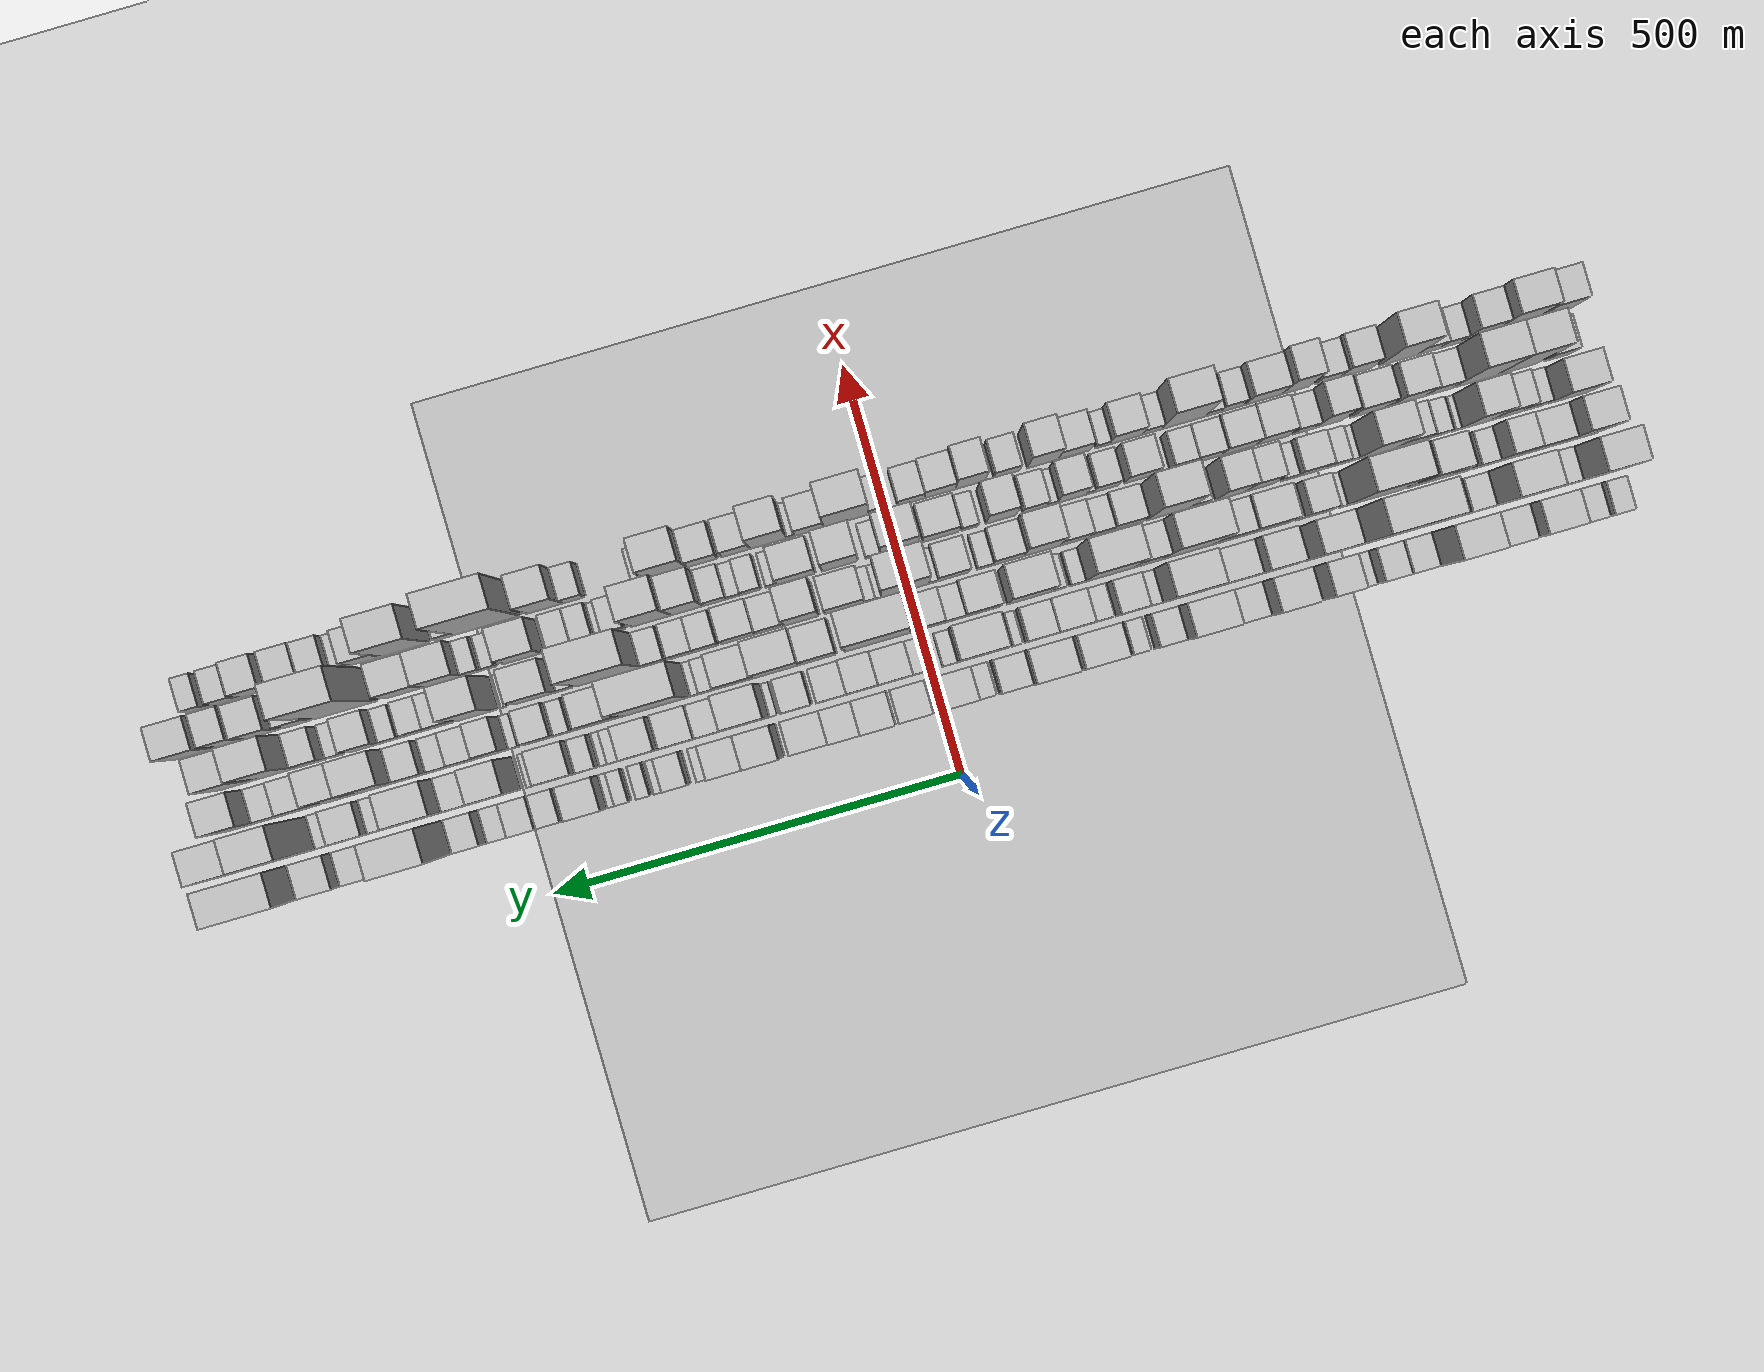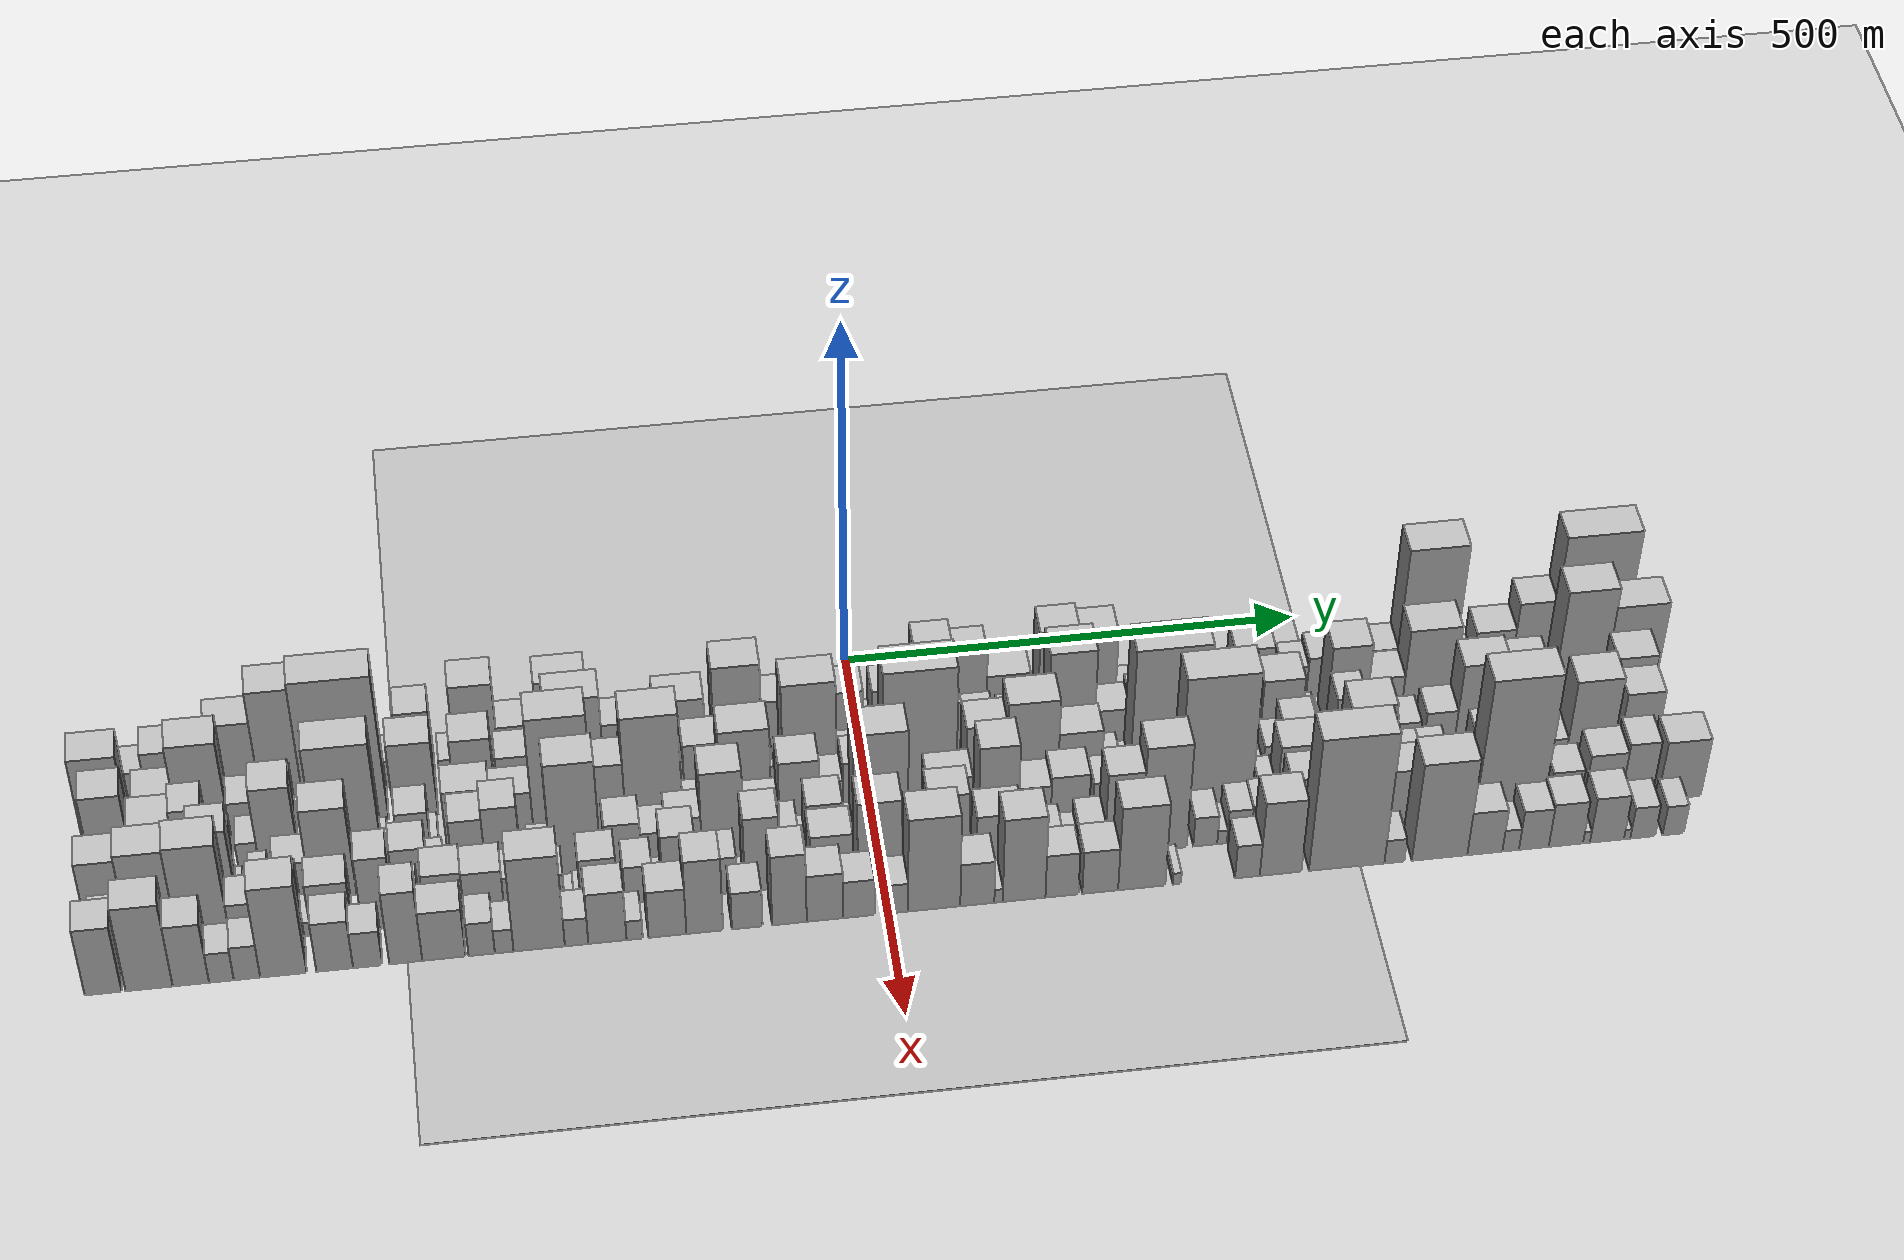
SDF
<?xml version="1.0" encoding="utf-8"?>

<sdf version="1.6">

   <world name="default">

      <gui fullscreen="0">

         <camera name="user_camera">

            <pose>-15 0 4.57585 0 0 0</pose>

            <view_controller>orbit</view_controller>

         </camera>

      </gui>

      <scene>

         <sky>

           <clouds>

             <speed>12</speed>

           </clouds>

         </sky>

         <ambient>0.4 0.4 0.4 1</ambient>

         <background>0.7 0.7 0.7 1</background>

         <shadows>1</shadows>

      </scene>

      <gravity>0 0 -9.8066</gravity>

      <magnetic_field>6e-06 2.3e-05 -4.2e-05</magnetic_field>

      <physics default="0" name="default_physics" type="ode">

         <ode>

            <solver>

               <type>quick</type>

               <iters>10</iters>

               <sor>1.0</sor>

               <use_dynamic_moi_rescaling>0</use_dynamic_moi_rescaling>

            </solver>

            <constraints>

               <cfm>0</cfm>

               <erp>0.2</erp>

               <contact_max_correcting_vel>100</contact_max_correcting_vel>

               <contact_surface_layer>0.001</contact_surface_layer>

            </constraints>

         </ode>

         <max_step_size>0.004</max_step_size>

         <real_time_factor>1</real_time_factor>

         <real_time_update_rate>250</real_time_update_rate>

      </physics>

      <light name="sun" type="directional">

         <cast_shadows>1</cast_shadows>

         <pose>0 0 10 0 0 0</pose>

         <diffuse>0.8 0.8 0.8 1</diffuse>

         <specular>0.2 0.2 0.2 1</specular>

         <attenuation>

            <range>1000</range>

            <constant>0.9</constant>

            <linear>0.01</linear>

            <quadratic>0.001</quadratic>

         </attenuation>

         <direction>-0.5 0.1 -0.9</direction>

      </light>

      <include>

         <name>ground_plane_1</name>

         <uri>model://HANNAS_ground_plane</uri>

         <pose>0 0 0  0 0 0</pose>

      </include>

      <include>

         <name>ground_plane_2</name>

         <uri>model://HANNAS_ground_plane</uri>

         <pose>100 0 0  0 0 0</pose>

      </include>

      <model name="building_1">

         <static>1</static>

         <pose frame="">100.0000 -817.6020 0 0.000000 0.000000 0.000000</pose>

         <link name="link">

            <pose frame="">0 0 24.00 0 0 0</pose>

            <collision name="collision">

               <geometry>

                  <box>

                     <size>40.0000 24.7960 48.0000</size>

                  </box>

               </geometry>

               <max_contacts>10</max_contacts>

               <surface>

                  <contact>

                     <ode/>

                  </contact>

                  <bounce/>

                  <friction>

                     <torsional>

                        <ode/>

                     </torsional>

                     <ode/>

                  </friction>

               </surface>

            </collision>

            <visual name="visual">

               <cast_shadows>0</cast_shadows>

               <geometry>

                  <box>

                     <size>40.0000 24.7960 48.0000</size>

                  </box>

               </geometry>

               <material>

                  <script>

                     <uri>model://HANNAS_wall/materials/scripts</uri>

                     <uri>model://HANNAS_wall/materials/textures</uri>

                     <name>vrc/HANNAS_wall</name>

                  </script>

               </material>

            </visual>

            <self_collide>0</self_collide>

            <enable_wind>0</enable_wind>

            <kinematic>0</kinematic>

         </link>

      </model>

      <model name="building_2">

         <static>1</static>

         <pose frame="">100.0000 -778.4976 0 0.000000 0.000000 0.000000</pose>

         <link name="link">

            <pose frame="">0 0 30.00 0 0 0</pose>

            <collision name="collision">

               <geometry>

                  <box>

                     <size>40.0000 33.4130 60.0000</size>

                  </box>

               </geometry>

               <max_contacts>10</max_contacts>

               <surface>

                  <contact>

                     <ode/>

                  </contact>

                  <bounce/>

                  <friction>

                     <torsional>

                        <ode/>

                     </torsional>

                     <ode/>

                  </friction>

               </surface>

            </collision>

            <visual name="visual">

               <cast_shadows>0</cast_shadows>

               <geometry>

                  <box>

                     <size>40.0000 33.4130 60.0000</size>

                  </box>

               </geometry>

               <material>

                  <script>

                     <uri>model://HANNAS_wall/materials/scripts</uri>

                     <uri>model://HANNAS_wall/materials/textures</uri>

                     <name>vrc/HANNAS_wall</name>

                  </script>

               </material>

            </visual>

            <self_collide>0</self_collide>

            <enable_wind>0</enable_wind>

            <kinematic>0</kinematic>

         </link>

      </model>

      <model name="building_3">

         <static>1</static>

         <pose frame="">100.0000 -737.9325 0 0.000000 0.000000 0.000000</pose>

         <link name="link">

            <pose frame="">0 0 43.50 0 0 0</pose>

            <collision name="collision">

               <geometry>

                  <box>

                     <size>40.0000 47.7172 87.0000</size>

                  </box>

               </geometry>

               <max_contacts>10</max_contacts>

               <surface>

                  <contact>

                     <ode/>

                  </contact>

                  <bounce/>

                  <friction>

                     <torsional>

                        <ode/>

                     </torsional>

                     <ode/>

                  </friction>

               </surface>

            </collision>

            <visual name="visual">

               <cast_shadows>0</cast_shadows>

               <geometry>

                  <box>

                     <size>40.0000 47.7172 87.0000</size>

                  </box>

               </geometry>

               <material>

                  <script>

                     <uri>model://HANNAS_wall/materials/scripts</uri>

                     <uri>model://HANNAS_wall/materials/textures</uri>

                     <name>vrc/HANNAS_wall</name>

                  </script>

               </material>

            </visual>

            <self_collide>0</self_collide>

            <enable_wind>0</enable_wind>

            <kinematic>0</kinematic>

         </link>

      </model>

      <model name="building_4">

         <static>1</static>

         <pose frame="">100.0000 -707.8373 0 0.000000 0.000000 0.000000</pose>

         <link name="link">

            <pose frame="">0 0 13.50 0 0 0</pose>

            <collision name="collision">

               <geometry>

                  <box>

                     <size>40.0000 12.4731 27.0000</size>

                  </box>

               </geometry>

               <max_contacts>10</max_contacts>

               <surface>

                  <contact>

                     <ode/>

                  </contact>

                  <bounce/>

                  <friction>

                     <torsional>

                        <ode/>

                     </torsional>

                     <ode/>

                  </friction>

               </surface>

            </collision>

            <visual name="visual">

               <cast_shadows>0</cast_shadows>

               <geometry>

                  <box>

                     <size>40.0000 12.4731 27.0000</size>

                  </box>

               </geometry>

               <material>

                  <script>

                     <uri>model://HANNAS_wall/materials/scripts</uri>

                     <uri>model://HANNAS_wall/materials/textures</uri>

                     <name>vrc/HANNAS_wall</name>

                  </script>

               </material>

            </visual>

            <self_collide>0</self_collide>

            <enable_wind>0</enable_wind>

            <kinematic>0</kinematic>

         </link>

      </model>

      <model name="building_5">

         <static>1</static>

         <pose frame="">100.0000 -667.6534 0 0.000000 0.000000 0.000000</pose>

         <link name="link">

            <pose frame="">0 0 60.00 0 0 0</pose>

            <collision name="collision">

               <geometry>

                  <box>

                     <size>40.0000 47.8948 120.0000</size>

                  </box>

               </geometry>

               <max_contacts>10</max_contacts>

               <surface>

                  <contact>

                     <ode/>

                  </contact>

                  <bounce/>

                  <friction>

                     <torsional>

                        <ode/>

                     </torsional>

                     <ode/>

                  </friction>

               </surface>

            </collision>

            <visual name="visual">

               <cast_shadows>0</cast_shadows>

               <geometry>

                  <box>

                     <size>40.0000 47.8948 120.0000</size>

                  </box>

               </geometry>

               <material>

                  <script>

                     <uri>model://HANNAS_wall/materials/scripts</uri>

                     <uri>model://HANNAS_wall/materials/textures</uri>

                     <name>vrc/HANNAS_wall</name>

                  </script>

               </material>

            </visual>

            <self_collide>0</self_collide>

            <enable_wind>0</enable_wind>

            <kinematic>0</kinematic>

         </link>

      </model>

      <model name="building_6">

         <static>1</static>

         <pose frame="">100.0000 -617.7483 0 0.000000 0.000000 0.000000</pose>

         <link name="link">

            <pose frame="">0 0 82.50 0 0 0</pose>

            <collision name="collision">

               <geometry>

                  <box>

                     <size>40.0000 51.9155 165.0000</size>

                  </box>

               </geometry>

               <max_contacts>10</max_contacts>

               <surface>

                  <contact>

                     <ode/>

                  </contact>

                  <bounce/>

                  <friction>

                     <torsional>

                        <ode/>

                     </torsional>

                     <ode/>

                  </friction>

               </surface>

            </collision>

            <visual name="visual">

               <cast_shadows>0</cast_shadows>

               <geometry>

                  <box>

                     <size>40.0000 51.9155 165.0000</size>

                  </box>

               </geometry>

               <material>

                  <script>

                     <uri>model://HANNAS_wall/materials/scripts</uri>

                     <uri>model://HANNAS_wall/materials/textures</uri>

                     <name>vrc/HANNAS_wall</name>

                  </script>

               </material>

            </visual>

            <self_collide>0</self_collide>

            <enable_wind>0</enable_wind>

            <kinematic>0</kinematic>

         </link>

      </model>

      <model name="building_7">

         <static>1</static>

         <pose frame="">100.0000 -575.8637 0 0.000000 0.000000 0.000000</pose>

         <link name="link">

            <pose frame="">0 0 31.50 0 0 0</pose>

            <collision name="collision">

               <geometry>

                  <box>

                     <size>40.0000 31.8537 63.0000</size>

                  </box>

               </geometry>

               <max_contacts>10</max_contacts>

               <surface>

                  <contact>

                     <ode/>

                  </contact>

                  <bounce/>

                  <friction>

                     <torsional>

                        <ode/>

                     </torsional>

                     <ode/>

                  </friction>

               </surface>

            </collision>

            <visual name="visual">

               <cast_shadows>0</cast_shadows>

               <geometry>

                  <box>

                     <size>40.0000 31.8537 63.0000</size>

                  </box>

               </geometry>

               <material>

                  <script>

                     <uri>model://HANNAS_wall/materials/scripts</uri>

                     <uri>model://HANNAS_wall/materials/textures</uri>

                     <name>vrc/HANNAS_wall</name>

                  </script>

               </material>

            </visual>

            <self_collide>0</self_collide>

            <enable_wind>0</enable_wind>

            <kinematic>0</kinematic>

         </link>

      </model>

      <model name="building_8">

         <static>1</static>

         <pose frame="">100.0000 -543.9341 0 0.000000 0.000000 0.000000</pose>

         <link name="link">

            <pose frame="">0 0 28.50 0 0 0</pose>

            <collision name="collision">

               <geometry>

                  <box>

                     <size>40.0000 32.0055 57.0000</size>

                  </box>

               </geometry>

               <max_contacts>10</max_contacts>

               <surface>

                  <contact>

                     <ode/>

                  </contact>

                  <bounce/>

                  <friction>

                     <torsional>

                        <ode/>

                     </torsional>

                     <ode/>

                  </friction>

               </surface>

            </collision>

            <visual name="visual">

               <cast_shadows>0</cast_shadows>

               <geometry>

                  <box>

                     <size>40.0000 32.0055 57.0000</size>

                  </box>

               </geometry>

               <material>

                  <script>

                     <uri>model://HANNAS_wall/materials/scripts</uri>

                     <uri>model://HANNAS_wall/materials/textures</uri>

                     <name>vrc/HANNAS_wall</name>

                  </script>

               </material>

            </visual>

            <self_collide>0</self_collide>

            <enable_wind>0</enable_wind>

            <kinematic>0</kinematic>

         </link>

      </model>

      <model name="building_9">

         <static>1</static>

         <pose frame="">100.0000 -511.4960 0 0.000000 0.000000 0.000000</pose>

         <link name="link">

            <pose frame="">0 0 19.50 0 0 0</pose>

            <collision name="collision">

               <geometry>

                  <box>

                     <size>40.0000 20.8707 39.0000</size>

                  </box>

               </geometry>

               <max_contacts>10</max_contacts>

               <surface>

                  <contact>

                     <ode/>

                  </contact>

                  <bounce/>

                  <friction>

                     <torsional>

                        <ode/>

                     </torsional>

                     <ode/>

                  </friction>

               </surface>

            </collision>

            <visual name="visual">

               <cast_shadows>0</cast_shadows>

               <geometry>

                  <box>

                     <size>40.0000 20.8707 39.0000</size>

                  </box>

               </geometry>

               <material>

                  <script>

                     <uri>model://HANNAS_wall/materials/scripts</uri>

                     <uri>model://HANNAS_wall/materials/textures</uri>

                     <name>vrc/HANNAS_wall</name>

                  </script>

               </material>

            </visual>

            <self_collide>0</self_collide>

            <enable_wind>0</enable_wind>

            <kinematic>0</kinematic>

         </link>

      </model>

      <model name="building_10">

         <static>1</static>

         <pose frame="">100.0000 -475.5897 0 0.000000 0.000000 0.000000</pose>

         <link name="link">

            <pose frame="">0 0 55.50 0 0 0</pose>

            <collision name="collision">

               <geometry>

                  <box>

                     <size>40.0000 36.9420 111.0000</size>

                  </box>

               </geometry>

               <max_contacts>10</max_contacts>

               <surface>

                  <contact>

                     <ode/>

                  </contact>

                  <bounce/>

                  <friction>

                     <torsional>

                        <ode/>

                     </torsional>

                     <ode/>

                  </friction>

               </surface>

            </collision>

            <visual name="visual">

               <cast_shadows>0</cast_shadows>

               <geometry>

                  <box>

                     <size>40.0000 36.9420 111.0000</size>

                  </box>

               </geometry>

               <material>

                  <script>

                     <uri>model://HANNAS_wall/materials/scripts</uri>

                     <uri>model://HANNAS_wall/materials/textures</uri>

                     <name>vrc/HANNAS_wall</name>

                  </script>

               </material>

            </visual>

            <self_collide>0</self_collide>

            <enable_wind>0</enable_wind>

            <kinematic>0</kinematic>

         </link>

      </model>

      <model name="building_11">

         <static>1</static>

         <pose frame="">100.0000 -443.1418 0 0.000000 0.000000 0.000000</pose>

         <link name="link">

            <pose frame="">0 0 16.50 0 0 0</pose>

            <collision name="collision">

               <geometry>

                  <box>

                     <size>40.0000 17.9537 33.0000</size>

                  </box>

               </geometry>

               <max_contacts>10</max_contacts>

               <surface>

                  <contact>

                     <ode/>

                  </contact>

                  <bounce/>

                  <friction>

                     <torsional>

                        <ode/>

                     </torsional>

                     <ode/>

                  </friction>

               </surface>

            </collision>

            <visual name="visual">

               <cast_shadows>0</cast_shadows>

               <geometry>

                  <box>

                     <size>40.0000 17.9537 33.0000</size>

                  </box>

               </geometry>

               <material>

                  <script>

                     <uri>model://HANNAS_wall/materials/scripts</uri>

                     <uri>model://HANNAS_wall/materials/textures</uri>

                     <name>vrc/HANNAS_wall</name>

                  </script>

               </material>

            </visual>

            <self_collide>0</self_collide>

            <enable_wind>0</enable_wind>

            <kinematic>0</kinematic>

         </link>

      </model>

      <model name="building_12">

         <static>1</static>

         <pose frame="">100.0000 -411.0551 0 0.000000 0.000000 0.000000</pose>

         <link name="link">

            <pose frame="">0 0 72.00 0 0 0</pose>

            <collision name="collision">

               <geometry>

                  <box>

                     <size>40.0000 46.2196 144.0000</size>

                  </box>

               </geometry>

               <max_contacts>10</max_contacts>

               <surface>

                  <contact>

                     <ode/>

                  </contact>

                  <bounce/>

                  <friction>

                     <torsional>

                        <ode/>

                     </torsional>

                     <ode/>

                  </friction>

               </surface>

            </collision>

            <visual name="visual">

               <cast_shadows>0</cast_shadows>

               <geometry>

                  <box>

                     <size>40.0000 46.2196 144.0000</size>

                  </box>

               </geometry>

               <material>

                  <script>

                     <uri>model://HANNAS_wall/materials/scripts</uri>

                     <uri>model://HANNAS_wall/materials/textures</uri>

                     <name>vrc/HANNAS_wall</name>

                  </script>

               </material>

            </visual>

            <self_collide>0</self_collide>

            <enable_wind>0</enable_wind>

            <kinematic>0</kinematic>

         </link>

      </model>

      <model name="building_13">

         <static>1</static>

         <pose frame="">100.0000 -366.1930 0 0.000000 0.000000 0.000000</pose>

         <link name="link">

            <pose frame="">0 0 37.50 0 0 0</pose>

            <collision name="collision">

               <geometry>

                  <box>

                     <size>40.0000 43.5047 75.0000</size>

                  </box>

               </geometry>

               <max_contacts>10</max_contacts>

               <surface>

                  <contact>

                     <ode/>

                  </contact>

                  <bounce/>

                  <friction>

                     <torsional>

                        <ode/>

                     </torsional>

                     <ode/>

                  </friction>

               </surface>

            </collision>

            <visual name="visual">

               <cast_shadows>0</cast_shadows>

               <geometry>

                  <box>

                     <size>40.0000 43.5047 75.0000</size>

                  </box>

               </geometry>

               <material>

                  <script>

                     <uri>model://HANNAS_wall/materials/scripts</uri>

                     <uri>model://HANNAS_wall/materials/textures</uri>

                     <name>vrc/HANNAS_wall</name>

                  </script>

               </material>

            </visual>

            <self_collide>0</self_collide>

            <enable_wind>0</enable_wind>

            <kinematic>0</kinematic>

         </link>

      </model>

      <model name="building_14">

         <static>1</static>

         <pose frame="">100.0000 -317.1864 0 0.000000 0.000000 0.000000</pose>

         <link name="link">

            <pose frame="">0 0 69.00 0 0 0</pose>

            <collision name="collision">

               <geometry>

                  <box>

                     <size>40.0000 54.5084 138.0000</size>

                  </box>

               </geometry>

               <max_contacts>10</max_contacts>

               <surface>

                  <contact>

                     <ode/>

                  </contact>

                  <bounce/>

                  <friction>

                     <torsional>

                        <ode/>

                     </torsional>

                     <ode/>

                  </friction>

               </surface>

            </collision>

            <visual name="visual">

               <cast_shadows>0</cast_shadows>

               <geometry>

                  <box>

                     <size>40.0000 54.5084 138.0000</size>

                  </box>

               </geometry>

               <material>

                  <script>

                     <uri>model://HANNAS_wall/materials/scripts</uri>

                     <uri>model://HANNAS_wall/materials/textures</uri>

                     <name>vrc/HANNAS_wall</name>

                  </script>

               </material>

            </visual>

            <self_collide>0</self_collide>

            <enable_wind>0</enable_wind>

            <kinematic>0</kinematic>

         </link>

      </model>

      <model name="building_15">

         <static>1</static>

         <pose frame="">100.0000 -273.7449 0 0.000000 0.000000 0.000000</pose>

         <link name="link">

            <pose frame="">0 0 31.50 0 0 0</pose>

            <collision name="collision">

               <geometry>

                  <box>

                     <size>40.0000 32.3744 63.0000</size>

                  </box>

               </geometry>

               <max_contacts>10</max_contacts>

               <surface>

                  <contact>

                     <ode/>

                  </contact>

                  <bounce/>

                  <friction>

                     <torsional>

                        <ode/>

                     </torsional>

                     <ode/>

                  </friction>

               </surface>

            </collision>

            <visual name="visual">

               <cast_shadows>0</cast_shadows>

               <geometry>

                  <box>

                     <size>40.0000 32.3744 63.0000</size>

                  </box>

               </geometry>

               <material>

                  <script>

                     <uri>model://HANNAS_wall/materials/scripts</uri>

                     <uri>model://HANNAS_wall/materials/textures</uri>

                     <name>vrc/HANNAS_wall</name>

                  </script>

               </material>

            </visual>

            <self_collide>0</self_collide>

            <enable_wind>0</enable_wind>

            <kinematic>0</kinematic>

         </link>

      </model>

      <model name="building_16">

         <static>1</static>

         <pose frame="">100.0000 -239.2086 0 0.000000 0.000000 0.000000</pose>

         <link name="link">

            <pose frame="">0 0 18.00 0 0 0</pose>

            <collision name="collision">

               <geometry>

                  <box>

                     <size>40.0000 20.6983 36.0000</size>

                  </box>

               </geometry>

               <max_contacts>10</max_contacts>

               <surface>

                  <contact>

                     <ode/>

                  </contact>

                  <bounce/>

                  <friction>

                     <torsional>

                        <ode/>

                     </torsional>

                     <ode/>

                  </friction>

               </surface>

            </collision>

            <visual name="visual">

               <cast_shadows>0</cast_shadows>

               <geometry>

                  <box>

                     <size>40.0000 20.6983 36.0000</size>

                  </box>

               </geometry>

               <material>

                  <script>

                     <uri>model://HANNAS_wall/materials/scripts</uri>

                     <uri>model://HANNAS_wall/materials/textures</uri>

                     <name>vrc/HANNAS_wall</name>

                  </script>

               </material>

            </visual>

            <self_collide>0</self_collide>

            <enable_wind>0</enable_wind>

            <kinematic>0</kinematic>

         </link>

      </model>

      <model name="building_17">

         <static>1</static>

         <pose frame="">100.0000 -193.1272 0 0.000000 0.000000 0.000000</pose>

         <link name="link">

            <pose frame="">0 0 45.00 0 0 0</pose>

            <collision name="collision">

               <geometry>

                  <box>

                     <size>40.0000 53.4645 90.0000</size>

                  </box>

               </geometry>

               <max_contacts>10</max_contacts>

               <surface>

                  <contact>

                     <ode/>

                  </contact>

                  <bounce/>

                  <friction>

                     <torsional>

                        <ode/>

                     </torsional>

                     <ode/>

                  </friction>

               </surface>

            </collision>

            <visual name="visual">

               <cast_shadows>0</cast_shadows>

               <geometry>

                  <box>

                     <size>40.0000 53.4645 90.0000</size>

                  </box>

               </geometry>

               <material>

                  <script>

                     <uri>model://HANNAS_wall/materials/scripts</uri>

                     <uri>model://HANNAS_wall/materials/textures</uri>

                     <name>vrc/HANNAS_wall</name>

                  </script>

               </material>

            </visual>

            <self_collide>0</self_collide>

            <enable_wind>0</enable_wind>

            <kinematic>0</kinematic>

         </link>

      </model>

      <model name="building_18">

         <static>1</static>

         <pose frame="">100.0000 -131.4494 0 0.000000 0.000000 0.000000</pose>

         <link name="link">

            <pose frame="">0 0 67.50 0 0 0</pose>

            <collision name="collision">

               <geometry>

                  <box>

                     <size>40.0000 51.8910 135.0000</size>

                  </box>

               </geometry>

               <max_contacts>10</max_contacts>

               <surface>

                  <contact>

                     <ode/>

                  </contact>

                  <bounce/>

                  <friction>

                     <torsional>

                        <ode/>

                     </torsional>

                     <ode/>

                  </friction>

               </surface>

            </collision>

            <visual name="visual">

               <cast_shadows>0</cast_shadows>

               <geometry>

                  <box>

                     <size>40.0000 51.8910 135.0000</size>

                  </box>

               </geometry>

               <material>

                  <script>

                     <uri>model://HANNAS_wall/materials/scripts</uri>

                     <uri>model://HANNAS_wall/materials/textures</uri>

                     <name>vrc/HANNAS_wall</name>

                  </script>

               </material>

            </visual>

            <self_collide>0</self_collide>

            <enable_wind>0</enable_wind>

            <kinematic>0</kinematic>

         </link>

      </model>

      <model name="building_19">

         <static>1</static>

         <pose frame="">100.0000 -86.6380 0 0.000000 0.000000 0.000000</pose>

         <link name="link">

            <pose frame="">0 0 37.50 0 0 0</pose>

            <collision name="collision">

               <geometry>

                  <box>

                     <size>40.0000 37.7317 75.0000</size>

                  </box>

               </geometry>

               <max_contacts>10</max_contacts>

               <surface>

                  <contact>

                     <ode/>

                  </contact>

                  <bounce/>

                  <friction>

                     <torsional>

                        <ode/>

                     </torsional>

                     <ode/>

                  </friction>

               </surface>

            </collision>

            <visual name="visual">

               <cast_shadows>0</cast_shadows>

               <geometry>

                  <box>

                     <size>40.0000 37.7317 75.0000</size>

                  </box>

               </geometry>

               <material>

                  <script>

                     <uri>model://HANNAS_wall/materials/scripts</uri>

                     <uri>model://HANNAS_wall/materials/textures</uri>

                     <name>vrc/HANNAS_wall</name>

                  </script>

               </material>

            </visual>

            <self_collide>0</self_collide>

            <enable_wind>0</enable_wind>

            <kinematic>0</kinematic>

         </link>

      </model>

      <model name="building_20">

         <static>1</static>

         <pose frame="">100.0000 -52.0958 0 0.000000 0.000000 0.000000</pose>

         <link name="link">

            <pose frame="">0 0 21.00 0 0 0</pose>

            <collision name="collision">

               <geometry>

                  <box>

                     <size>40.0000 21.3527 42.0000</size>

                  </box>

               </geometry>

               <max_contacts>10</max_contacts>

               <surface>

                  <contact>

                     <ode/>

                  </contact>

                  <bounce/>

                  <friction>

                     <torsional>

                        <ode/>

                     </torsional>

                     <ode/>

                  </friction>

               </surface>

            </collision>

            <visual name="visual">

               <cast_shadows>0</cast_shadows>

               <geometry>

                  <box>

                     <size>40.0000 21.3527 42.0000</size>

                  </box>

               </geometry>

               <material>

                  <script>

                     <uri>model://HANNAS_wall/materials/scripts</uri>

                     <uri>model://HANNAS_wall/materials/textures</uri>

                     <name>vrc/HANNAS_wall</name>

                  </script>

               </material>

            </visual>

            <self_collide>0</self_collide>

            <enable_wind>0</enable_wind>

            <kinematic>0</kinematic>

         </link>

      </model>

      <model name="building_21">

         <static>1</static>

         <pose frame="">100.0000 -18.5230 0 0.000000 0.000000 0.000000</pose>

         <link name="link">

            <pose frame="">0 0 39.00 0 0 0</pose>

            <collision name="collision">

               <geometry>

                  <box>

                     <size>40.0000 45.7930 78.0000</size>

                  </box>

               </geometry>

               <max_contacts>10</max_contacts>

               <surface>

                  <contact>

                     <ode/>

                  </contact>

                  <bounce/>

                  <friction>

                     <torsional>

                        <ode/>

                     </torsional>

                     <ode/>

                  </friction>

               </surface>

            </collision>

            <visual name="visual">

               <cast_shadows>0</cast_shadows>

               <geometry>

                  <box>

                     <size>40.0000 45.7930 78.0000</size>

                  </box>

               </geometry>

               <material>

                  <script>

                     <uri>model://HANNAS_wall/materials/scripts</uri>

                     <uri>model://HANNAS_wall/materials/textures</uri>

                     <name>vrc/HANNAS_wall</name>

                  </script>

               </material>

            </visual>

            <self_collide>0</self_collide>

            <enable_wind>0</enable_wind>

            <kinematic>0</kinematic>

         </link>

      </model>

      <model name="building_22">

         <static>1</static>

         <pose frame="">100.0000 9.1661 0 0.000000 0.000000 0.000000</pose>

         <link name="link">

            <pose frame="">0 0 10.50 0 0 0</pose>

            <collision name="collision">

               <geometry>

                  <box>

                     <size>40.0000 9.5852 21.0000</size>

                  </box>

               </geometry>

               <max_contacts>10</max_contacts>

               <surface>

                  <contact>

                     <ode/>

                  </contact>

                  <bounce/>

                  <friction>

                     <torsional>

                        <ode/>

                     </torsional>

                     <ode/>

                  </friction>

               </surface>

            </collision>

            <visual name="visual">

               <cast_shadows>0</cast_shadows>

               <geometry>

                  <box>

                     <size>40.0000 9.5852 21.0000</size>

                  </box>

               </geometry>

               <material>

                  <script>

                     <uri>model://HANNAS_wall/materials/scripts</uri>

                     <uri>model://HANNAS_wall/materials/textures</uri>

                     <name>vrc/HANNAS_wall</name>

                  </script>

               </material>

            </visual>

            <self_collide>0</self_collide>

            <enable_wind>0</enable_wind>

            <kinematic>0</kinematic>

         </link>

      </model>

      <model name="building_23">

         <static>1</static>

         <pose frame="">100.0000 34.5753 0 0.000000 0.000000 0.000000</pose>

         <link name="link">

            <pose frame="">0 0 37.50 0 0 0</pose>

            <collision name="collision">

               <geometry>

                  <box>

                     <size>40.0000 41.2334 75.0000</size>

                  </box>

               </geometry>

               <max_contacts>10</max_contacts>

               <surface>

                  <contact>

                     <ode/>

                  </contact>

                  <bounce/>

                  <friction>

                     <torsional>

                        <ode/>

                     </torsional>

                     <ode/>

                  </friction>

               </surface>

            </collision>

            <visual name="visual">

               <cast_shadows>0</cast_shadows>

               <geometry>

                  <box>

                     <size>40.0000 41.2334 75.0000</size>

                  </box>

               </geometry>

               <material>

                  <script>

                     <uri>model://HANNAS_wall/materials/scripts</uri>

                     <uri>model://HANNAS_wall/materials/textures</uri>

                     <name>vrc/HANNAS_wall</name>

                  </script>

               </material>

            </visual>

            <self_collide>0</self_collide>

            <enable_wind>0</enable_wind>

            <kinematic>0</kinematic>

         </link>

      </model>

      <model name="building_24">

         <static>1</static>

         <pose frame="">100.0000 79.7952 0 0.000000 0.000000 0.000000</pose>

         <link name="link">

            <pose frame="">0 0 67.50 0 0 0</pose>

            <collision name="collision">

               <geometry>

                  <box>

                     <size>40.0000 41.2063 135.0000</size>

                  </box>

               </geometry>

               <max_contacts>10</max_contacts>

               <surface>

                  <contact>

                     <ode/>

                  </contact>

                  <bounce/>

                  <friction>

                     <torsional>

                        <ode/>

                     </torsional>

                     <ode/>

                  </friction>

               </surface>

            </collision>

            <visual name="visual">

               <cast_shadows>0</cast_shadows>

               <geometry>

                  <box>

                     <size>40.0000 41.2063 135.0000</size>

                  </box>

               </geometry>

               <material>

                  <script>

                     <uri>model://HANNAS_wall/materials/scripts</uri>

                     <uri>model://HANNAS_wall/materials/textures</uri>

                     <name>vrc/HANNAS_wall</name>

                  </script>

               </material>

            </visual>

            <self_collide>0</self_collide>

            <enable_wind>0</enable_wind>

            <kinematic>0</kinematic>

         </link>

      </model>

      <model name="building_25">

         <static>1</static>

         <pose frame="">100.0000 119.3548 0 0.000000 0.000000 0.000000</pose>

         <link name="link">

            <pose frame="">0 0 60.00 0 0 0</pose>

            <collision name="collision">

               <geometry>

                  <box>

                     <size>40.0000 37.9129 120.0000</size>

                  </box>

               </geometry>

               <max_contacts>10</max_contacts>

               <surface>

                  <contact>

                     <ode/>

                  </contact>

                  <bounce/>

                  <friction>

                     <torsional>

                        <ode/>

                     </torsional>

                     <ode/>

                  </friction>

               </surface>

            </collision>

            <visual name="visual">

               <cast_shadows>0</cast_shadows>

               <geometry>

                  <box>

                     <size>40.0000 37.9129 120.0000</size>

                  </box>

               </geometry>

               <material>

                  <script>

                     <uri>model://HANNAS_wall/materials/scripts</uri>

                     <uri>model://HANNAS_wall/materials/textures</uri>

                     <name>vrc/HANNAS_wall</name>

                  </script>

               </material>

            </visual>

            <self_collide>0</self_collide>

            <enable_wind>0</enable_wind>

            <kinematic>0</kinematic>

         </link>

      </model>

      <model name="building_26">

         <static>1</static>

         <pose frame="">100.0000 161.9908 0 0.000000 0.000000 0.000000</pose>

         <link name="link">

            <pose frame="">0 0 40.50 0 0 0</pose>

            <collision name="collision">

               <geometry>

                  <box>

                     <size>40.0000 47.3593 81.0000</size>

                  </box>

               </geometry>

               <max_contacts>10</max_contacts>

               <surface>

                  <contact>

                     <ode/>

                  </contact>

                  <bounce/>

                  <friction>

                     <torsional>

                        <ode/>

                     </torsional>

                     <ode/>

                  </friction>

               </surface>

            </collision>

            <visual name="visual">

               <cast_shadows>0</cast_shadows>

               <geometry>

                  <box>

                     <size>40.0000 47.3593 81.0000</size>

                  </box>

               </geometry>

               <material>

                  <script>

                     <uri>model://HANNAS_wall/materials/scripts</uri>

                     <uri>model://HANNAS_wall/materials/textures</uri>

                     <name>vrc/HANNAS_wall</name>

                  </script>

               </material>

            </visual>

            <self_collide>0</self_collide>

            <enable_wind>0</enable_wind>

            <kinematic>0</kinematic>

         </link>

      </model>

      <model name="building_27">

         <static>1</static>

         <pose frame="">100.0000 216.1029 0 0.000000 0.000000 0.000000</pose>

         <link name="link">

            <pose frame="">0 0 70.50 0 0 0</pose>

            <collision name="collision">

               <geometry>

                  <box>

                     <size>40.0000 42.8648 141.0000</size>

                  </box>

               </geometry>

               <max_contacts>10</max_contacts>

               <surface>

                  <contact>

                     <ode/>

                  </contact>

                  <bounce/>

                  <friction>

                     <torsional>

                        <ode/>

                     </torsional>

                     <ode/>

                  </friction>

               </surface>

            </collision>

            <visual name="visual">

               <cast_shadows>0</cast_shadows>

               <geometry>

                  <box>

                     <size>40.0000 42.8648 141.0000</size>

                  </box>

               </geometry>

               <material>

                  <script>

                     <uri>model://HANNAS_wall/materials/scripts</uri>

                     <uri>model://HANNAS_wall/materials/textures</uri>

                     <name>vrc/HANNAS_wall</name>

                  </script>

               </material>

            </visual>

            <self_collide>0</self_collide>

            <enable_wind>0</enable_wind>

            <kinematic>0</kinematic>

         </link>

      </model>

      <model name="building_28">

         <static>1</static>

         <pose frame="">100.0000 258.3487 0 0.000000 0.000000 0.000000</pose>

         <link name="link">

            <pose frame="">0 0 66.00 0 0 0</pose>

            <collision name="collision">

               <geometry>

                  <box>

                     <size>40.0000 41.6270 132.0000</size>

                  </box>

               </geometry>

               <max_contacts>10</max_contacts>

               <surface>

                  <contact>

                     <ode/>

                  </contact>

                  <bounce/>

                  <friction>

                     <torsional>

                        <ode/>

                     </torsional>

                     <ode/>

                  </friction>

               </surface>

            </collision>

            <visual name="visual">

               <cast_shadows>0</cast_shadows>

               <geometry>

                  <box>

                     <size>40.0000 41.6270 132.0000</size>

                  </box>

               </geometry>

               <material>

                  <script>

                     <uri>model://HANNAS_wall/materials/scripts</uri>

                     <uri>model://HANNAS_wall/materials/textures</uri>

                     <name>vrc/HANNAS_wall</name>

                  </script>

               </material>

            </visual>

            <self_collide>0</self_collide>

            <enable_wind>0</enable_wind>

            <kinematic>0</kinematic>

         </link>

      </model>

      <model name="building_29">

         <static>1</static>

         <pose frame="">100.0000 289.1495 0 0.000000 0.000000 0.000000</pose>

         <link name="link">

            <pose frame="">0 0 18.00 0 0 0</pose>

            <collision name="collision">

               <geometry>

                  <box>

                     <size>40.0000 19.9747 36.0000</size>

                  </box>

               </geometry>

               <max_contacts>10</max_contacts>

               <surface>

                  <contact>

                     <ode/>

                  </contact>

                  <bounce/>

                  <friction>

                     <torsional>

                        <ode/>

                     </torsional>

                     <ode/>

                  </friction>

               </surface>

            </collision>

            <visual name="visual">

               <cast_shadows>0</cast_shadows>

               <geometry>

                  <box>

                     <size>40.0000 19.9747 36.0000</size>

                  </box>

               </geometry>

               <material>

                  <script>

                     <uri>model://HANNAS_wall/materials/scripts</uri>

                     <uri>model://HANNAS_wall/materials/textures</uri>

                     <name>vrc/HANNAS_wall</name>

                  </script>

               </material>

            </visual>

            <self_collide>0</self_collide>

            <enable_wind>0</enable_wind>

            <kinematic>0</kinematic>

         </link>

      </model>

      <model name="building_30">

         <static>1</static>

         <pose frame="">100.0000 324.1866 0 0.000000 0.000000 0.000000</pose>

         <link name="link">

            <pose frame="">0 0 27.00 0 0 0</pose>

            <collision name="collision">

               <geometry>

                  <box>

                     <size>40.0000 30.0996 54.0000</size>

                  </box>

               </geometry>

               <max_contacts>10</max_contacts>

               <surface>

                  <contact>

                     <ode/>

                  </contact>

                  <bounce/>

                  <friction>

                     <torsional>

                        <ode/>

                     </torsional>

                     <ode/>

                  </friction>

               </surface>

            </collision>

            <visual name="visual">

               <cast_shadows>0</cast_shadows>

               <geometry>

                  <box>

                     <size>40.0000 30.0996 54.0000</size>

                  </box>

               </geometry>

               <material>

                  <script>

                     <uri>model://HANNAS_wall/materials/scripts</uri>

                     <uri>model://HANNAS_wall/materials/textures</uri>

                     <name>vrc/HANNAS_wall</name>

                  </script>

               </material>

            </visual>

            <self_collide>0</self_collide>

            <enable_wind>0</enable_wind>

            <kinematic>0</kinematic>

         </link>

      </model>

      <model name="building_31">

         <static>1</static>

         <pose frame="">100.0000 345.3489 0 0.000000 0.000000 0.000000</pose>

         <link name="link">

            <pose frame="">0 0 13.50 0 0 0</pose>

            <collision name="collision">

               <geometry>

                  <box>

                     <size>40.0000 12.2250 27.0000</size>

                  </box>

               </geometry>

               <max_contacts>10</max_contacts>

               <surface>

                  <contact>

                     <ode/>

                  </contact>

                  <bounce/>

                  <friction>

                     <torsional>

                        <ode/>

                     </torsional>

                     <ode/>

                  </friction>

               </surface>

            </collision>

            <visual name="visual">

               <cast_shadows>0</cast_shadows>

               <geometry>

                  <box>

                     <size>40.0000 12.2250 27.0000</size>

                  </box>

               </geometry>

               <material>

                  <script>

                     <uri>model://HANNAS_wall/materials/scripts</uri>

                     <uri>model://HANNAS_wall/materials/textures</uri>

                     <name>vrc/HANNAS_wall</name>

                  </script>

               </material>

            </visual>

            <self_collide>0</self_collide>

            <enable_wind>0</enable_wind>

            <kinematic>0</kinematic>

         </link>

      </model>

      <model name="building_32">

         <static>1</static>

         <pose frame="">100.0000 364.6628 0 0.000000 0.000000 0.000000</pose>

         <link name="link">

            <pose frame="">0 0 15.00 0 0 0</pose>

            <collision name="collision">

               <geometry>

                  <box>

                     <size>40.0000 16.4029 30.0000</size>

                  </box>

               </geometry>

               <max_contacts>10</max_contacts>

               <surface>

                  <contact>

                     <ode/>

                  </contact>

                  <bounce/>

                  <friction>

                     <torsional>

                        <ode/>

                     </torsional>

                     <ode/>

                  </friction>

               </surface>

            </collision>

            <visual name="visual">

               <cast_shadows>0</cast_shadows>

               <geometry>

                  <box>

                     <size>40.0000 16.4029 30.0000</size>

                  </box>

               </geometry>

               <material>

                  <script>

                     <uri>model://HANNAS_wall/materials/scripts</uri>

                     <uri>model://HANNAS_wall/materials/textures</uri>

                     <name>vrc/HANNAS_wall</name>

                  </script>

               </material>

            </visual>

            <self_collide>0</self_collide>

            <enable_wind>0</enable_wind>

            <kinematic>0</kinematic>

         </link>

      </model>

      <model name="building_33">

         <static>1</static>

         <pose frame="">100.0000 390.3168 0 0.000000 0.000000 0.000000</pose>

         <link name="link">

            <pose frame="">0 0 16.50 0 0 0</pose>

            <collision name="collision">

               <geometry>

                  <box>

                     <size>40.0000 16.9051 33.0000</size>

                  </box>

               </geometry>

               <max_contacts>10</max_contacts>

               <surface>

                  <contact>

                     <ode/>

                  </contact>

                  <bounce/>

                  <friction>

                     <torsional>

                        <ode/>

                     </torsional>

                     <ode/>

                  </friction>

               </surface>

            </collision>

            <visual name="visual">

               <cast_shadows>0</cast_shadows>

               <geometry>

                  <box>

                     <size>40.0000 16.9051 33.0000</size>

                  </box>

               </geometry>

               <material>

                  <script>

                     <uri>model://HANNAS_wall/materials/scripts</uri>

                     <uri>model://HANNAS_wall/materials/textures</uri>

                     <name>vrc/HANNAS_wall</name>

                  </script>

               </material>

            </visual>

            <self_collide>0</self_collide>

            <enable_wind>0</enable_wind>

            <kinematic>0</kinematic>

         </link>

      </model>

      <model name="building_34">

         <static>1</static>

         <pose frame="">100.0000 403.7031 0 0.000000 0.000000 0.000000</pose>

         <link name="link">

            <pose frame="">0 0 10.50 0 0 0</pose>

            <collision name="collision">

               <geometry>

                  <box>

                     <size>40.0000 9.8676 21.0000</size>

                  </box>

               </geometry>

               <max_contacts>10</max_contacts>

               <surface>

                  <contact>

                     <ode/>

                  </contact>

                  <bounce/>

                  <friction>

                     <torsional>

                        <ode/>

                     </torsional>

                     <ode/>

                  </friction>

               </surface>

            </collision>

            <visual name="visual">

               <cast_shadows>0</cast_shadows>

               <geometry>

                  <box>

                     <size>40.0000 9.8676 21.0000</size>

                  </box>

               </geometry>

               <material>

                  <script>

                     <uri>model://HANNAS_wall/materials/scripts</uri>

                     <uri>model://HANNAS_wall/materials/textures</uri>

                     <name>vrc/HANNAS_wall</name>

                  </script>

               </material>

            </visual>

            <self_collide>0</self_collide>

            <enable_wind>0</enable_wind>

            <kinematic>0</kinematic>

         </link>

      </model>

      <model name="building_35">

         <static>1</static>

         <pose frame="">100.0000 430.5483 0 0.000000 0.000000 0.000000</pose>

         <link name="link">

            <pose frame="">0 0 42.00 0 0 0</pose>

            <collision name="collision">

               <geometry>

                  <box>

                     <size>40.0000 43.8227 84.0000</size>

                  </box>

               </geometry>

               <max_contacts>10</max_contacts>

               <surface>

                  <contact>

                     <ode/>

                  </contact>

                  <bounce/>

                  <friction>

                     <torsional>

                        <ode/>

                     </torsional>

                     <ode/>

                  </friction>

               </surface>

            </collision>

            <visual name="visual">

               <cast_shadows>0</cast_shadows>

               <geometry>

                  <box>

                     <size>40.0000 43.8227 84.0000</size>

                  </box>

               </geometry>

               <material>

                  <script>

                     <uri>model://HANNAS_wall/materials/scripts</uri>

                     <uri>model://HANNAS_wall/materials/textures</uri>

                     <name>vrc/HANNAS_wall</name>

                  </script>

               </material>

            </visual>

            <self_collide>0</self_collide>

            <enable_wind>0</enable_wind>

            <kinematic>0</kinematic>

         </link>

      </model>

      <model name="building_36">

         <static>1</static>

         <pose frame="">100.0000 476.7863 0 0.000000 0.000000 0.000000</pose>

         <link name="link">

            <pose frame="">0 0 24.00 0 0 0</pose>

            <collision name="collision">

               <geometry>

                  <box>

                     <size>40.0000 28.6532 48.0000</size>

                  </box>

               </geometry>

               <max_contacts>10</max_contacts>

               <surface>

                  <contact>

                     <ode/>

                  </contact>

                  <bounce/>

                  <friction>

                     <torsional>

                        <ode/>

                     </torsional>

                     <ode/>

                  </friction>

               </surface>

            </collision>

            <visual name="visual">

               <cast_shadows>0</cast_shadows>

               <geometry>

                  <box>

                     <size>40.0000 28.6532 48.0000</size>

                  </box>

               </geometry>

               <material>

                  <script>

                     <uri>model://HANNAS_wall/materials/scripts</uri>

                     <uri>model://HANNAS_wall/materials/textures</uri>

                     <name>vrc/HANNAS_wall</name>

                  </script>

               </material>

            </visual>

            <self_collide>0</self_collide>

            <enable_wind>0</enable_wind>

            <kinematic>0</kinematic>

         </link>

      </model>

      <model name="building_37">

         <static>1</static>

         <pose frame="">100.0000 507.4746 0 0.000000 0.000000 0.000000</pose>

         <link name="link">

            <pose frame="">0 0 30.00 0 0 0</pose>

            <collision name="collision">

               <geometry>

                  <box>

                     <size>40.0000 32.7234 60.0000</size>

                  </box>

               </geometry>

               <max_contacts>10</max_contacts>

               <surface>

                  <contact>

                     <ode/>

                  </contact>

                  <bounce/>

                  <friction>

                     <torsional>

                        <ode/>

                     </torsional>

                     <ode/>

                  </friction>

               </surface>

            </collision>

            <visual name="visual">

               <cast_shadows>0</cast_shadows>

               <geometry>

                  <box>

                     <size>40.0000 32.7234 60.0000</size>

                  </box>

               </geometry>

               <material>

                  <script>

                     <uri>model://HANNAS_wall/materials/scripts</uri>

                     <uri>model://HANNAS_wall/materials/textures</uri>

                     <name>vrc/HANNAS_wall</name>

                  </script>

               </material>

            </visual>

            <self_collide>0</self_collide>

            <enable_wind>0</enable_wind>

            <kinematic>0</kinematic>

         </link>

      </model>

      <model name="building_38">

         <static>1</static>

         <pose frame="">100.0000 536.5279 0 0.000000 0.000000 0.000000</pose>

         <link name="link">

            <pose frame="">0 0 24.00 0 0 0</pose>

            <collision name="collision">

               <geometry>

                  <box>

                     <size>40.0000 25.3832 48.0000</size>

                  </box>

               </geometry>

               <max_contacts>10</max_contacts>

               <surface>

                  <contact>

                     <ode/>

                  </contact>

                  <bounce/>

                  <friction>

                     <torsional>

                        <ode/>

                     </torsional>

                     <ode/>

                  </friction>

               </surface>

            </collision>

            <visual name="visual">

               <cast_shadows>0</cast_shadows>

               <geometry>

                  <box>

                     <size>40.0000 25.3832 48.0000</size>

                  </box>

               </geometry>

               <material>

                  <script>

                     <uri>model://HANNAS_wall/materials/scripts</uri>

                     <uri>model://HANNAS_wall/materials/textures</uri>

                     <name>vrc/HANNAS_wall</name>

                  </script>

               </material>

            </visual>

            <self_collide>0</self_collide>

            <enable_wind>0</enable_wind>

            <kinematic>0</kinematic>

         </link>

      </model>

      <model name="building_39">

         <static>1</static>

         <pose frame="">100.0000 572.2901 0 0.000000 0.000000 0.000000</pose>

         <link name="link">

            <pose frame="">0 0 31.50 0 0 0</pose>

            <collision name="collision">

               <geometry>

                  <box>

                     <size>40.0000 32.1414 63.0000</size>

                  </box>

               </geometry>

               <max_contacts>10</max_contacts>

               <surface>

                  <contact>

                     <ode/>

                  </contact>

                  <bounce/>

                  <friction>

                     <torsional>

                        <ode/>

                     </torsional>

                     <ode/>

                  </friction>

               </surface>

            </collision>

            <visual name="visual">

               <cast_shadows>0</cast_shadows>

               <geometry>

                  <box>

                     <size>40.0000 32.1414 63.0000</size>

                  </box>

               </geometry>

               <material>

                  <script>

                     <uri>model://HANNAS_wall/materials/scripts</uri>

                     <uri>model://HANNAS_wall/materials/textures</uri>

                     <name>vrc/HANNAS_wall</name>

                  </script>

               </material>

            </visual>

            <self_collide>0</self_collide>

            <enable_wind>0</enable_wind>

            <kinematic>0</kinematic>

         </link>

      </model>

      <model name="building_40">

         <static>1</static>

         <pose frame="">100.0000 620.8806 0 0.000000 0.000000 0.000000</pose>

         <link name="link">

            <pose frame="">0 0 106.50 0 0 0</pose>

            <collision name="collision">

               <geometry>

                  <box>

                     <size>40.0000 65.0395 213.0000</size>

                  </box>

               </geometry>

               <max_contacts>10</max_contacts>

               <surface>

                  <contact>

                     <ode/>

                  </contact>

                  <bounce/>

                  <friction>

                     <torsional>

                        <ode/>

                     </torsional>

                     <ode/>

                  </friction>

               </surface>

            </collision>

            <visual name="visual">

               <cast_shadows>0</cast_shadows>

               <geometry>

                  <box>

                     <size>40.0000 65.0395 213.0000</size>

                  </box>

               </geometry>

               <material>

                  <script>

                     <uri>model://HANNAS_wall/materials/scripts</uri>

                     <uri>model://HANNAS_wall/materials/textures</uri>

                     <name>vrc/HANNAS_wall</name>

                  </script>

               </material>

            </visual>

            <self_collide>0</self_collide>

            <enable_wind>0</enable_wind>

            <kinematic>0</kinematic>

         </link>

      </model>

      <model name="building_41">

         <static>1</static>

         <pose frame="">100.0000 665.9842 0 0.000000 0.000000 0.000000</pose>

         <link name="link">

            <pose frame="">0 0 16.50 0 0 0</pose>

            <collision name="collision">

               <geometry>

                  <box>

                     <size>40.0000 17.1677 33.0000</size>

                  </box>

               </geometry>

               <max_contacts>10</max_contacts>

               <surface>

                  <contact>

                     <ode/>

                  </contact>

                  <bounce/>

                  <friction>

                     <torsional>

                        <ode/>

                     </torsional>

                     <ode/>

                  </friction>

               </surface>

            </collision>

            <visual name="visual">

               <cast_shadows>0</cast_shadows>

               <geometry>

                  <box>

                     <size>40.0000 17.1677 33.0000</size>

                  </box>

               </geometry>

               <material>

                  <script>

                     <uri>model://HANNAS_wall/materials/scripts</uri>

                     <uri>model://HANNAS_wall/materials/textures</uri>

                     <name>vrc/HANNAS_wall</name>

                  </script>

               </material>

            </visual>

            <self_collide>0</self_collide>

            <enable_wind>0</enable_wind>

            <kinematic>0</kinematic>

         </link>

      </model>

      <model name="building_42">

         <static>1</static>

         <pose frame="">100.0000 696.5096 0 0.000000 0.000000 0.000000</pose>

         <link name="link">

            <pose frame="">0 0 37.50 0 0 0</pose>

            <collision name="collision">

               <geometry>

                  <box>

                     <size>40.0000 43.8831 75.0000</size>

                  </box>

               </geometry>

               <max_contacts>10</max_contacts>

               <surface>

                  <contact>

                     <ode/>

                  </contact>

                  <bounce/>

                  <friction>

                     <torsional>

                        <ode/>

                     </torsional>

                     <ode/>

                  </friction>

               </surface>

            </collision>

            <visual name="visual">

               <cast_shadows>0</cast_shadows>

               <geometry>

                  <box>

                     <size>40.0000 43.8831 75.0000</size>

                  </box>

               </geometry>

               <material>

                  <script>

                     <uri>model://HANNAS_wall/materials/scripts</uri>

                     <uri>model://HANNAS_wall/materials/textures</uri>

                     <name>vrc/HANNAS_wall</name>

                  </script>

               </material>

            </visual>

            <self_collide>0</self_collide>

            <enable_wind>0</enable_wind>

            <kinematic>0</kinematic>

         </link>

      </model>

      <model name="building_43">

         <static>1</static>

         <pose frame="">100.0000 738.7863 0 0.000000 0.000000 0.000000</pose>

         <link name="link">

            <pose frame="">0 0 57.00 0 0 0</pose>

            <collision name="collision">

               <geometry>

                  <box>

                     <size>40.0000 40.6702 114.0000</size>

                  </box>

               </geometry>

               <max_contacts>10</max_contacts>

               <surface>

                  <contact>

                     <ode/>

                  </contact>

                  <bounce/>

                  <friction>

                     <torsional>

                        <ode/>

                     </torsional>

                     <ode/>

                  </friction>

               </surface>

            </collision>

            <visual name="visual">

               <cast_shadows>0</cast_shadows>

               <geometry>

                  <box>

                     <size>40.0000 40.6702 114.0000</size>

                  </box>

               </geometry>

               <material>

                  <script>

                     <uri>model://HANNAS_wall/materials/scripts</uri>

                     <uri>model://HANNAS_wall/materials/textures</uri>

                     <name>vrc/HANNAS_wall</name>

                  </script>

               </material>

            </visual>

            <self_collide>0</self_collide>

            <enable_wind>0</enable_wind>

            <kinematic>0</kinematic>

         </link>

      </model>

      <model name="building_44">

         <static>1</static>

         <pose frame="">100.0000 800.3841 0 0.000000 0.000000 0.000000</pose>

         <link name="link">

            <pose frame="">0 0 105.00 0 0 0</pose>

            <collision name="collision">

               <geometry>

                  <box>

                     <size>40.0000 82.5254 210.0000</size>

                  </box>

               </geometry>

               <max_contacts>10</max_contacts>

               <surface>

                  <contact>

                     <ode/>

                  </contact>

                  <bounce/>

                  <friction>

                     <torsional>

                        <ode/>

                     </torsional>

                     <ode/>

                  </friction>

               </surface>

            </collision>

            <visual name="visual">

               <cast_shadows>0</cast_shadows>

               <geometry>

                  <box>

                     <size>40.0000 82.5254 210.0000</size>

                  </box>

               </geometry>

               <material>

                  <script>

                     <uri>model://HANNAS_wall/materials/scripts</uri>

                     <uri>model://HANNAS_wall/materials/textures</uri>

                     <name>vrc/HANNAS_wall</name>

                  </script>

               </material>

            </visual>

            <self_collide>0</self_collide>

            <enable_wind>0</enable_wind>

            <kinematic>0</kinematic>

         </link>

      </model>

      <model name="building_45">

         <static>1</static>

         <pose frame="">149.0000 -804.9855 0 0.000000 0.000000 0.000000</pose>

         <link name="link">

            <pose frame="">0 0 70.50 0 0 0</pose>

            <collision name="collision">

               <geometry>

                  <box>

                     <size>40.0000 50.0291 141.0000</size>

                  </box>

               </geometry>

               <max_contacts>10</max_contacts>

               <surface>

                  <contact>

                     <ode/>

                  </contact>

                  <bounce/>

                  <friction>

                     <torsional>

                        <ode/>

                     </torsional>

                     <ode/>

                  </friction>

               </surface>

            </collision>

            <visual name="visual">

               <cast_shadows>0</cast_shadows>

               <geometry>

                  <box>

                     <size>40.0000 50.0291 141.0000</size>

                  </box>

               </geometry>

               <material>

                  <script>

                     <uri>model://HANNAS_wall/materials/scripts</uri>

                     <uri>model://HANNAS_wall/materials/textures</uri>

                     <name>vrc/HANNAS_wall</name>

                  </script>

               </material>

            </visual>

            <self_collide>0</self_collide>

            <enable_wind>0</enable_wind>

            <kinematic>0</kinematic>

         </link>

      </model>

      <model name="building_46">

         <static>1</static>

         <pose frame="">149.0000 -750.7019 0 0.000000 0.000000 0.000000</pose>

         <link name="link">

            <pose frame="">0 0 37.50 0 0 0</pose>

            <collision name="collision">

               <geometry>

                  <box>

                     <size>40.0000 42.5380 75.0000</size>

                  </box>

               </geometry>

               <max_contacts>10</max_contacts>

               <surface>

                  <contact>

                     <ode/>

                  </contact>

                  <bounce/>

                  <friction>

                     <torsional>

                        <ode/>

                     </torsional>

                     <ode/>

                  </friction>

               </surface>

            </collision>

            <visual name="visual">

               <cast_shadows>0</cast_shadows>

               <geometry>

                  <box>

                     <size>40.0000 42.5380 75.0000</size>

                  </box>

               </geometry>

               <material>

                  <script>

                     <uri>model://HANNAS_wall/materials/scripts</uri>

                     <uri>model://HANNAS_wall/materials/textures</uri>

                     <name>vrc/HANNAS_wall</name>

                  </script>

               </material>

            </visual>

            <self_collide>0</self_collide>

            <enable_wind>0</enable_wind>

            <kinematic>0</kinematic>

         </link>

      </model>

      <model name="building_47">

         <static>1</static>

         <pose frame="">149.0000 -703.0774 0 0.000000 0.000000 0.000000</pose>

         <link name="link">

            <pose frame="">0 0 73.50 0 0 0</pose>

            <collision name="collision">

               <geometry>

                  <box>

                     <size>40.0000 52.7112 147.0000</size>

                  </box>

               </geometry>

               <max_contacts>10</max_contacts>

               <surface>

                  <contact>

                     <ode/>

                  </contact>

                  <bounce/>

                  <friction>

                     <torsional>

                        <ode/>

                     </torsional>

                     <ode/>

                  </friction>

               </surface>

            </collision>

            <visual name="visual">

               <cast_shadows>0</cast_shadows>

               <geometry>

                  <box>

                     <size>40.0000 52.7112 147.0000</size>

                  </box>

               </geometry>

               <material>

                  <script>

                     <uri>model://HANNAS_wall/materials/scripts</uri>

                     <uri>model://HANNAS_wall/materials/textures</uri>

                     <name>vrc/HANNAS_wall</name>

                  </script>

               </material>

            </visual>

            <self_collide>0</self_collide>

            <enable_wind>0</enable_wind>

            <kinematic>0</kinematic>

         </link>

      </model>

      <model name="building_48">

         <static>1</static>

         <pose frame="">149.0000 -662.2411 0 0.000000 0.000000 0.000000</pose>

         <link name="link">

            <pose frame="">0 0 25.50 0 0 0</pose>

            <collision name="collision">

               <geometry>

                  <box>

                     <size>40.0000 28.9613 51.0000</size>

                  </box>

               </geometry>

               <max_contacts>10</max_contacts>

               <surface>

                  <contact>

                     <ode/>

                  </contact>

                  <bounce/>

                  <friction>

                     <torsional>

                        <ode/>

                     </torsional>

                     <ode/>

                  </friction>

               </surface>

            </collision>

            <visual name="visual">

               <cast_shadows>0</cast_shadows>

               <geometry>

                  <box>

                     <size>40.0000 28.9613 51.0000</size>

                  </box>

               </geometry>

               <material>

                  <script>

                     <uri>model://HANNAS_wall/materials/scripts</uri>

                     <uri>model://HANNAS_wall/materials/textures</uri>

                     <name>vrc/HANNAS_wall</name>

                  </script>

               </material>

            </visual>

            <self_collide>0</self_collide>

            <enable_wind>0</enable_wind>

            <kinematic>0</kinematic>

         </link>

      </model>

      <model name="building_49">

         <static>1</static>

         <pose frame="">149.0000 -624.8514 0 0.000000 0.000000 0.000000</pose>

         <link name="link">

            <pose frame="">0 0 31.50 0 0 0</pose>

            <collision name="collision">

               <geometry>

                  <box>

                     <size>40.0000 33.8181 63.0000</size>

                  </box>

               </geometry>

               <max_contacts>10</max_contacts>

               <surface>

                  <contact>

                     <ode/>

                  </contact>

                  <bounce/>

                  <friction>

                     <torsional>

                        <ode/>

                     </torsional>

                     <ode/>

                  </friction>

               </surface>

            </collision>

            <visual name="visual">

               <cast_shadows>0</cast_shadows>

               <geometry>

                  <box>

                     <size>40.0000 33.8181 63.0000</size>

                  </box>

               </geometry>

               <material>

                  <script>

                     <uri>model://HANNAS_wall/materials/scripts</uri>

                     <uri>model://HANNAS_wall/materials/textures</uri>

                     <name>vrc/HANNAS_wall</name>

                  </script>

               </material>

            </visual>

            <self_collide>0</self_collide>

            <enable_wind>0</enable_wind>

            <kinematic>0</kinematic>

         </link>

      </model>

      <model name="building_50">

         <static>1</static>

         <pose frame="">149.0000 -599.2506 0 0.000000 0.000000 0.000000</pose>

         <link name="link">

            <pose frame="">0 0 7.50 0 0 0</pose>

            <collision name="collision">

               <geometry>

                  <box>

                     <size>40.0000 7.3835 15.0000</size>

                  </box>

               </geometry>

               <max_contacts>10</max_contacts>

               <surface>

                  <contact>

                     <ode/>

                  </contact>

                  <bounce/>

                  <friction>

                     <torsional>

                        <ode/>

                     </torsional>

                     <ode/>

                  </friction>

               </surface>

            </collision>

            <visual name="visual">

               <cast_shadows>0</cast_shadows>

               <geometry>

                  <box>

                     <size>40.0000 7.3835 15.0000</size>

                  </box>

               </geometry>

               <material>

                  <script>

                     <uri>model://HANNAS_wall/materials/scripts</uri>

                     <uri>model://HANNAS_wall/materials/textures</uri>

                     <name>vrc/HANNAS_wall</name>

                  </script>

               </material>

            </visual>

            <self_collide>0</self_collide>

            <enable_wind>0</enable_wind>

            <kinematic>0</kinematic>

         </link>

      </model>

      <model name="building_51">

         <static>1</static>

         <pose frame="">149.0000 -552.5706 0 0.000000 0.000000 0.000000</pose>

         <link name="link">

            <pose frame="">0 0 112.50 0 0 0</pose>

            <collision name="collision">

               <geometry>

                  <box>

                     <size>40.0000 85.9766 225.0000</size>

                  </box>

               </geometry>

               <max_contacts>10</max_contacts>

               <surface>

                  <contact>

                     <ode/>

                  </contact>

                  <bounce/>

                  <friction>

                     <torsional>

                        <ode/>

                     </torsional>

                     <ode/>

                  </friction>

               </surface>

            </collision>

            <visual name="visual">

               <cast_shadows>0</cast_shadows>

               <geometry>

                  <box>

                     <size>40.0000 85.9766 225.0000</size>

                  </box>

               </geometry>

               <material>

                  <script>

                     <uri>model://HANNAS_wall/materials/scripts</uri>

                     <uri>model://HANNAS_wall/materials/textures</uri>

                     <name>vrc/HANNAS_wall</name>

                  </script>

               </material>

            </visual>

            <self_collide>0</self_collide>

            <enable_wind>0</enable_wind>

            <kinematic>0</kinematic>

         </link>

      </model>

      <model name="building_52">

         <static>1</static>

         <pose frame="">149.0000 -480.2755 0 0.000000 0.000000 0.000000</pose>

         <link name="link">

            <pose frame="">0 0 58.50 0 0 0</pose>

            <collision name="collision">

               <geometry>

                  <box>

                     <size>40.0000 46.6135 117.0000</size>

                  </box>

               </geometry>

               <max_contacts>10</max_contacts>

               <surface>

                  <contact>

                     <ode/>

                  </contact>

                  <bounce/>

                  <friction>

                     <torsional>

                        <ode/>

                     </torsional>

                     <ode/>

                  </friction>

               </surface>

            </collision>

            <visual name="visual">

               <cast_shadows>0</cast_shadows>

               <geometry>

                  <box>

                     <size>40.0000 46.6135 117.0000</size>

                  </box>

               </geometry>

               <material>

                  <script>

                     <uri>model://HANNAS_wall/materials/scripts</uri>

                     <uri>model://HANNAS_wall/materials/textures</uri>

                     <name>vrc/HANNAS_wall</name>

                  </script>

               </material>

            </visual>

            <self_collide>0</self_collide>

            <enable_wind>0</enable_wind>

            <kinematic>0</kinematic>

         </link>

      </model>

      <model name="building_53">

         <static>1</static>

         <pose frame="">149.0000 -442.4976 0 0.000000 0.000000 0.000000</pose>

         <link name="link">

            <pose frame="">0 0 10.50 0 0 0</pose>

            <collision name="collision">

               <geometry>

                  <box>

                     <size>40.0000 8.9423 21.0000</size>

                  </box>

               </geometry>

               <max_contacts>10</max_contacts>

               <surface>

                  <contact>

                     <ode/>

                  </contact>

                  <bounce/>

                  <friction>

                     <torsional>

                        <ode/>

                     </torsional>

                     <ode/>

                  </friction>

               </surface>

            </collision>

            <visual name="visual">

               <cast_shadows>0</cast_shadows>

               <geometry>

                  <box>

                     <size>40.0000 8.9423 21.0000</size>

                  </box>

               </geometry>

               <material>

                  <script>

                     <uri>model://HANNAS_wall/materials/scripts</uri>

                     <uri>model://HANNAS_wall/materials/textures</uri>

                     <name>vrc/HANNAS_wall</name>

                  </script>

               </material>

            </visual>

            <self_collide>0</self_collide>

            <enable_wind>0</enable_wind>

            <kinematic>0</kinematic>

         </link>

      </model>

      <model name="building_54">

         <static>1</static>

         <pose frame="">149.0000 -416.5007 0 0.000000 0.000000 0.000000</pose>

         <link name="link">

            <pose frame="">0 0 57.00 0 0 0</pose>

            <collision name="collision">

               <geometry>

                  <box>

                     <size>40.0000 43.0515 114.0000</size>

                  </box>

               </geometry>

               <max_contacts>10</max_contacts>

               <surface>

                  <contact>

                     <ode/>

                  </contact>

                  <bounce/>

                  <friction>

                     <torsional>

                        <ode/>

                     </torsional>

                     <ode/>

                  </friction>

               </surface>

            </collision>

            <visual name="visual">

               <cast_shadows>0</cast_shadows>

               <geometry>

                  <box>

                     <size>40.0000 43.0515 114.0000</size>

                  </box>

               </geometry>

               <material>

                  <script>

                     <uri>model://HANNAS_wall/materials/scripts</uri>

                     <uri>model://HANNAS_wall/materials/textures</uri>

                     <name>vrc/HANNAS_wall</name>

                  </script>

               </material>

            </visual>

            <self_collide>0</self_collide>

            <enable_wind>0</enable_wind>

            <kinematic>0</kinematic>

         </link>

      </model>

      <model name="building_55">

         <static>1</static>

         <pose frame="">149.0000 -368.9236 0 0.000000 0.000000 0.000000</pose>

         <link name="link">

            <pose frame="">0 0 40.50 0 0 0</pose>

            <collision name="collision">

               <geometry>

                  <box>

                     <size>40.0000 46.1028 81.0000</size>

                  </box>

               </geometry>

               <max_contacts>10</max_contacts>

               <surface>

                  <contact>

                     <ode/>

                  </contact>

                  <bounce/>

                  <friction>

                     <torsional>

                        <ode/>

                     </torsional>

                     <ode/>

                  </friction>

               </surface>

            </collision>

            <visual name="visual">

               <cast_shadows>0</cast_shadows>

               <geometry>

                  <box>

                     <size>40.0000 46.1028 81.0000</size>

                  </box>

               </geometry>

               <material>

                  <script>

                     <uri>model://HANNAS_wall/materials/scripts</uri>

                     <uri>model://HANNAS_wall/materials/textures</uri>

                     <name>vrc/HANNAS_wall</name>

                  </script>

               </material>

            </visual>

            <self_collide>0</self_collide>

            <enable_wind>0</enable_wind>

            <kinematic>0</kinematic>

         </link>

      </model>

      <model name="building_56">

         <static>1</static>

         <pose frame="">149.0000 -307.5715 0 0.000000 0.000000 0.000000</pose>

         <link name="link">

            <pose frame="">0 0 81.00 0 0 0</pose>

            <collision name="collision">

               <geometry>

                  <box>

                     <size>40.0000 58.6014 162.0000</size>

                  </box>

               </geometry>

               <max_contacts>10</max_contacts>

               <surface>

                  <contact>

                     <ode/>

                  </contact>

                  <bounce/>

                  <friction>

                     <torsional>

                        <ode/>

                     </torsional>

                     <ode/>

                  </friction>

               </surface>

            </collision>

            <visual name="visual">

               <cast_shadows>0</cast_shadows>

               <geometry>

                  <box>

                     <size>40.0000 58.6014 162.0000</size>

                  </box>

               </geometry>

               <material>

                  <script>

                     <uri>model://HANNAS_wall/materials/scripts</uri>

                     <uri>model://HANNAS_wall/materials/textures</uri>

                     <name>vrc/HANNAS_wall</name>

                  </script>

               </material>

            </visual>

            <self_collide>0</self_collide>

            <enable_wind>0</enable_wind>

            <kinematic>0</kinematic>

         </link>

      </model>

      <model name="building_57">

         <static>1</static>

         <pose frame="">149.0000 -269.1952 0 0.000000 0.000000 0.000000</pose>

         <link name="link">

            <pose frame="">0 0 16.50 0 0 0</pose>

            <collision name="collision">

               <geometry>

                  <box>

                     <size>40.0000 18.1513 33.0000</size>

                  </box>

               </geometry>

               <max_contacts>10</max_contacts>

               <surface>

                  <contact>

                     <ode/>

                  </contact>

                  <bounce/>

                  <friction>

                     <torsional>

                        <ode/>

                     </torsional>

                     <ode/>

                  </friction>

               </surface>

            </collision>

            <visual name="visual">

               <cast_shadows>0</cast_shadows>

               <geometry>

                  <box>

                     <size>40.0000 18.1513 33.0000</size>

                  </box>

               </geometry>

               <material>

                  <script>

                     <uri>model://HANNAS_wall/materials/scripts</uri>

                     <uri>model://HANNAS_wall/materials/textures</uri>

                     <name>vrc/HANNAS_wall</name>

                  </script>

               </material>

            </visual>

            <self_collide>0</self_collide>

            <enable_wind>0</enable_wind>

            <kinematic>0</kinematic>

         </link>

      </model>

      <model name="building_58">

         <static>1</static>

         <pose frame="">149.0000 -242.4211 0 0.000000 0.000000 0.000000</pose>

         <link name="link">

            <pose frame="">0 0 34.50 0 0 0</pose>

            <collision name="collision">

               <geometry>

                  <box>

                     <size>40.0000 35.3968 69.0000</size>

                  </box>

               </geometry>

               <max_contacts>10</max_contacts>

               <surface>

                  <contact>

                     <ode/>

                  </contact>

                  <bounce/>

                  <friction>

                     <torsional>

                        <ode/>

                     </torsional>

                     <ode/>

                  </friction>

               </surface>

            </collision>

            <visual name="visual">

               <cast_shadows>0</cast_shadows>

               <geometry>

                  <box>

                     <size>40.0000 35.3968 69.0000</size>

                  </box>

               </geometry>

               <material>

                  <script>

                     <uri>model://HANNAS_wall/materials/scripts</uri>

                     <uri>model://HANNAS_wall/materials/textures</uri>

                     <name>vrc/HANNAS_wall</name>

                  </script>

               </material>

            </visual>

            <self_collide>0</self_collide>

            <enable_wind>0</enable_wind>

            <kinematic>0</kinematic>

         </link>

      </model>

      <model name="building_59">

         <static>1</static>

         <pose frame="">149.0000 -206.5990 0 0.000000 0.000000 0.000000</pose>

         <link name="link">

            <pose frame="">0 0 24.00 0 0 0</pose>

            <collision name="collision">

               <geometry>

                  <box>

                     <size>40.0000 24.2474 48.0000</size>

                  </box>

               </geometry>

               <max_contacts>10</max_contacts>

               <surface>

                  <contact>

                     <ode/>

                  </contact>

                  <bounce/>

                  <friction>

                     <torsional>

                        <ode/>

                     </torsional>

                     <ode/>

                  </friction>

               </surface>

            </collision>

            <visual name="visual">

               <cast_shadows>0</cast_shadows>

               <geometry>

                  <box>

                     <size>40.0000 24.2474 48.0000</size>

                  </box>

               </geometry>

               <material>

                  <script>

                     <uri>model://HANNAS_wall/materials/scripts</uri>

                     <uri>model://HANNAS_wall/materials/textures</uri>

                     <name>vrc/HANNAS_wall</name>

                  </script>

               </material>

            </visual>

            <self_collide>0</self_collide>

            <enable_wind>0</enable_wind>

            <kinematic>0</kinematic>

         </link>

      </model>

      <model name="building_60">

         <static>1</static>

         <pose frame="">149.0000 -172.9735 0 0.000000 0.000000 0.000000</pose>

         <link name="link">

            <pose frame="">0 0 36.00 0 0 0</pose>

            <collision name="collision">

               <geometry>

                  <box>

                     <size>40.0000 43.0035 72.0000</size>

                  </box>

               </geometry>

               <max_contacts>10</max_contacts>

               <surface>

                  <contact>

                     <ode/>

                  </contact>

                  <bounce/>

                  <friction>

                     <torsional>

                        <ode/>

                     </torsional>

                     <ode/>

                  </friction>

               </surface>

            </collision>

            <visual name="visual">

               <cast_shadows>0</cast_shadows>

               <geometry>

                  <box>

                     <size>40.0000 43.0035 72.0000</size>

                  </box>

               </geometry>

               <material>

                  <script>

                     <uri>model://HANNAS_wall/materials/scripts</uri>

                     <uri>model://HANNAS_wall/materials/textures</uri>

                     <name>vrc/HANNAS_wall</name>

                  </script>

               </material>

            </visual>

            <self_collide>0</self_collide>

            <enable_wind>0</enable_wind>

            <kinematic>0</kinematic>

         </link>

      </model>

      <model name="building_61">

         <static>1</static>

         <pose frame="">149.0000 -132.5704 0 0.000000 0.000000 0.000000</pose>

         <link name="link">

            <pose frame="">0 0 33.00 0 0 0</pose>

            <collision name="collision">

               <geometry>

                  <box>

                     <size>40.0000 37.8027 66.0000</size>

                  </box>

               </geometry>

               <max_contacts>10</max_contacts>

               <surface>

                  <contact>

                     <ode/>

                  </contact>

                  <bounce/>

                  <friction>

                     <torsional>

                        <ode/>

                     </torsional>

                     <ode/>

                  </friction>

               </surface>

            </collision>

            <visual name="visual">

               <cast_shadows>0</cast_shadows>

               <geometry>

                  <box>

                     <size>40.0000 37.8027 66.0000</size>

                  </box>

               </geometry>

               <material>

                  <script>

                     <uri>model://HANNAS_wall/materials/scripts</uri>

                     <uri>model://HANNAS_wall/materials/textures</uri>

                     <name>vrc/HANNAS_wall</name>

                  </script>

               </material>

            </visual>

            <self_collide>0</self_collide>

            <enable_wind>0</enable_wind>

            <kinematic>0</kinematic>

         </link>

      </model>

      <model name="building_62">

         <static>1</static>

         <pose frame="">149.0000 -103.8948 0 0.000000 0.000000 0.000000</pose>

         <link name="link">

            <pose frame="">0 0 13.50 0 0 0</pose>

            <collision name="collision">

               <geometry>

                  <box>

                     <size>40.0000 11.5485 27.0000</size>

                  </box>

               </geometry>

               <max_contacts>10</max_contacts>

               <surface>

                  <contact>

                     <ode/>

                  </contact>

                  <bounce/>

                  <friction>

                     <torsional>

                        <ode/>

                     </torsional>

                     <ode/>

                  </friction>

               </surface>

            </collision>

            <visual name="visual">

               <cast_shadows>0</cast_shadows>

               <geometry>

                  <box>

                     <size>40.0000 11.5485 27.0000</size>

                  </box>

               </geometry>

               <material>

                  <script>

                     <uri>model://HANNAS_wall/materials/scripts</uri>

                     <uri>model://HANNAS_wall/materials/textures</uri>

                     <name>vrc/HANNAS_wall</name>

                  </script>

               </material>

            </visual>

            <self_collide>0</self_collide>

            <enable_wind>0</enable_wind>

            <kinematic>0</kinematic>

         </link>

      </model>

      <model name="building_63">

         <static>1</static>

         <pose frame="">149.0000 -91.8014 0 0.000000 0.000000 0.000000</pose>

         <link name="link">

            <pose frame="">0 0 7.50 0 0 0</pose>

            <collision name="collision">

               <geometry>

                  <box>

                     <size>40.0000 6.6384 15.0000</size>

                  </box>

               </geometry>

               <max_contacts>10</max_contacts>

               <surface>

                  <contact>

                     <ode/>

                  </contact>

                  <bounce/>

                  <friction>

                     <torsional>

                        <ode/>

                     </torsional>

                     <ode/>

                  </friction>

               </surface>

            </collision>

            <visual name="visual">

               <cast_shadows>0</cast_shadows>

               <geometry>

                  <box>

                     <size>40.0000 6.6384 15.0000</size>

                  </box>

               </geometry>

               <material>

                  <script>

                     <uri>model://HANNAS_wall/materials/scripts</uri>

                     <uri>model://HANNAS_wall/materials/textures</uri>

                     <name>vrc/HANNAS_wall</name>

                  </script>

               </material>

            </visual>

            <self_collide>0</self_collide>

            <enable_wind>0</enable_wind>

            <kinematic>0</kinematic>

         </link>

      </model>

      <model name="building_64">

         <static>1</static>

         <pose frame="">149.0000 -59.4787 0 0.000000 0.000000 0.000000</pose>

         <link name="link">

            <pose frame="">0 0 75.00 0 0 0</pose>

            <collision name="collision">

               <geometry>

                  <box>

                     <size>40.0000 58.0070 150.0000</size>

                  </box>

               </geometry>

               <max_contacts>10</max_contacts>

               <surface>

                  <contact>

                     <ode/>

                  </contact>

                  <bounce/>

                  <friction>

                     <torsional>

                        <ode/>

                     </torsional>

                     <ode/>

                  </friction>

               </surface>

            </collision>

            <visual name="visual">

               <cast_shadows>0</cast_shadows>

               <geometry>

                  <box>

                     <size>40.0000 58.0070 150.0000</size>

                  </box>

               </geometry>

               <material>

                  <script>

                     <uri>model://HANNAS_wall/materials/scripts</uri>

                     <uri>model://HANNAS_wall/materials/textures</uri>

                     <name>vrc/HANNAS_wall</name>

                  </script>

               </material>

            </visual>

            <self_collide>0</self_collide>

            <enable_wind>0</enable_wind>

            <kinematic>0</kinematic>

         </link>

      </model>

      <model name="building_65">

         <static>1</static>

         <pose frame="">149.0000 -21.4790 0 0.000000 0.000000 0.000000</pose>

         <link name="link">

            <pose frame="">0 0 15.00 0 0 0</pose>

            <collision name="collision">

               <geometry>

                  <box>

                     <size>40.0000 17.9924 30.0000</size>

                  </box>

               </geometry>

               <max_contacts>10</max_contacts>

               <surface>

                  <contact>

                     <ode/>

                  </contact>

                  <bounce/>

                  <friction>

                     <torsional>

                        <ode/>

                     </torsional>

                     <ode/>

                  </friction>

               </surface>

            </collision>

            <visual name="visual">

               <cast_shadows>0</cast_shadows>

               <geometry>

                  <box>

                     <size>40.0000 17.9924 30.0000</size>

                  </box>

               </geometry>

               <material>

                  <script>

                     <uri>model://HANNAS_wall/materials/scripts</uri>

                     <uri>model://HANNAS_wall/materials/textures</uri>

                     <name>vrc/HANNAS_wall</name>

                  </script>

               </material>

            </visual>

            <self_collide>0</self_collide>

            <enable_wind>0</enable_wind>

            <kinematic>0</kinematic>

         </link>

      </model>

      <model name="building_66">

         <static>1</static>

         <pose frame="">149.0000 9.1164 0 0.000000 0.000000 0.000000</pose>

         <link name="link">

            <pose frame="">0 0 28.50 0 0 0</pose>

            <collision name="collision">

               <geometry>

                  <box>

                     <size>40.0000 29.1984 57.0000</size>

                  </box>

               </geometry>

               <max_contacts>10</max_contacts>

               <surface>

                  <contact>

                     <ode/>

                  </contact>

                  <bounce/>

                  <friction>

                     <torsional>

                        <ode/>

                     </torsional>

                     <ode/>

                  </friction>

               </surface>

            </collision>

            <visual name="visual">

               <cast_shadows>0</cast_shadows>

               <geometry>

                  <box>

                     <size>40.0000 29.1984 57.0000</size>

                  </box>

               </geometry>

               <material>

                  <script>

                     <uri>model://HANNAS_wall/materials/scripts</uri>

                     <uri>model://HANNAS_wall/materials/textures</uri>

                     <name>vrc/HANNAS_wall</name>

                  </script>

               </material>

            </visual>

            <self_collide>0</self_collide>

            <enable_wind>0</enable_wind>

            <kinematic>0</kinematic>

         </link>

      </model>

      <model name="building_67">

         <static>1</static>

         <pose frame="">149.0000 44.6338 0 0.000000 0.000000 0.000000</pose>

         <link name="link">

            <pose frame="">0 0 37.50 0 0 0</pose>

            <collision name="collision">

               <geometry>

                  <box>

                     <size>40.0000 41.8364 75.0000</size>

                  </box>

               </geometry>

               <max_contacts>10</max_contacts>

               <surface>

                  <contact>

                     <ode/>

                  </contact>

                  <bounce/>

                  <friction>

                     <torsional>

                        <ode/>

                     </torsional>

                     <ode/>

                  </friction>

               </surface>

            </collision>

            <visual name="visual">

               <cast_shadows>0</cast_shadows>

               <geometry>

                  <box>

                     <size>40.0000 41.8364 75.0000</size>

                  </box>

               </geometry>

               <material>

                  <script>

                     <uri>model://HANNAS_wall/materials/scripts</uri>

                     <uri>model://HANNAS_wall/materials/textures</uri>

                     <name>vrc/HANNAS_wall</name>

                  </script>

               </material>

            </visual>

            <self_collide>0</self_collide>

            <enable_wind>0</enable_wind>

            <kinematic>0</kinematic>

         </link>

      </model>

      <model name="building_68">

         <static>1</static>

         <pose frame="">149.0000 84.2493 0 0.000000 0.000000 0.000000</pose>

         <link name="link">

            <pose frame="">0 0 49.50 0 0 0</pose>

            <collision name="collision">

               <geometry>

                  <box>

                     <size>40.0000 37.3946 99.0000</size>

                  </box>

               </geometry>

               <max_contacts>10</max_contacts>

               <surface>

                  <contact>

                     <ode/>

                  </contact>

                  <bounce/>

                  <friction>

                     <torsional>

                        <ode/>

                     </torsional>

                     <ode/>

                  </friction>

               </surface>

            </collision>

            <visual name="visual">

               <cast_shadows>0</cast_shadows>

               <geometry>

                  <box>

                     <size>40.0000 37.3946 99.0000</size>

                  </box>

               </geometry>

               <material>

                  <script>

                     <uri>model://HANNAS_wall/materials/scripts</uri>

                     <uri>model://HANNAS_wall/materials/textures</uri>

                     <name>vrc/HANNAS_wall</name>

                  </script>

               </material>

            </visual>

            <self_collide>0</self_collide>

            <enable_wind>0</enable_wind>

            <kinematic>0</kinematic>

         </link>

      </model>

      <model name="building_69">

         <static>1</static>

         <pose frame="">149.0000 121.1175 0 0.000000 0.000000 0.000000</pose>

         <link name="link">

            <pose frame="">0 0 34.50 0 0 0</pose>

            <collision name="collision">

               <geometry>

                  <box>

                     <size>40.0000 36.3419 69.0000</size>

                  </box>

               </geometry>

               <max_contacts>10</max_contacts>

               <surface>

                  <contact>

                     <ode/>

                  </contact>

                  <bounce/>

                  <friction>

                     <torsional>

                        <ode/>

                     </torsional>

                     <ode/>

                  </friction>

               </surface>

            </collision>

            <visual name="visual">

               <cast_shadows>0</cast_shadows>

               <geometry>

                  <box>

                     <size>40.0000 36.3419 69.0000</size>

                  </box>

               </geometry>

               <material>

                  <script>

                     <uri>model://HANNAS_wall/materials/scripts</uri>

                     <uri>model://HANNAS_wall/materials/textures</uri>

                     <name>vrc/HANNAS_wall</name>

                  </script>

               </material>

            </visual>

            <self_collide>0</self_collide>

            <enable_wind>0</enable_wind>

            <kinematic>0</kinematic>

         </link>

      </model>

      <model name="building_70">

         <static>1</static>

         <pose frame="">149.0000 164.3185 0 0.000000 0.000000 0.000000</pose>

         <link name="link">

            <pose frame="">0 0 31.50 0 0 0</pose>

            <collision name="collision">

               <geometry>

                  <box>

                     <size>40.0000 36.0601 63.0000</size>

                  </box>

               </geometry>

               <max_contacts>10</max_contacts>

               <surface>

                  <contact>

                     <ode/>

                  </contact>

                  <bounce/>

                  <friction>

                     <torsional>

                        <ode/>

                     </torsional>

                     <ode/>

                  </friction>

               </surface>

            </collision>

            <visual name="visual">

               <cast_shadows>0</cast_shadows>

               <geometry>

                  <box>

                     <size>40.0000 36.0601 63.0000</size>

                  </box>

               </geometry>

               <material>

                  <script>

                     <uri>model://HANNAS_wall/materials/scripts</uri>

                     <uri>model://HANNAS_wall/materials/textures</uri>

                     <name>vrc/HANNAS_wall</name>

                  </script>

               </material>

            </visual>

            <self_collide>0</self_collide>

            <enable_wind>0</enable_wind>

            <kinematic>0</kinematic>

         </link>

      </model>

      <model name="building_71">

         <static>1</static>

         <pose frame="">149.0000 192.9836 0 0.000000 0.000000 0.000000</pose>

         <link name="link">

            <pose frame="">0 0 10.50 0 0 0</pose>

            <collision name="collision">

               <geometry>

                  <box>

                     <size>40.0000 9.2701 21.0000</size>

                  </box>

               </geometry>

               <max_contacts>10</max_contacts>

               <surface>

                  <contact>

                     <ode/>

                  </contact>

                  <bounce/>

                  <friction>

                     <torsional>

                        <ode/>

                     </torsional>

                     <ode/>

                  </friction>

               </surface>

            </collision>

            <visual name="visual">

               <cast_shadows>0</cast_shadows>

               <geometry>

                  <box>

                     <size>40.0000 9.2701 21.0000</size>

                  </box>

               </geometry>

               <material>

                  <script>

                     <uri>model://HANNAS_wall/materials/scripts</uri>

                     <uri>model://HANNAS_wall/materials/textures</uri>

                     <name>vrc/HANNAS_wall</name>

                  </script>

               </material>

            </visual>

            <self_collide>0</self_collide>

            <enable_wind>0</enable_wind>

            <kinematic>0</kinematic>

         </link>

      </model>

      <model name="building_72">

         <static>1</static>

         <pose frame="">149.0000 222.7873 0 0.000000 0.000000 0.000000</pose>

         <link name="link">

            <pose frame="">0 0 79.50 0 0 0</pose>

            <collision name="collision">

               <geometry>

                  <box>

                     <size>40.0000 50.3372 159.0000</size>

                  </box>

               </geometry>

               <max_contacts>10</max_contacts>

               <surface>

                  <contact>

                     <ode/>

                  </contact>

                  <bounce/>

                  <friction>

                     <torsional>

                        <ode/>

                     </torsional>

                     <ode/>

                  </friction>

               </surface>

            </collision>

            <visual name="visual">

               <cast_shadows>0</cast_shadows>

               <geometry>

                  <box>

                     <size>40.0000 50.3372 159.0000</size>

                  </box>

               </geometry>

               <material>

                  <script>

                     <uri>model://HANNAS_wall/materials/scripts</uri>

                     <uri>model://HANNAS_wall/materials/textures</uri>

                     <name>vrc/HANNAS_wall</name>

                  </script>

               </material>

            </visual>

            <self_collide>0</self_collide>

            <enable_wind>0</enable_wind>

            <kinematic>0</kinematic>

         </link>

      </model>

      <model name="building_73">

         <static>1</static>

         <pose frame="">149.0000 266.7181 0 0.000000 0.000000 0.000000</pose>

         <link name="link">

            <pose frame="">0 0 31.50 0 0 0</pose>

            <collision name="collision">

               <geometry>

                  <box>

                     <size>40.0000 37.5245 63.0000</size>

                  </box>

               </geometry>

               <max_contacts>10</max_contacts>

               <surface>

                  <contact>

                     <ode/>

                  </contact>

                  <bounce/>

                  <friction>

                     <torsional>

                        <ode/>

                     </torsional>

                     <ode/>

                  </friction>

               </surface>

            </collision>

            <visual name="visual">

               <cast_shadows>0</cast_shadows>

               <geometry>

                  <box>

                     <size>40.0000 37.5245 63.0000</size>

                  </box>

               </geometry>

               <material>

                  <script>

                     <uri>model://HANNAS_wall/materials/scripts</uri>

                     <uri>model://HANNAS_wall/materials/textures</uri>

                     <name>vrc/HANNAS_wall</name>

                  </script>

               </material>

            </visual>

            <self_collide>0</self_collide>

            <enable_wind>0</enable_wind>

            <kinematic>0</kinematic>

         </link>

      </model>

      <model name="building_74">

         <static>1</static>

         <pose frame="">149.0000 306.2105 0 0.000000 0.000000 0.000000</pose>

         <link name="link">

            <pose frame="">0 0 37.50 0 0 0</pose>

            <collision name="collision">

               <geometry>

                  <box>

                     <size>40.0000 41.4601 75.0000</size>

                  </box>

               </geometry>

               <max_contacts>10</max_contacts>

               <surface>

                  <contact>

                     <ode/>

                  </contact>

                  <bounce/>

                  <friction>

                     <torsional>

                        <ode/>

                     </torsional>

                     <ode/>

                  </friction>

               </surface>

            </collision>

            <visual name="visual">

               <cast_shadows>0</cast_shadows>

               <geometry>

                  <box>

                     <size>40.0000 41.4601 75.0000</size>

                  </box>

               </geometry>

               <material>

                  <script>

                     <uri>model://HANNAS_wall/materials/scripts</uri>

                     <uri>model://HANNAS_wall/materials/textures</uri>

                     <name>vrc/HANNAS_wall</name>

                  </script>

               </material>

            </visual>

            <self_collide>0</self_collide>

            <enable_wind>0</enable_wind>

            <kinematic>0</kinematic>

         </link>

      </model>

      <model name="building_75">

         <static>1</static>

         <pose frame="">149.0000 354.0770 0 0.000000 0.000000 0.000000</pose>

         <link name="link">

            <pose frame="">0 0 36.00 0 0 0</pose>

            <collision name="collision">

               <geometry>

                  <box>

                     <size>40.0000 42.2728 72.0000</size>

                  </box>

               </geometry>

               <max_contacts>10</max_contacts>

               <surface>

                  <contact>

                     <ode/>

                  </contact>

                  <bounce/>

                  <friction>

                     <torsional>

                        <ode/>

                     </torsional>

                     <ode/>

                  </friction>

               </surface>

            </collision>

            <visual name="visual">

               <cast_shadows>0</cast_shadows>

               <geometry>

                  <box>

                     <size>40.0000 42.2728 72.0000</size>

                  </box>

               </geometry>

               <material>

                  <script>

                     <uri>model://HANNAS_wall/materials/scripts</uri>

                     <uri>model://HANNAS_wall/materials/textures</uri>

                     <name>vrc/HANNAS_wall</name>

                  </script>

               </material>

            </visual>

            <self_collide>0</self_collide>

            <enable_wind>0</enable_wind>

            <kinematic>0</kinematic>

         </link>

      </model>

      <model name="building_76">

         <static>1</static>

         <pose frame="">149.0000 384.2077 0 0.000000 0.000000 0.000000</pose>

         <link name="link">

            <pose frame="">0 0 16.50 0 0 0</pose>

            <collision name="collision">

               <geometry>

                  <box>

                     <size>40.0000 17.9886 33.0000</size>

                  </box>

               </geometry>

               <max_contacts>10</max_contacts>

               <surface>

                  <contact>

                     <ode/>

                  </contact>

                  <bounce/>

                  <friction>

                     <torsional>

                        <ode/>

                     </torsional>

                     <ode/>

                  </friction>

               </surface>

            </collision>

            <visual name="visual">

               <cast_shadows>0</cast_shadows>

               <geometry>

                  <box>

                     <size>40.0000 17.9886 33.0000</size>

                  </box>

               </geometry>

               <material>

                  <script>

                     <uri>model://HANNAS_wall/materials/scripts</uri>

                     <uri>model://HANNAS_wall/materials/textures</uri>

                     <name>vrc/HANNAS_wall</name>

                  </script>

               </material>

            </visual>

            <self_collide>0</self_collide>

            <enable_wind>0</enable_wind>

            <kinematic>0</kinematic>

         </link>

      </model>

      <model name="building_77">

         <static>1</static>

         <pose frame="">149.0000 398.1932 0 0.000000 0.000000 0.000000</pose>

         <link name="link">

            <pose frame="">0 0 12.00 0 0 0</pose>

            <collision name="collision">

               <geometry>

                  <box>

                     <size>40.0000 9.9822 24.0000</size>

                  </box>

               </geometry>

               <max_contacts>10</max_contacts>

               <surface>

                  <contact>

                     <ode/>

                  </contact>

                  <bounce/>

                  <friction>

                     <torsional>

                        <ode/>

                     </torsional>

                     <ode/>

                  </friction>

               </surface>

            </collision>

            <visual name="visual">

               <cast_shadows>0</cast_shadows>

               <geometry>

                  <box>

                     <size>40.0000 9.9822 24.0000</size>

                  </box>

               </geometry>

               <material>

                  <script>

                     <uri>model://HANNAS_wall/materials/scripts</uri>

                     <uri>model://HANNAS_wall/materials/textures</uri>

                     <name>vrc/HANNAS_wall</name>

                  </script>

               </material>

            </visual>

            <self_collide>0</self_collide>

            <enable_wind>0</enable_wind>

            <kinematic>0</kinematic>

         </link>

      </model>

      <model name="building_78">

         <static>1</static>

         <pose frame="">149.0000 418.8966 0 0.000000 0.000000 0.000000</pose>

         <link name="link">

            <pose frame="">0 0 21.00 0 0 0</pose>

            <collision name="collision">

               <geometry>

                  <box>

                     <size>40.0000 23.4246 42.0000</size>

                  </box>

               </geometry>

               <max_contacts>10</max_contacts>

               <surface>

                  <contact>

                     <ode/>

                  </contact>

                  <bounce/>

                  <friction>

                     <torsional>

                        <ode/>

                     </torsional>

                     <ode/>

                  </friction>

               </surface>

            </collision>

            <visual name="visual">

               <cast_shadows>0</cast_shadows>

               <geometry>

                  <box>

                     <size>40.0000 23.4246 42.0000</size>

                  </box>

               </geometry>

               <material>

                  <script>

                     <uri>model://HANNAS_wall/materials/scripts</uri>

                     <uri>model://HANNAS_wall/materials/textures</uri>

                     <name>vrc/HANNAS_wall</name>

                  </script>

               </material>

            </visual>

            <self_collide>0</self_collide>

            <enable_wind>0</enable_wind>

            <kinematic>0</kinematic>

         </link>

      </model>

      <model name="building_79">

         <static>1</static>

         <pose frame="">149.0000 453.1061 0 0.000000 0.000000 0.000000</pose>

         <link name="link">

            <pose frame="">0 0 42.00 0 0 0</pose>

            <collision name="collision">

               <geometry>

                  <box>

                     <size>40.0000 44.9944 84.0000</size>

                  </box>

               </geometry>

               <max_contacts>10</max_contacts>

               <surface>

                  <contact>

                     <ode/>

                  </contact>

                  <bounce/>

                  <friction>

                     <torsional>

                        <ode/>

                     </torsional>

                     <ode/>

                  </friction>

               </surface>

            </collision>

            <visual name="visual">

               <cast_shadows>0</cast_shadows>

               <geometry>

                  <box>

                     <size>40.0000 44.9944 84.0000</size>

                  </box>

               </geometry>

               <material>

                  <script>

                     <uri>model://HANNAS_wall/materials/scripts</uri>

                     <uri>model://HANNAS_wall/materials/textures</uri>

                     <name>vrc/HANNAS_wall</name>

                  </script>

               </material>

            </visual>

            <self_collide>0</self_collide>

            <enable_wind>0</enable_wind>

            <kinematic>0</kinematic>

         </link>

      </model>

      <model name="building_80">

         <static>1</static>

         <pose frame="">149.0000 489.3910 0 0.000000 0.000000 0.000000</pose>

         <link name="link">

            <pose frame="">0 0 9.00 0 0 0</pose>

            <collision name="collision">

               <geometry>

                  <box>

                     <size>40.0000 7.5755 18.0000</size>

                  </box>

               </geometry>

               <max_contacts>10</max_contacts>

               <surface>

                  <contact>

                     <ode/>

                  </contact>

                  <bounce/>

                  <friction>

                     <torsional>

                        <ode/>

                     </torsional>

                     <ode/>

                  </friction>

               </surface>

            </collision>

            <visual name="visual">

               <cast_shadows>0</cast_shadows>

               <geometry>

                  <box>

                     <size>40.0000 7.5755 18.0000</size>

                  </box>

               </geometry>

               <material>

                  <script>

                     <uri>model://HANNAS_wall/materials/scripts</uri>

                     <uri>model://HANNAS_wall/materials/textures</uri>

                     <name>vrc/HANNAS_wall</name>

                  </script>

               </material>

            </visual>

            <self_collide>0</self_collide>

            <enable_wind>0</enable_wind>

            <kinematic>0</kinematic>

         </link>

      </model>

      <model name="building_81">

         <static>1</static>

         <pose frame="">149.0000 523.8926 0 0.000000 0.000000 0.000000</pose>

         <link name="link">

            <pose frame="">0 0 63.00 0 0 0</pose>

            <collision name="collision">

               <geometry>

                  <box>

                     <size>40.0000 43.4276 126.0000</size>

                  </box>

               </geometry>

               <max_contacts>10</max_contacts>

               <surface>

                  <contact>

                     <ode/>

                  </contact>

                  <bounce/>

                  <friction>

                     <torsional>

                        <ode/>

                     </torsional>

                     <ode/>

                  </friction>

               </surface>

            </collision>

            <visual name="visual">

               <cast_shadows>0</cast_shadows>

               <geometry>

                  <box>

                     <size>40.0000 43.4276 126.0000</size>

                  </box>

               </geometry>

               <material>

                  <script>

                     <uri>model://HANNAS_wall/materials/scripts</uri>

                     <uri>model://HANNAS_wall/materials/textures</uri>

                     <name>vrc/HANNAS_wall</name>

                  </script>

               </material>

            </visual>

            <self_collide>0</self_collide>

            <enable_wind>0</enable_wind>

            <kinematic>0</kinematic>

         </link>

      </model>

      <model name="building_82">

         <static>1</static>

         <pose frame="">149.0000 565.2602 0 0.000000 0.000000 0.000000</pose>

         <link name="link">

            <pose frame="">0 0 36.00 0 0 0</pose>

            <collision name="collision">

               <geometry>

                  <box>

                     <size>40.0000 39.3076 72.0000</size>

                  </box>

               </geometry>

               <max_contacts>10</max_contacts>

               <surface>

                  <contact>

                     <ode/>

                  </contact>

                  <bounce/>

                  <friction>

                     <torsional>

                        <ode/>

                     </torsional>

                     <ode/>

                  </friction>

               </surface>

            </collision>

            <visual name="visual">

               <cast_shadows>0</cast_shadows>

               <geometry>

                  <box>

                     <size>40.0000 39.3076 72.0000</size>

                  </box>

               </geometry>

               <material>

                  <script>

                     <uri>model://HANNAS_wall/materials/scripts</uri>

                     <uri>model://HANNAS_wall/materials/textures</uri>

                     <name>vrc/HANNAS_wall</name>

                  </script>

               </material>

            </visual>

            <self_collide>0</self_collide>

            <enable_wind>0</enable_wind>

            <kinematic>0</kinematic>

         </link>

      </model>

      <model name="building_83">

         <static>1</static>

         <pose frame="">149.0000 613.0986 0 0.000000 0.000000 0.000000</pose>

         <link name="link">

            <pose frame="">0 0 70.50 0 0 0</pose>

            <collision name="collision">

               <geometry>

                  <box>

                     <size>40.0000 56.3691 141.0000</size>

                  </box>

               </geometry>

               <max_contacts>10</max_contacts>

               <surface>

                  <contact>

                     <ode/>

                  </contact>

                  <bounce/>

                  <friction>

                     <torsional>

                        <ode/>

                     </torsional>

                     <ode/>

                  </friction>

               </surface>

            </collision>

            <visual name="visual">

               <cast_shadows>0</cast_shadows>

               <geometry>

                  <box>

                     <size>40.0000 56.3691 141.0000</size>

                  </box>

               </geometry>

               <material>

                  <script>

                     <uri>model://HANNAS_wall/materials/scripts</uri>

                     <uri>model://HANNAS_wall/materials/textures</uri>

                     <name>vrc/HANNAS_wall</name>

                  </script>

               </material>

            </visual>

            <self_collide>0</self_collide>

            <enable_wind>0</enable_wind>

            <kinematic>0</kinematic>

         </link>

      </model>

      <model name="building_84">

         <static>1</static>

         <pose frame="">149.0000 658.5137 0 0.000000 0.000000 0.000000</pose>

         <link name="link">

            <pose frame="">0 0 30.00 0 0 0</pose>

            <collision name="collision">

               <geometry>

                  <box>

                     <size>40.0000 34.4611 60.0000</size>

                  </box>

               </geometry>

               <max_contacts>10</max_contacts>

               <surface>

                  <contact>

                     <ode/>

                  </contact>

                  <bounce/>

                  <friction>

                     <torsional>

                        <ode/>

                     </torsional>

                     <ode/>

                  </friction>

               </surface>

            </collision>

            <visual name="visual">

               <cast_shadows>0</cast_shadows>

               <geometry>

                  <box>

                     <size>40.0000 34.4611 60.0000</size>

                  </box>

               </geometry>

               <material>

                  <script>

                     <uri>model://HANNAS_wall/materials/scripts</uri>

                     <uri>model://HANNAS_wall/materials/textures</uri>

                     <name>vrc/HANNAS_wall</name>

                  </script>

               </material>

            </visual>

            <self_collide>0</self_collide>

            <enable_wind>0</enable_wind>

            <kinematic>0</kinematic>

         </link>

      </model>

      <model name="building_85">

         <static>1</static>

         <pose frame="">149.0000 701.3067 0 0.000000 0.000000 0.000000</pose>

         <link name="link">

            <pose frame="">0 0 36.00 0 0 0</pose>

            <collision name="collision">

               <geometry>

                  <box>

                     <size>40.0000 41.1250 72.0000</size>

                  </box>

               </geometry>

               <max_contacts>10</max_contacts>

               <surface>

                  <contact>

                     <ode/>

                  </contact>

                  <bounce/>

                  <friction>

                     <torsional>

                        <ode/>

                     </torsional>

                     <ode/>

                  </friction>

               </surface>

            </collision>

            <visual name="visual">

               <cast_shadows>0</cast_shadows>

               <geometry>

                  <box>

                     <size>40.0000 41.1250 72.0000</size>

                  </box>

               </geometry>

               <material>

                  <script>

                     <uri>model://HANNAS_wall/materials/scripts</uri>

                     <uri>model://HANNAS_wall/materials/textures</uri>

                     <name>vrc/HANNAS_wall</name>

                  </script>

               </material>

            </visual>

            <self_collide>0</self_collide>

            <enable_wind>0</enable_wind>

            <kinematic>0</kinematic>

         </link>

      </model>

      <model name="building_86">

         <static>1</static>

         <pose frame="">149.0000 732.7584 0 0.000000 0.000000 0.000000</pose>

         <link name="link">

            <pose frame="">0 0 19.50 0 0 0</pose>

            <collision name="collision">

               <geometry>

                  <box>

                     <size>40.0000 21.7783 39.0000</size>

                  </box>

               </geometry>

               <max_contacts>10</max_contacts>

               <surface>

                  <contact>

                     <ode/>

                  </contact>

                  <bounce/>

                  <friction>

                     <torsional>

                        <ode/>

                     </torsional>

                     <ode/>

                  </friction>

               </surface>

            </collision>

            <visual name="visual">

               <cast_shadows>0</cast_shadows>

               <geometry>

                  <box>

                     <size>40.0000 21.7783 39.0000</size>

                  </box>

               </geometry>

               <material>

                  <script>

                     <uri>model://HANNAS_wall/materials/scripts</uri>

                     <uri>model://HANNAS_wall/materials/textures</uri>

                     <name>vrc/HANNAS_wall</name>

                  </script>

               </material>

            </visual>

            <self_collide>0</self_collide>

            <enable_wind>0</enable_wind>

            <kinematic>0</kinematic>

         </link>

      </model>

      <model name="building_87">

         <static>1</static>

         <pose frame="">149.0000 780.5830 0 0.000000 0.000000 0.000000</pose>

         <link name="link">

            <pose frame="">0 0 88.50 0 0 0</pose>

            <collision name="collision">

               <geometry>

                  <box>

                     <size>40.0000 55.8710 177.0000</size>

                  </box>

               </geometry>

               <max_contacts>10</max_contacts>

               <surface>

                  <contact>

                     <ode/>

                  </contact>

                  <bounce/>

                  <friction>

                     <torsional>

                        <ode/>

                     </torsional>

                     <ode/>

                  </friction>

               </surface>

            </collision>

            <visual name="visual">

               <cast_shadows>0</cast_shadows>

               <geometry>

                  <box>

                     <size>40.0000 55.8710 177.0000</size>

                  </box>

               </geometry>

               <material>

                  <script>

                     <uri>model://HANNAS_wall/materials/scripts</uri>

                     <uri>model://HANNAS_wall/materials/textures</uri>

                     <name>vrc/HANNAS_wall</name>

                  </script>

               </material>

            </visual>

            <self_collide>0</self_collide>

            <enable_wind>0</enable_wind>

            <kinematic>0</kinematic>

         </link>

      </model>

      <model name="building_88">

         <static>1</static>

         <pose frame="">149.0000 837.6200 0 0.000000 0.000000 0.000000</pose>

         <link name="link">

            <pose frame="">0 0 73.50 0 0 0</pose>

            <collision name="collision">

               <geometry>

                  <box>

                     <size>40.0000 58.2028 147.0000</size>

                  </box>

               </geometry>

               <max_contacts>10</max_contacts>

               <surface>

                  <contact>

                     <ode/>

                  </contact>

                  <bounce/>

                  <friction>

                     <torsional>

                        <ode/>

                     </torsional>

                     <ode/>

                  </friction>

               </surface>

            </collision>

            <visual name="visual">

               <cast_shadows>0</cast_shadows>

               <geometry>

                  <box>

                     <size>40.0000 58.2028 147.0000</size>

                  </box>

               </geometry>

               <material>

                  <script>

                     <uri>model://HANNAS_wall/materials/scripts</uri>

                     <uri>model://HANNAS_wall/materials/textures</uri>

                     <name>vrc/HANNAS_wall</name>

                  </script>

               </material>

            </visual>

            <self_collide>0</self_collide>

            <enable_wind>0</enable_wind>

            <kinematic>0</kinematic>

         </link>

      </model>

      <model name="building_89">

         <static>1</static>

         <pose frame="">198.0000 -822.9806 0 0.000000 0.000000 0.000000</pose>

         <link name="link">

            <pose frame="">0 0 7.50 0 0 0</pose>

            <collision name="collision">

               <geometry>

                  <box>

                     <size>40.0000 6.0387 15.0000</size>

                  </box>

               </geometry>

               <max_contacts>10</max_contacts>

               <surface>

                  <contact>

                     <ode/>

                  </contact>

                  <bounce/>

                  <friction>

                     <torsional>

                        <ode/>

                     </torsional>

                     <ode/>

                  </friction>

               </surface>

            </collision>

            <visual name="visual">

               <cast_shadows>0</cast_shadows>

               <geometry>

                  <box>

                     <size>40.0000 6.0387 15.0000</size>

                  </box>

               </geometry>

               <material>

                  <script>

                     <uri>model://HANNAS_wall/materials/scripts</uri>

                     <uri>model://HANNAS_wall/materials/textures</uri>

                     <name>vrc/HANNAS_wall</name>

                  </script>

               </material>

            </visual>

            <self_collide>0</self_collide>

            <enable_wind>0</enable_wind>

            <kinematic>0</kinematic>

         </link>

      </model>

      <model name="building_90">

         <static>1</static>

         <pose frame="">198.0000 -798.2989 0 0.000000 0.000000 0.000000</pose>

         <link name="link">

            <pose frame="">0 0 67.50 0 0 0</pose>

            <collision name="collision">

               <geometry>

                  <box>

                     <size>40.0000 43.3248 135.0000</size>

                  </box>

               </geometry>

               <max_contacts>10</max_contacts>

               <surface>

                  <contact>

                     <ode/>

                  </contact>

                  <bounce/>

                  <friction>

                     <torsional>

                        <ode/>

                     </torsional>

                     <ode/>

                  </friction>

               </surface>

            </collision>

            <visual name="visual">

               <cast_shadows>0</cast_shadows>

               <geometry>

                  <box>

                     <size>40.0000 43.3248 135.0000</size>

                  </box>

               </geometry>

               <material>

                  <script>

                     <uri>model://HANNAS_wall/materials/scripts</uri>

                     <uri>model://HANNAS_wall/materials/textures</uri>

                     <name>vrc/HANNAS_wall</name>

                  </script>

               </material>

            </visual>

            <self_collide>0</self_collide>

            <enable_wind>0</enable_wind>

            <kinematic>0</kinematic>

         </link>

      </model>

      <model name="building_91">

         <static>1</static>

         <pose frame="">198.0000 -754.1466 0 0.000000 0.000000 0.000000</pose>

         <link name="link">

            <pose frame="">0 0 43.50 0 0 0</pose>

            <collision name="collision">

               <geometry>

                  <box>

                     <size>40.0000 44.9798 87.0000</size>

                  </box>

               </geometry>

               <max_contacts>10</max_contacts>

               <surface>

                  <contact>

                     <ode/>

                  </contact>

                  <bounce/>

                  <friction>

                     <torsional>

                        <ode/>

                     </torsional>

                     <ode/>

                  </friction>

               </surface>

            </collision>

            <visual name="visual">

               <cast_shadows>0</cast_shadows>

               <geometry>

                  <box>

                     <size>40.0000 44.9798 87.0000</size>

                  </box>

               </geometry>

               <material>

                  <script>

                     <uri>model://HANNAS_wall/materials/scripts</uri>

                     <uri>model://HANNAS_wall/materials/textures</uri>

                     <name>vrc/HANNAS_wall</name>

                  </script>

               </material>

            </visual>

            <self_collide>0</self_collide>

            <enable_wind>0</enable_wind>

            <kinematic>0</kinematic>

         </link>

      </model>

      <model name="building_92">

         <static>1</static>

         <pose frame="">198.0000 -714.8479 0 0.000000 0.000000 0.000000</pose>

         <link name="link">

            <pose frame="">0 0 51.00 0 0 0</pose>

            <collision name="collision">

               <geometry>

                  <box>

                     <size>40.0000 33.6177 102.0000</size>

                  </box>

               </geometry>

               <max_contacts>10</max_contacts>

               <surface>

                  <contact>

                     <ode/>

                  </contact>

                  <bounce/>

                  <friction>

                     <torsional>

                        <ode/>

                     </torsional>

                     <ode/>

                  </friction>

               </surface>

            </collision>

            <visual name="visual">

               <cast_shadows>0</cast_shadows>

               <geometry>

                  <box>

                     <size>40.0000 33.6177 102.0000</size>

                  </box>

               </geometry>

               <material>

                  <script>

                     <uri>model://HANNAS_wall/materials/scripts</uri>

                     <uri>model://HANNAS_wall/materials/textures</uri>

                     <name>vrc/HANNAS_wall</name>

                  </script>

               </material>

            </visual>

            <self_collide>0</self_collide>

            <enable_wind>0</enable_wind>

            <kinematic>0</kinematic>

         </link>

      </model>

      <model name="building_93">

         <static>1</static>

         <pose frame="">198.0000 -686.5756 0 0.000000 0.000000 0.000000</pose>

         <link name="link">

            <pose frame="">0 0 22.50 0 0 0</pose>

            <collision name="collision">

               <geometry>

                  <box>

                     <size>40.0000 22.9268 45.0000</size>

                  </box>

               </geometry>

               <max_contacts>10</max_contacts>

               <surface>

                  <contact>

                     <ode/>

                  </contact>

                  <bounce/>

                  <friction>

                     <torsional>

                        <ode/>

                     </torsional>

                     <ode/>

                  </friction>

               </surface>

            </collision>

            <visual name="visual">

               <cast_shadows>0</cast_shadows>

               <geometry>

                  <box>

                     <size>40.0000 22.9268 45.0000</size>

                  </box>

               </geometry>

               <material>

                  <script>

                     <uri>model://HANNAS_wall/materials/scripts</uri>

                     <uri>model://HANNAS_wall/materials/textures</uri>

                     <name>vrc/HANNAS_wall</name>

                  </script>

               </material>

            </visual>

            <self_collide>0</self_collide>

            <enable_wind>0</enable_wind>

            <kinematic>0</kinematic>

         </link>

      </model>

      <model name="building_94">

         <static>1</static>

         <pose frame="">198.0000 -658.2094 0 0.000000 0.000000 0.000000</pose>

         <link name="link">

            <pose frame="">0 0 21.00 0 0 0</pose>

            <collision name="collision">

               <geometry>

                  <box>

                     <size>40.0000 21.8054 42.0000</size>

                  </box>

               </geometry>

               <max_contacts>10</max_contacts>

               <surface>

                  <contact>

                     <ode/>

                  </contact>

                  <bounce/>

                  <friction>

                     <torsional>

                        <ode/>

                     </torsional>

                     <ode/>

                  </friction>

               </surface>

            </collision>

            <visual name="visual">

               <cast_shadows>0</cast_shadows>

               <geometry>

                  <box>

                     <size>40.0000 21.8054 42.0000</size>

                  </box>

               </geometry>

               <material>

                  <script>

                     <uri>model://HANNAS_wall/materials/scripts</uri>

                     <uri>model://HANNAS_wall/materials/textures</uri>

                     <name>vrc/HANNAS_wall</name>

                  </script>

               </material>

            </visual>

            <self_collide>0</self_collide>

            <enable_wind>0</enable_wind>

            <kinematic>0</kinematic>

         </link>

      </model>

      <model name="building_95">

         <static>1</static>

         <pose frame="">198.0000 -626.3088 0 0.000000 0.000000 0.000000</pose>

         <link name="link">

            <pose frame="">0 0 61.50 0 0 0</pose>

            <collision name="collision">

               <geometry>

                  <box>

                     <size>40.0000 41.9958 123.0000</size>

                  </box>

               </geometry>

               <max_contacts>10</max_contacts>

               <surface>

                  <contact>

                     <ode/>

                  </contact>

                  <bounce/>

                  <friction>

                     <torsional>

                        <ode/>

                     </torsional>

                     <ode/>

                  </friction>

               </surface>

            </collision>

            <visual name="visual">

               <cast_shadows>0</cast_shadows>

               <geometry>

                  <box>

                     <size>40.0000 41.9958 123.0000</size>

                  </box>

               </geometry>

               <material>

                  <script>

                     <uri>model://HANNAS_wall/materials/scripts</uri>

                     <uri>model://HANNAS_wall/materials/textures</uri>

                     <name>vrc/HANNAS_wall</name>

                  </script>

               </material>

            </visual>

            <self_collide>0</self_collide>

            <enable_wind>0</enable_wind>

            <kinematic>0</kinematic>

         </link>

      </model>

      <model name="building_96">

         <static>1</static>

         <pose frame="">198.0000 -600.9416 0 0.000000 0.000000 0.000000</pose>

         <link name="link">

            <pose frame="">0 0 9.00 0 0 0</pose>

            <collision name="collision">

               <geometry>

                  <box>

                     <size>40.0000 8.7388 18.0000</size>

                  </box>

               </geometry>

               <max_contacts>10</max_contacts>

               <surface>

                  <contact>

                     <ode/>

                  </contact>

                  <bounce/>

                  <friction>

                     <torsional>

                        <ode/>

                     </torsional>

                     <ode/>

                  </friction>

               </surface>

            </collision>

            <visual name="visual">

               <cast_shadows>0</cast_shadows>

               <geometry>

                  <box>

                     <size>40.0000 8.7388 18.0000</size>

                  </box>

               </geometry>

               <material>

                  <script>

                     <uri>model://HANNAS_wall/materials/scripts</uri>

                     <uri>model://HANNAS_wall/materials/textures</uri>

                     <name>vrc/HANNAS_wall</name>

                  </script>

               </material>

            </visual>

            <self_collide>0</self_collide>

            <enable_wind>0</enable_wind>

            <kinematic>0</kinematic>

         </link>

      </model>

      <model name="building_97">

         <static>1</static>

         <pose frame="">198.0000 -553.2141 0 0.000000 0.000000 0.000000</pose>

         <link name="link">

            <pose frame="">0 0 88.50 0 0 0</pose>

            <collision name="collision">

               <geometry>

                  <box>

                     <size>40.0000 68.7161 177.0000</size>

                  </box>

               </geometry>

               <max_contacts>10</max_contacts>

               <surface>

                  <contact>

                     <ode/>

                  </contact>

                  <bounce/>

                  <friction>

                     <torsional>

                        <ode/>

                     </torsional>

                     <ode/>

                  </friction>

               </surface>

            </collision>

            <visual name="visual">

               <cast_shadows>0</cast_shadows>

               <geometry>

                  <box>

                     <size>40.0000 68.7161 177.0000</size>

                  </box>

               </geometry>

               <material>

                  <script>

                     <uri>model://HANNAS_wall/materials/scripts</uri>

                     <uri>model://HANNAS_wall/materials/textures</uri>

                     <name>vrc/HANNAS_wall</name>

                  </script>

               </material>

            </visual>

            <self_collide>0</self_collide>

            <enable_wind>0</enable_wind>

            <kinematic>0</kinematic>

         </link>

      </model>

      <model name="building_98">

         <static>1</static>

         <pose frame="">198.0000 -515.2436 0 0.000000 0.000000 0.000000</pose>

         <link name="link">

            <pose frame="">0 0 9.00 0 0 0</pose>

            <collision name="collision">

               <geometry>

                  <box>

                     <size>40.0000 7.2250 18.0000</size>

                  </box>

               </geometry>

               <max_contacts>10</max_contacts>

               <surface>

                  <contact>

                     <ode/>

                  </contact>

                  <bounce/>

                  <friction>

                     <torsional>

                        <ode/>

                     </torsional>

                     <ode/>

                  </friction>

               </surface>

            </collision>

            <visual name="visual">

               <cast_shadows>0</cast_shadows>

               <geometry>

                  <box>

                     <size>40.0000 7.2250 18.0000</size>

                  </box>

               </geometry>

               <material>

                  <script>

                     <uri>model://HANNAS_wall/materials/scripts</uri>

                     <uri>model://HANNAS_wall/materials/textures</uri>

                     <name>vrc/HANNAS_wall</name>

                  </script>

               </material>

            </visual>

            <self_collide>0</self_collide>

            <enable_wind>0</enable_wind>

            <kinematic>0</kinematic>

         </link>

      </model>

      <model name="building_99">

         <static>1</static>

         <pose frame="">198.0000 -484.4618 0 0.000000 0.000000 0.000000</pose>

         <link name="link">

            <pose frame="">0 0 31.50 0 0 0</pose>

            <collision name="collision">

               <geometry>

                  <box>

                     <size>40.0000 34.3386 63.0000</size>

                  </box>

               </geometry>

               <max_contacts>10</max_contacts>

               <surface>

                  <contact>

                     <ode/>

                  </contact>

                  <bounce/>

                  <friction>

                     <torsional>

                        <ode/>

                     </torsional>

                     <ode/>

                  </friction>

               </surface>

            </collision>

            <visual name="visual">

               <cast_shadows>0</cast_shadows>

               <geometry>

                  <box>

                     <size>40.0000 34.3386 63.0000</size>

                  </box>

               </geometry>

               <material>

                  <script>

                     <uri>model://HANNAS_wall/materials/scripts</uri>

                     <uri>model://HANNAS_wall/materials/textures</uri>

                     <name>vrc/HANNAS_wall</name>

                  </script>

               </material>

            </visual>

            <self_collide>0</self_collide>

            <enable_wind>0</enable_wind>

            <kinematic>0</kinematic>

         </link>

      </model>

      <model name="building_100">

         <static>1</static>

         <pose frame="">198.0000 -462.9254 0 0.000000 0.000000 0.000000</pose>

         <link name="link">

            <pose frame="">0 0 9.00 0 0 0</pose>

            <collision name="collision">

               <geometry>

                  <box>

                     <size>40.0000 8.7342 18.0000</size>

                  </box>

               </geometry>

               <max_contacts>10</max_contacts>

               <surface>

                  <contact>

                     <ode/>

                  </contact>

                  <bounce/>

                  <friction>

                     <torsional>

                        <ode/>

                     </torsional>

                     <ode/>

                  </friction>

               </surface>

            </collision>

            <visual name="visual">

               <cast_shadows>0</cast_shadows>

               <geometry>

                  <box>

                     <size>40.0000 8.7342 18.0000</size>

                  </box>

               </geometry>

               <material>

                  <script>

                     <uri>model://HANNAS_wall/materials/scripts</uri>

                     <uri>model://HANNAS_wall/materials/textures</uri>

                     <name>vrc/HANNAS_wall</name>

                  </script>

               </material>

            </visual>

            <self_collide>0</self_collide>

            <enable_wind>0</enable_wind>

            <kinematic>0</kinematic>

         </link>

      </model>

      <model name="building_101">

         <static>1</static>

         <pose frame="">198.0000 -425.8207 0 0.000000 0.000000 0.000000</pose>

         <link name="link">

            <pose frame="">0 0 45.00 0 0 0</pose>

            <collision name="collision">

               <geometry>

                  <box>

                     <size>40.0000 49.4753 90.0000</size>

                  </box>

               </geometry>

               <max_contacts>10</max_contacts>

               <surface>

                  <contact>

                     <ode/>

                  </contact>

                  <bounce/>

                  <friction>

                     <torsional>

                        <ode/>

                     </torsional>

                     <ode/>

                  </friction>

               </surface>

            </collision>

            <visual name="visual">

               <cast_shadows>0</cast_shadows>

               <geometry>

                  <box>

                     <size>40.0000 49.4753 90.0000</size>

                  </box>

               </geometry>

               <material>

                  <script>

                     <uri>model://HANNAS_wall/materials/scripts</uri>

                     <uri>model://HANNAS_wall/materials/textures</uri>

                     <name>vrc/HANNAS_wall</name>

                  </script>

               </material>

            </visual>

            <self_collide>0</self_collide>

            <enable_wind>0</enable_wind>

            <kinematic>0</kinematic>

         </link>

      </model>

      <model name="building_102">

         <static>1</static>

         <pose frame="">198.0000 -379.6760 0 0.000000 0.000000 0.000000</pose>

         <link name="link">

            <pose frame="">0 0 39.00 0 0 0</pose>

            <collision name="collision">

               <geometry>

                  <box>

                     <size>40.0000 42.8140 78.0000</size>

                  </box>

               </geometry>

               <max_contacts>10</max_contacts>

               <surface>

                  <contact>

                     <ode/>

                  </contact>

                  <bounce/>

                  <friction>

                     <torsional>

                        <ode/>

                     </torsional>

                     <ode/>

                  </friction>

               </surface>

            </collision>

            <visual name="visual">

               <cast_shadows>0</cast_shadows>

               <geometry>

                  <box>

                     <size>40.0000 42.8140 78.0000</size>

                  </box>

               </geometry>

               <material>

                  <script>

                     <uri>model://HANNAS_wall/materials/scripts</uri>

                     <uri>model://HANNAS_wall/materials/textures</uri>

                     <name>vrc/HANNAS_wall</name>

                  </script>

               </material>

            </visual>

            <self_collide>0</self_collide>

            <enable_wind>0</enable_wind>

            <kinematic>0</kinematic>

         </link>

      </model>

      <model name="building_103">

         <static>1</static>

         <pose frame="">198.0000 -326.5186 0 0.000000 0.000000 0.000000</pose>

         <link name="link">

            <pose frame="">0 0 94.50 0 0 0</pose>

            <collision name="collision">

               <geometry>

                  <box>

                     <size>40.0000 63.5009 189.0000</size>

                  </box>

               </geometry>

               <max_contacts>10</max_contacts>

               <surface>

                  <contact>

                     <ode/>

                  </contact>

                  <bounce/>

                  <friction>

                     <torsional>

                        <ode/>

                     </torsional>

                     <ode/>

                  </friction>

               </surface>

            </collision>

            <visual name="visual">

               <cast_shadows>0</cast_shadows>

               <geometry>

                  <box>

                     <size>40.0000 63.5009 189.0000</size>

                  </box>

               </geometry>

               <material>

                  <script>

                     <uri>model://HANNAS_wall/materials/scripts</uri>

                     <uri>model://HANNAS_wall/materials/textures</uri>

                     <name>vrc/HANNAS_wall</name>

                  </script>

               </material>

            </visual>

            <self_collide>0</self_collide>

            <enable_wind>0</enable_wind>

            <kinematic>0</kinematic>

         </link>

      </model>

      <model name="building_104">

         <static>1</static>

         <pose frame="">198.0000 -277.7684 0 0.000000 0.000000 0.000000</pose>

         <link name="link">

            <pose frame="">0 0 54.00 0 0 0</pose>

            <collision name="collision">

               <geometry>

                  <box>

                     <size>40.0000 33.9993 108.0000</size>

                  </box>

               </geometry>

               <max_contacts>10</max_contacts>

               <surface>

                  <contact>

                     <ode/>

                  </contact>

                  <bounce/>

                  <friction>

                     <torsional>

                        <ode/>

                     </torsional>

                     <ode/>

                  </friction>

               </surface>

            </collision>

            <visual name="visual">

               <cast_shadows>0</cast_shadows>

               <geometry>

                  <box>

                     <size>40.0000 33.9993 108.0000</size>

                  </box>

               </geometry>

               <material>

                  <script>

                     <uri>model://HANNAS_wall/materials/scripts</uri>

                     <uri>model://HANNAS_wall/materials/textures</uri>

                     <name>vrc/HANNAS_wall</name>

                  </script>

               </material>

            </visual>

            <self_collide>0</self_collide>

            <enable_wind>0</enable_wind>

            <kinematic>0</kinematic>

         </link>

      </model>

      <model name="building_105">

         <static>1</static>

         <pose frame="">198.0000 -230.4215 0 0.000000 0.000000 0.000000</pose>

         <link name="link">

            <pose frame="">0 0 88.50 0 0 0</pose>

            <collision name="collision">

               <geometry>

                  <box>

                     <size>40.0000 60.6945 177.0000</size>

                  </box>

               </geometry>

               <max_contacts>10</max_contacts>

               <surface>

                  <contact>

                     <ode/>

                  </contact>

                  <bounce/>

                  <friction>

                     <torsional>

                        <ode/>

                     </torsional>

                     <ode/>

                  </friction>

               </surface>

            </collision>

            <visual name="visual">

               <cast_shadows>0</cast_shadows>

               <geometry>

                  <box>

                     <size>40.0000 60.6945 177.0000</size>

                  </box>

               </geometry>

               <material>

                  <script>

                     <uri>model://HANNAS_wall/materials/scripts</uri>

                     <uri>model://HANNAS_wall/materials/textures</uri>

                     <name>vrc/HANNAS_wall</name>

                  </script>

               </material>

            </visual>

            <self_collide>0</self_collide>

            <enable_wind>0</enable_wind>

            <kinematic>0</kinematic>

         </link>

      </model>

      <model name="building_106">

         <static>1</static>

         <pose frame="">198.0000 -191.2135 0 0.000000 0.000000 0.000000</pose>

         <link name="link">

            <pose frame="">0 0 15.00 0 0 0</pose>

            <collision name="collision">

               <geometry>

                  <box>

                     <size>40.0000 17.7216 30.0000</size>

                  </box>

               </geometry>

               <max_contacts>10</max_contacts>

               <surface>

                  <contact>

                     <ode/>

                  </contact>

                  <bounce/>

                  <friction>

                     <torsional>

                        <ode/>

                     </torsional>

                     <ode/>

                  </friction>

               </surface>

            </collision>

            <visual name="visual">

               <cast_shadows>0</cast_shadows>

               <geometry>

                  <box>

                     <size>40.0000 17.7216 30.0000</size>

                  </box>

               </geometry>

               <material>

                  <script>

                     <uri>model://HANNAS_wall/materials/scripts</uri>

                     <uri>model://HANNAS_wall/materials/textures</uri>

                     <name>vrc/HANNAS_wall</name>

                  </script>

               </material>

            </visual>

            <self_collide>0</self_collide>

            <enable_wind>0</enable_wind>

            <kinematic>0</kinematic>

         </link>

      </model>

      <model name="building_107">

         <static>1</static>

         <pose frame="">198.0000 -168.7446 0 0.000000 0.000000 0.000000</pose>

         <link name="link">

            <pose frame="">0 0 16.50 0 0 0</pose>

            <collision name="collision">

               <geometry>

                  <box>

                     <size>40.0000 17.2161 33.0000</size>

                  </box>

               </geometry>

               <max_contacts>10</max_contacts>

               <surface>

                  <contact>

                     <ode/>

                  </contact>

                  <bounce/>

                  <friction>

                     <torsional>

                        <ode/>

                     </torsional>

                     <ode/>

                  </friction>

               </surface>

            </collision>

            <visual name="visual">

               <cast_shadows>0</cast_shadows>

               <geometry>

                  <box>

                     <size>40.0000 17.2161 33.0000</size>

                  </box>

               </geometry>

               <material>

                  <script>

                     <uri>model://HANNAS_wall/materials/scripts</uri>

                     <uri>model://HANNAS_wall/materials/textures</uri>

                     <name>vrc/HANNAS_wall</name>

                  </script>

               </material>

            </visual>

            <self_collide>0</self_collide>

            <enable_wind>0</enable_wind>

            <kinematic>0</kinematic>

         </link>

      </model>

      <model name="building_108">

         <static>1</static>

         <pose frame="">198.0000 -133.1053 0 0.000000 0.000000 0.000000</pose>

         <link name="link">

            <pose frame="">0 0 70.50 0 0 0</pose>

            <collision name="collision">

               <geometry>

                  <box>

                     <size>40.0000 54.0625 141.0000</size>

                  </box>

               </geometry>

               <max_contacts>10</max_contacts>

               <surface>

                  <contact>

                     <ode/>

                  </contact>

                  <bounce/>

                  <friction>

                     <torsional>

                        <ode/>

                     </torsional>

                     <ode/>

                  </friction>

               </surface>

            </collision>

            <visual name="visual">

               <cast_shadows>0</cast_shadows>

               <geometry>

                  <box>

                     <size>40.0000 54.0625 141.0000</size>

                  </box>

               </geometry>

               <material>

                  <script>

                     <uri>model://HANNAS_wall/materials/scripts</uri>

                     <uri>model://HANNAS_wall/materials/textures</uri>

                     <name>vrc/HANNAS_wall</name>

                  </script>

               </material>

            </visual>

            <self_collide>0</self_collide>

            <enable_wind>0</enable_wind>

            <kinematic>0</kinematic>

         </link>

      </model>

      <model name="building_109">

         <static>1</static>

         <pose frame="">198.0000 -76.4127 0 0.000000 0.000000 0.000000</pose>

         <link name="link">

            <pose frame="">0 0 42.00 0 0 0</pose>

            <collision name="collision">

               <geometry>

                  <box>

                     <size>40.0000 43.3227 84.0000</size>

                  </box>

               </geometry>

               <max_contacts>10</max_contacts>

               <surface>

                  <contact>

                     <ode/>

                  </contact>

                  <bounce/>

                  <friction>

                     <torsional>

                        <ode/>

                     </torsional>

                     <ode/>

                  </friction>

               </surface>

            </collision>

            <visual name="visual">

               <cast_shadows>0</cast_shadows>

               <geometry>

                  <box>

                     <size>40.0000 43.3227 84.0000</size>

                  </box>

               </geometry>

               <material>

                  <script>

                     <uri>model://HANNAS_wall/materials/scripts</uri>

                     <uri>model://HANNAS_wall/materials/textures</uri>

                     <name>vrc/HANNAS_wall</name>

                  </script>

               </material>

            </visual>

            <self_collide>0</self_collide>

            <enable_wind>0</enable_wind>

            <kinematic>0</kinematic>

         </link>

      </model>

      <model name="building_110">

         <static>1</static>

         <pose frame="">198.0000 -42.2496 0 0.000000 0.000000 0.000000</pose>

         <link name="link">

            <pose frame="">0 0 24.00 0 0 0</pose>

            <collision name="collision">

               <geometry>

                  <box>

                     <size>40.0000 25.0037 48.0000</size>

                  </box>

               </geometry>

               <max_contacts>10</max_contacts>

               <surface>

                  <contact>

                     <ode/>

                  </contact>

                  <bounce/>

                  <friction>

                     <torsional>

                        <ode/>

                     </torsional>

                     <ode/>

                  </friction>

               </surface>

            </collision>

            <visual name="visual">

               <cast_shadows>0</cast_shadows>

               <geometry>

                  <box>

                     <size>40.0000 25.0037 48.0000</size>

                  </box>

               </geometry>

               <material>

                  <script>

                     <uri>model://HANNAS_wall/materials/scripts</uri>

                     <uri>model://HANNAS_wall/materials/textures</uri>

                     <name>vrc/HANNAS_wall</name>

                  </script>

               </material>

            </visual>

            <self_collide>0</self_collide>

            <enable_wind>0</enable_wind>

            <kinematic>0</kinematic>

         </link>

      </model>

      <model name="building_111">

         <static>1</static>

         <pose frame="">198.0000 -8.2611 0 0.000000 0.000000 0.000000</pose>

         <link name="link">

            <pose frame="">0 0 37.50 0 0 0</pose>

            <collision name="collision">

               <geometry>

                  <box>

                     <size>40.0000 42.9733 75.0000</size>

                  </box>

               </geometry>

               <max_contacts>10</max_contacts>

               <surface>

                  <contact>

                     <ode/>

                  </contact>

                  <bounce/>

                  <friction>

                     <torsional>

                        <ode/>

                     </torsional>

                     <ode/>

                  </friction>

               </surface>

            </collision>

            <visual name="visual">

               <cast_shadows>0</cast_shadows>

               <geometry>

                  <box>

                     <size>40.0000 42.9733 75.0000</size>

                  </box>

               </geometry>

               <material>

                  <script>

                     <uri>model://HANNAS_wall/materials/scripts</uri>

                     <uri>model://HANNAS_wall/materials/textures</uri>

                     <name>vrc/HANNAS_wall</name>

                  </script>

               </material>

            </visual>

            <self_collide>0</self_collide>

            <enable_wind>0</enable_wind>

            <kinematic>0</kinematic>

         </link>

      </model>

      <model name="building_112">

         <static>1</static>

         <pose frame="">198.0000 52.5834 0 0.000000 0.000000 0.000000</pose>

         <link name="link">

            <pose frame="">0 0 103.50 0 0 0</pose>

            <collision name="collision">

               <geometry>

                  <box>

                     <size>40.0000 78.7155 207.0000</size>

                  </box>

               </geometry>

               <max_contacts>10</max_contacts>

               <surface>

                  <contact>

                     <ode/>

                  </contact>

                  <bounce/>

                  <friction>

                     <torsional>

                        <ode/>

                     </torsional>

                     <ode/>

                  </friction>

               </surface>

            </collision>

            <visual name="visual">

               <cast_shadows>0</cast_shadows>

               <geometry>

                  <box>

                     <size>40.0000 78.7155 207.0000</size>

                  </box>

               </geometry>

               <material>

                  <script>

                     <uri>model://HANNAS_wall/materials/scripts</uri>

                     <uri>model://HANNAS_wall/materials/textures</uri>

                     <name>vrc/HANNAS_wall</name>

                  </script>

               </material>

            </visual>

            <self_collide>0</self_collide>

            <enable_wind>0</enable_wind>

            <kinematic>0</kinematic>

         </link>

      </model>

      <model name="building_113">

         <static>1</static>

         <pose frame="">198.0000 123.8602 0 0.000000 0.000000 0.000000</pose>

         <link name="link">

            <pose frame="">0 0 55.50 0 0 0</pose>

            <collision name="collision">

               <geometry>

                  <box>

                     <size>40.0000 43.8381 111.0000</size>

                  </box>

               </geometry>

               <max_contacts>10</max_contacts>

               <surface>

                  <contact>

                     <ode/>

                  </contact>

                  <bounce/>

                  <friction>

                     <torsional>

                        <ode/>

                     </torsional>

                     <ode/>

                  </friction>

               </surface>

            </collision>

            <visual name="visual">

               <cast_shadows>0</cast_shadows>

               <geometry>

                  <box>

                     <size>40.0000 43.8381 111.0000</size>

                  </box>

               </geometry>

               <material>

                  <script>

                     <uri>model://HANNAS_wall/materials/scripts</uri>

                     <uri>model://HANNAS_wall/materials/textures</uri>

                     <name>vrc/HANNAS_wall</name>

                  </script>

               </material>

            </visual>

            <self_collide>0</self_collide>

            <enable_wind>0</enable_wind>

            <kinematic>0</kinematic>

         </link>

      </model>

      <model name="building_114">

         <static>1</static>

         <pose frame="">198.0000 173.4281 0 0.000000 0.000000 0.000000</pose>

         <link name="link">

            <pose frame="">0 0 70.50 0 0 0</pose>

            <collision name="collision">

               <geometry>

                  <box>

                     <size>40.0000 55.2977 141.0000</size>

                  </box>

               </geometry>

               <max_contacts>10</max_contacts>

               <surface>

                  <contact>

                     <ode/>

                  </contact>

                  <bounce/>

                  <friction>

                     <torsional>

                        <ode/>

                     </torsional>

                     <ode/>

                  </friction>

               </surface>

            </collision>

            <visual name="visual">

               <cast_shadows>0</cast_shadows>

               <geometry>

                  <box>

                     <size>40.0000 55.2977 141.0000</size>

                  </box>

               </geometry>

               <material>

                  <script>

                     <uri>model://HANNAS_wall/materials/scripts</uri>

                     <uri>model://HANNAS_wall/materials/textures</uri>

                     <name>vrc/HANNAS_wall</name>

                  </script>

               </material>

            </visual>

            <self_collide>0</self_collide>

            <enable_wind>0</enable_wind>

            <kinematic>0</kinematic>

         </link>

      </model>

      <model name="building_115">

         <static>1</static>

         <pose frame="">198.0000 224.7339 0 0.000000 0.000000 0.000000</pose>

         <link name="link">

            <pose frame="">0 0 43.50 0 0 0</pose>

            <collision name="collision">

               <geometry>

                  <box>

                     <size>40.0000 47.3138 87.0000</size>

                  </box>

               </geometry>

               <max_contacts>10</max_contacts>

               <surface>

                  <contact>

                     <ode/>

                  </contact>

                  <bounce/>

                  <friction>

                     <torsional>

                        <ode/>

                     </torsional>

                     <ode/>

                  </friction>

               </surface>

            </collision>

            <visual name="visual">

               <cast_shadows>0</cast_shadows>

               <geometry>

                  <box>

                     <size>40.0000 47.3138 87.0000</size>

                  </box>

               </geometry>

               <material>

                  <script>

                     <uri>model://HANNAS_wall/materials/scripts</uri>

                     <uri>model://HANNAS_wall/materials/textures</uri>

                     <name>vrc/HANNAS_wall</name>

                  </script>

               </material>

            </visual>

            <self_collide>0</self_collide>

            <enable_wind>0</enable_wind>

            <kinematic>0</kinematic>

         </link>

      </model>

      <model name="building_116">

         <static>1</static>

         <pose frame="">198.0000 258.4182 0 0.000000 0.000000 0.000000</pose>

         <link name="link">

            <pose frame="">0 0 19.50 0 0 0</pose>

            <collision name="collision">

               <geometry>

                  <box>

                     <size>40.0000 20.0548 39.0000</size>

                  </box>

               </geometry>

               <max_contacts>10</max_contacts>

               <surface>

                  <contact>

                     <ode/>

                  </contact>

                  <bounce/>

                  <friction>

                     <torsional>

                        <ode/>

                     </torsional>

                     <ode/>

                  </friction>

               </surface>

            </collision>

            <visual name="visual">

               <cast_shadows>0</cast_shadows>

               <geometry>

                  <box>

                     <size>40.0000 20.0548 39.0000</size>

                  </box>

               </geometry>

               <material>

                  <script>

                     <uri>model://HANNAS_wall/materials/scripts</uri>

                     <uri>model://HANNAS_wall/materials/textures</uri>

                     <name>vrc/HANNAS_wall</name>

                  </script>

               </material>

            </visual>

            <self_collide>0</self_collide>

            <enable_wind>0</enable_wind>

            <kinematic>0</kinematic>

         </link>

      </model>

      <model name="building_117">

         <static>1</static>

         <pose frame="">198.0000 273.7529 0 0.000000 0.000000 0.000000</pose>

         <link name="link">

            <pose frame="">0 0 12.00 0 0 0</pose>

            <collision name="collision">

               <geometry>

                  <box>

                     <size>40.0000 10.6147 24.0000</size>

                  </box>

               </geometry>

               <max_contacts>10</max_contacts>

               <surface>

                  <contact>

                     <ode/>

                  </contact>

                  <bounce/>

                  <friction>

                     <torsional>

                        <ode/>

                     </torsional>

                     <ode/>

                  </friction>

               </surface>

            </collision>

            <visual name="visual">

               <cast_shadows>0</cast_shadows>

               <geometry>

                  <box>

                     <size>40.0000 10.6147 24.0000</size>

                  </box>

               </geometry>

               <material>

                  <script>

                     <uri>model://HANNAS_wall/materials/scripts</uri>

                     <uri>model://HANNAS_wall/materials/textures</uri>

                     <name>vrc/HANNAS_wall</name>

                  </script>

               </material>

            </visual>

            <self_collide>0</self_collide>

            <enable_wind>0</enable_wind>

            <kinematic>0</kinematic>

         </link>

      </model>

      <model name="building_118">

         <static>1</static>

         <pose frame="">198.0000 319.8002 0 0.000000 0.000000 0.000000</pose>

         <link name="link">

            <pose frame="">0 0 102.00 0 0 0</pose>

            <collision name="collision">

               <geometry>

                  <box>

                     <size>40.0000 81.4798 204.0000</size>

                  </box>

               </geometry>

               <max_contacts>10</max_contacts>

               <surface>

                  <contact>

                     <ode/>

                  </contact>

                  <bounce/>

                  <friction>

                     <torsional>

                        <ode/>

                     </torsional>

                     <ode/>

                  </friction>

               </surface>

            </collision>

            <visual name="visual">

               <cast_shadows>0</cast_shadows>

               <geometry>

                  <box>

                     <size>40.0000 81.4798 204.0000</size>

                  </box>

               </geometry>

               <material>

                  <script>

                     <uri>model://HANNAS_wall/materials/scripts</uri>

                     <uri>model://HANNAS_wall/materials/textures</uri>

                     <name>vrc/HANNAS_wall</name>

                  </script>

               </material>

            </visual>

            <self_collide>0</self_collide>

            <enable_wind>0</enable_wind>

            <kinematic>0</kinematic>

         </link>

      </model>

      <model name="building_119">

         <static>1</static>

         <pose frame="">198.0000 363.5542 0 0.000000 0.000000 0.000000</pose>

         <link name="link">

            <pose frame="">0 0 7.50 0 0 0</pose>

            <collision name="collision">

               <geometry>

                  <box>

                     <size>40.0000 6.0283 15.0000</size>

                  </box>

               </geometry>

               <max_contacts>10</max_contacts>

               <surface>

                  <contact>

                     <ode/>

                  </contact>

                  <bounce/>

                  <friction>

                     <torsional>

                        <ode/>

                     </torsional>

                     <ode/>

                  </friction>

               </surface>

            </collision>

            <visual name="visual">

               <cast_shadows>0</cast_shadows>

               <geometry>

                  <box>

                     <size>40.0000 6.0283 15.0000</size>

                  </box>

               </geometry>

               <material>

                  <script>

                     <uri>model://HANNAS_wall/materials/scripts</uri>

                     <uri>model://HANNAS_wall/materials/textures</uri>

                     <name>vrc/HANNAS_wall</name>

                  </script>

               </material>

            </visual>

            <self_collide>0</self_collide>

            <enable_wind>0</enable_wind>

            <kinematic>0</kinematic>

         </link>

      </model>

      <model name="building_120">

         <static>1</static>

         <pose frame="">198.0000 389.5732 0 0.000000 0.000000 0.000000</pose>

         <link name="link">

            <pose frame="">0 0 45.00 0 0 0</pose>

            <collision name="collision">

               <geometry>

                  <box>

                     <size>40.0000 46.0097 90.0000</size>

                  </box>

               </geometry>

               <max_contacts>10</max_contacts>

               <surface>

                  <contact>

                     <ode/>

                  </contact>

                  <bounce/>

                  <friction>

                     <torsional>

                        <ode/>

                     </torsional>

                     <ode/>

                  </friction>

               </surface>

            </collision>

            <visual name="visual">

               <cast_shadows>0</cast_shadows>

               <geometry>

                  <box>

                     <size>40.0000 46.0097 90.0000</size>

                  </box>

               </geometry>

               <material>

                  <script>

                     <uri>model://HANNAS_wall/materials/scripts</uri>

                     <uri>model://HANNAS_wall/materials/textures</uri>

                     <name>vrc/HANNAS_wall</name>

                  </script>

               </material>

            </visual>

            <self_collide>0</self_collide>

            <enable_wind>0</enable_wind>

            <kinematic>0</kinematic>

         </link>

      </model>

      <model name="building_121">

         <static>1</static>

         <pose frame="">198.0000 417.0687 0 0.000000 0.000000 0.000000</pose>

         <link name="link">

            <pose frame="">0 0 10.50 0 0 0</pose>

            <collision name="collision">

               <geometry>

                  <box>

                     <size>40.0000 8.9812 21.0000</size>

                  </box>

               </geometry>

               <max_contacts>10</max_contacts>

               <surface>

                  <contact>

                     <ode/>

                  </contact>

                  <bounce/>

                  <friction>

                     <torsional>

                        <ode/>

                     </torsional>

                     <ode/>

                  </friction>

               </surface>

            </collision>

            <visual name="visual">

               <cast_shadows>0</cast_shadows>

               <geometry>

                  <box>

                     <size>40.0000 8.9812 21.0000</size>

                  </box>

               </geometry>

               <material>

                  <script>

                     <uri>model://HANNAS_wall/materials/scripts</uri>

                     <uri>model://HANNAS_wall/materials/textures</uri>

                     <name>vrc/HANNAS_wall</name>

                  </script>

               </material>

            </visual>

            <self_collide>0</self_collide>

            <enable_wind>0</enable_wind>

            <kinematic>0</kinematic>

         </link>

      </model>

      <model name="building_122">

         <static>1</static>

         <pose frame="">198.0000 434.0410 0 0.000000 0.000000 0.000000</pose>

         <link name="link">

            <pose frame="">0 0 18.00 0 0 0</pose>

            <collision name="collision">

               <geometry>

                  <box>

                     <size>40.0000 18.9634 36.0000</size>

                  </box>

               </geometry>

               <max_contacts>10</max_contacts>

               <surface>

                  <contact>

                     <ode/>

                  </contact>

                  <bounce/>

                  <friction>

                     <torsional>

                        <ode/>

                     </torsional>

                     <ode/>

                  </friction>

               </surface>

            </collision>

            <visual name="visual">

               <cast_shadows>0</cast_shadows>

               <geometry>

                  <box>

                     <size>40.0000 18.9634 36.0000</size>

                  </box>

               </geometry>

               <material>

                  <script>

                     <uri>model://HANNAS_wall/materials/scripts</uri>

                     <uri>model://HANNAS_wall/materials/textures</uri>

                     <name>vrc/HANNAS_wall</name>

                  </script>

               </material>

            </visual>

            <self_collide>0</self_collide>

            <enable_wind>0</enable_wind>

            <kinematic>0</kinematic>

         </link>

      </model>

      <model name="building_123">

         <static>1</static>

         <pose frame="">198.0000 461.7664 0 0.000000 0.000000 0.000000</pose>

         <link name="link">

            <pose frame="">0 0 33.00 0 0 0</pose>

            <collision name="collision">

               <geometry>

                  <box>

                     <size>40.0000 36.4874 66.0000</size>

                  </box>

               </geometry>

               <max_contacts>10</max_contacts>

               <surface>

                  <contact>

                     <ode/>

                  </contact>

                  <bounce/>

                  <friction>

                     <torsional>

                        <ode/>

                     </torsional>

                     <ode/>

                  </friction>

               </surface>

            </collision>

            <visual name="visual">

               <cast_shadows>0</cast_shadows>

               <geometry>

                  <box>

                     <size>40.0000 36.4874 66.0000</size>

                  </box>

               </geometry>

               <material>

                  <script>

                     <uri>model://HANNAS_wall/materials/scripts</uri>

                     <uri>model://HANNAS_wall/materials/textures</uri>

                     <name>vrc/HANNAS_wall</name>

                  </script>

               </material>

            </visual>

            <self_collide>0</self_collide>

            <enable_wind>0</enable_wind>

            <kinematic>0</kinematic>

         </link>

      </model>

      <model name="building_124">

         <static>1</static>

         <pose frame="">198.0000 493.6370 0 0.000000 0.000000 0.000000</pose>

         <link name="link">

            <pose frame="">0 0 13.50 0 0 0</pose>

            <collision name="collision">

               <geometry>

                  <box>

                     <size>40.0000 11.2537 27.0000</size>

                  </box>

               </geometry>

               <max_contacts>10</max_contacts>

               <surface>

                  <contact>

                     <ode/>

                  </contact>

                  <bounce/>

                  <friction>

                     <torsional>

                        <ode/>

                     </torsional>

                     <ode/>

                  </friction>

               </surface>

            </collision>

            <visual name="visual">

               <cast_shadows>0</cast_shadows>

               <geometry>

                  <box>

                     <size>40.0000 11.2537 27.0000</size>

                  </box>

               </geometry>

               <material>

                  <script>

                     <uri>model://HANNAS_wall/materials/scripts</uri>

                     <uri>model://HANNAS_wall/materials/textures</uri>

                     <name>vrc/HANNAS_wall</name>

                  </script>

               </material>

            </visual>

            <self_collide>0</self_collide>

            <enable_wind>0</enable_wind>

            <kinematic>0</kinematic>

         </link>

      </model>

      <model name="building_125">

         <static>1</static>

         <pose frame="">198.0000 515.0163 0 0.000000 0.000000 0.000000</pose>

         <link name="link">

            <pose frame="">0 0 49.50 0 0 0</pose>

            <collision name="collision">

               <geometry>

                  <box>

                     <size>40.0000 31.5050 99.0000</size>

                  </box>

               </geometry>

               <max_contacts>10</max_contacts>

               <surface>

                  <contact>

                     <ode/>

                  </contact>

                  <bounce/>

                  <friction>

                     <torsional>

                        <ode/>

                     </torsional>

                     <ode/>

                  </friction>

               </surface>

            </collision>

            <visual name="visual">

               <cast_shadows>0</cast_shadows>

               <geometry>

                  <box>

                     <size>40.0000 31.5050 99.0000</size>

                  </box>

               </geometry>

               <material>

                  <script>

                     <uri>model://HANNAS_wall/materials/scripts</uri>

                     <uri>model://HANNAS_wall/materials/textures</uri>

                     <name>vrc/HANNAS_wall</name>

                  </script>

               </material>

            </visual>

            <self_collide>0</self_collide>

            <enable_wind>0</enable_wind>

            <kinematic>0</kinematic>

         </link>

      </model>

      <model name="building_126">

         <static>1</static>

         <pose frame="">198.0000 549.2763 0 0.000000 0.000000 0.000000</pose>

         <link name="link">

            <pose frame="">0 0 31.50 0 0 0</pose>

            <collision name="collision">

               <geometry>

                  <box>

                     <size>40.0000 37.0149 63.0000</size>

                  </box>

               </geometry>

               <max_contacts>10</max_contacts>

               <surface>

                  <contact>

                     <ode/>

                  </contact>

                  <bounce/>

                  <friction>

                     <torsional>

                        <ode/>

                     </torsional>

                     <ode/>

                  </friction>

               </surface>

            </collision>

            <visual name="visual">

               <cast_shadows>0</cast_shadows>

               <geometry>

                  <box>

                     <size>40.0000 37.0149 63.0000</size>

                  </box>

               </geometry>

               <material>

                  <script>

                     <uri>model://HANNAS_wall/materials/scripts</uri>

                     <uri>model://HANNAS_wall/materials/textures</uri>

                     <name>vrc/HANNAS_wall</name>

                  </script>

               </material>

            </visual>

            <self_collide>0</self_collide>

            <enable_wind>0</enable_wind>

            <kinematic>0</kinematic>

         </link>

      </model>

      <model name="building_127">

         <static>1</static>

         <pose frame="">198.0000 580.9448 0 0.000000 0.000000 0.000000</pose>

         <link name="link">

            <pose frame="">0 0 25.50 0 0 0</pose>

            <collision name="collision">

               <geometry>

                  <box>

                     <size>40.0000 26.3220 51.0000</size>

                  </box>

               </geometry>

               <max_contacts>10</max_contacts>

               <surface>

                  <contact>

                     <ode/>

                  </contact>

                  <bounce/>

                  <friction>

                     <torsional>

                        <ode/>

                     </torsional>

                     <ode/>

                  </friction>

               </surface>

            </collision>

            <visual name="visual">

               <cast_shadows>0</cast_shadows>

               <geometry>

                  <box>

                     <size>40.0000 26.3220 51.0000</size>

                  </box>

               </geometry>

               <material>

                  <script>

                     <uri>model://HANNAS_wall/materials/scripts</uri>

                     <uri>model://HANNAS_wall/materials/textures</uri>

                     <name>vrc/HANNAS_wall</name>

                  </script>

               </material>

            </visual>

            <self_collide>0</self_collide>

            <enable_wind>0</enable_wind>

            <kinematic>0</kinematic>

         </link>

      </model>

      <model name="building_128">

         <static>1</static>

         <pose frame="">198.0000 616.0110 0 0.000000 0.000000 0.000000</pose>

         <link name="link">

            <pose frame="">0 0 31.50 0 0 0</pose>

            <collision name="collision">

               <geometry>

                  <box>

                     <size>40.0000 33.8106 63.0000</size>

                  </box>

               </geometry>

               <max_contacts>10</max_contacts>

               <surface>

                  <contact>

                     <ode/>

                  </contact>

                  <bounce/>

                  <friction>

                     <torsional>

                        <ode/>

                     </torsional>

                     <ode/>

                  </friction>

               </surface>

            </collision>

            <visual name="visual">

               <cast_shadows>0</cast_shadows>

               <geometry>

                  <box>

                     <size>40.0000 33.8106 63.0000</size>

                  </box>

               </geometry>

               <material>

                  <script>

                     <uri>model://HANNAS_wall/materials/scripts</uri>

                     <uri>model://HANNAS_wall/materials/textures</uri>

                     <name>vrc/HANNAS_wall</name>

                  </script>

               </material>

            </visual>

            <self_collide>0</self_collide>

            <enable_wind>0</enable_wind>

            <kinematic>0</kinematic>

         </link>

      </model>

      <model name="building_129">

         <static>1</static>

         <pose frame="">198.0000 658.3761 0 0.000000 0.000000 0.000000</pose>

         <link name="link">

            <pose frame="">0 0 66.00 0 0 0</pose>

            <collision name="collision">

               <geometry>

                  <box>

                     <size>40.0000 50.9194 132.0000</size>

                  </box>

               </geometry>

               <max_contacts>10</max_contacts>

               <surface>

                  <contact>

                     <ode/>

                  </contact>

                  <bounce/>

                  <friction>

                     <torsional>

                        <ode/>

                     </torsional>

                     <ode/>

                  </friction>

               </surface>

            </collision>

            <visual name="visual">

               <cast_shadows>0</cast_shadows>

               <geometry>

                  <box>

                     <size>40.0000 50.9194 132.0000</size>

                  </box>

               </geometry>

               <material>

                  <script>

                     <uri>model://HANNAS_wall/materials/scripts</uri>

                     <uri>model://HANNAS_wall/materials/textures</uri>

                     <name>vrc/HANNAS_wall</name>

                  </script>

               </material>

            </visual>

            <self_collide>0</self_collide>

            <enable_wind>0</enable_wind>

            <kinematic>0</kinematic>

         </link>

      </model>

      <model name="building_130">

         <static>1</static>

         <pose frame="">198.0000 704.2432 0 0.000000 0.000000 0.000000</pose>

         <link name="link">

            <pose frame="">0 0 63.00 0 0 0</pose>

            <collision name="collision">

               <geometry>

                  <box>

                     <size>40.0000 40.8148 126.0000</size>

                  </box>

               </geometry>

               <max_contacts>10</max_contacts>

               <surface>

                  <contact>

                     <ode/>

                  </contact>

                  <bounce/>

                  <friction>

                     <torsional>

                        <ode/>

                     </torsional>

                     <ode/>

                  </friction>

               </surface>

            </collision>

            <visual name="visual">

               <cast_shadows>0</cast_shadows>

               <geometry>

                  <box>

                     <size>40.0000 40.8148 126.0000</size>

                  </box>

               </geometry>

               <material>

                  <script>

                     <uri>model://HANNAS_wall/materials/scripts</uri>

                     <uri>model://HANNAS_wall/materials/textures</uri>

                     <name>vrc/HANNAS_wall</name>

                  </script>

               </material>

            </visual>

            <self_collide>0</self_collide>

            <enable_wind>0</enable_wind>

            <kinematic>0</kinematic>

         </link>

      </model>

      <model name="building_131">

         <static>1</static>

         <pose frame="">198.0000 751.6642 0 0.000000 0.000000 0.000000</pose>

         <link name="link">

            <pose frame="">0 0 34.50 0 0 0</pose>

            <collision name="collision">

               <geometry>

                  <box>

                     <size>40.0000 38.0272 69.0000</size>

                  </box>

               </geometry>

               <max_contacts>10</max_contacts>

               <surface>

                  <contact>

                     <ode/>

                  </contact>

                  <bounce/>

                  <friction>

                     <torsional>

                        <ode/>

                     </torsional>

                     <ode/>

                  </friction>

               </surface>

            </collision>

            <visual name="visual">

               <cast_shadows>0</cast_shadows>

               <geometry>

                  <box>

                     <size>40.0000 38.0272 69.0000</size>

                  </box>

               </geometry>

               <material>

                  <script>

                     <uri>model://HANNAS_wall/materials/scripts</uri>

                     <uri>model://HANNAS_wall/materials/textures</uri>

                     <name>vrc/HANNAS_wall</name>

                  </script>

               </material>

            </visual>

            <self_collide>0</self_collide>

            <enable_wind>0</enable_wind>

            <kinematic>0</kinematic>

         </link>

      </model>

      <model name="building_132">

         <static>1</static>

         <pose frame="">198.0000 785.7632 0 0.000000 0.000000 0.000000</pose>

         <link name="link">

            <pose frame="">0 0 28.50 0 0 0</pose>

            <collision name="collision">

               <geometry>

                  <box>

                     <size>40.0000 30.1709 57.0000</size>

                  </box>

               </geometry>

               <max_contacts>10</max_contacts>

               <surface>

                  <contact>

                     <ode/>

                  </contact>

                  <bounce/>

                  <friction>

                     <torsional>

                        <ode/>

                     </torsional>

                     <ode/>

                  </friction>

               </surface>

            </collision>

            <visual name="visual">

               <cast_shadows>0</cast_shadows>

               <geometry>

                  <box>

                     <size>40.0000 30.1709 57.0000</size>

                  </box>

               </geometry>

               <material>

                  <script>

                     <uri>model://HANNAS_wall/materials/scripts</uri>

                     <uri>model://HANNAS_wall/materials/textures</uri>

                     <name>vrc/HANNAS_wall</name>

                  </script>

               </material>

            </visual>

            <self_collide>0</self_collide>

            <enable_wind>0</enable_wind>

            <kinematic>0</kinematic>

         </link>

      </model>

      <model name="building_133">

         <static>1</static>

         <pose frame="">198.0000 823.1013 0 0.000000 0.000000 0.000000</pose>

         <link name="link">

            <pose frame="">0 0 60.00 0 0 0</pose>

            <collision name="collision">

               <geometry>

                  <box>

                     <size>40.0000 44.5053 120.0000</size>

                  </box>

               </geometry>

               <max_contacts>10</max_contacts>

               <surface>

                  <contact>

                     <ode/>

                  </contact>

                  <bounce/>

                  <friction>

                     <torsional>

                        <ode/>

                     </torsional>

                     <ode/>

                  </friction>

               </surface>

            </collision>

            <visual name="visual">

               <cast_shadows>0</cast_shadows>

               <geometry>

                  <box>

                     <size>40.0000 44.5053 120.0000</size>

                  </box>

               </geometry>

               <material>

                  <script>

                     <uri>model://HANNAS_wall/materials/scripts</uri>

                     <uri>model://HANNAS_wall/materials/textures</uri>

                     <name>vrc/HANNAS_wall</name>

                  </script>

               </material>

            </visual>

            <self_collide>0</self_collide>

            <enable_wind>0</enable_wind>

            <kinematic>0</kinematic>

         </link>

      </model>

      <model name="building_134">

         <static>1</static>

         <pose frame="">247.0000 -806.5773 0 0.000000 0.000000 0.000000</pose>

         <link name="link">

            <pose frame="">0 0 45.00 0 0 0</pose>

            <collision name="collision">

               <geometry>

                  <box>

                     <size>40.0000 46.8454 90.0000</size>

                  </box>

               </geometry>

               <max_contacts>10</max_contacts>

               <surface>

                  <contact>

                     <ode/>

                  </contact>

                  <bounce/>

                  <friction>

                     <torsional>

                        <ode/>

                     </torsional>

                     <ode/>

                  </friction>

               </surface>

            </collision>

            <visual name="visual">

               <cast_shadows>0</cast_shadows>

               <geometry>

                  <box>

                     <size>40.0000 46.8454 90.0000</size>

                  </box>

               </geometry>

               <material>

                  <script>

                     <uri>model://HANNAS_wall/materials/scripts</uri>

                     <uri>model://HANNAS_wall/materials/textures</uri>

                     <name>vrc/HANNAS_wall</name>

                  </script>

               </material>

            </visual>

            <self_collide>0</self_collide>

            <enable_wind>0</enable_wind>

            <kinematic>0</kinematic>

         </link>

      </model>

      <model name="building_135">

         <static>1</static>

         <pose frame="">247.0000 -764.8565 0 0.000000 0.000000 0.000000</pose>

         <link name="link">

            <pose frame="">0 0 21.00 0 0 0</pose>

            <collision name="collision">

               <geometry>

                  <box>

                     <size>40.0000 22.5961 42.0000</size>

                  </box>

               </geometry>

               <max_contacts>10</max_contacts>

               <surface>

                  <contact>

                     <ode/>

                  </contact>

                  <bounce/>

                  <friction>

                     <torsional>

                        <ode/>

                     </torsional>

                     <ode/>

                  </friction>

               </surface>

            </collision>

            <visual name="visual">

               <cast_shadows>0</cast_shadows>

               <geometry>

                  <box>

                     <size>40.0000 22.5961 42.0000</size>

                  </box>

               </geometry>

               <material>

                  <script>

                     <uri>model://HANNAS_wall/materials/scripts</uri>

                     <uri>model://HANNAS_wall/materials/textures</uri>

                     <name>vrc/HANNAS_wall</name>

                  </script>

               </material>

            </visual>

            <self_collide>0</self_collide>

            <enable_wind>0</enable_wind>

            <kinematic>0</kinematic>

         </link>

      </model>

      <model name="building_136">

         <static>1</static>

         <pose frame="">247.0000 -730.6687 0 0.000000 0.000000 0.000000</pose>

         <link name="link">

            <pose frame="">0 0 37.50 0 0 0</pose>

            <collision name="collision">

               <geometry>

                  <box>

                     <size>40.0000 37.7795 75.0000</size>

                  </box>

               </geometry>

               <max_contacts>10</max_contacts>

               <surface>

                  <contact>

                     <ode/>

                  </contact>

                  <bounce/>

                  <friction>

                     <torsional>

                        <ode/>

                     </torsional>

                     <ode/>

                  </friction>

               </surface>

            </collision>

            <visual name="visual">

               <cast_shadows>0</cast_shadows>

               <geometry>

                  <box>

                     <size>40.0000 37.7795 75.0000</size>

                  </box>

               </geometry>

               <material>

                  <script>

                     <uri>model://HANNAS_wall/materials/scripts</uri>

                     <uri>model://HANNAS_wall/materials/textures</uri>

                     <name>vrc/HANNAS_wall</name>

                  </script>

               </material>

            </visual>

            <self_collide>0</self_collide>

            <enable_wind>0</enable_wind>

            <kinematic>0</kinematic>

         </link>

      </model>

      <model name="building_137">

         <static>1</static>

         <pose frame="">247.0000 -691.8126 0 0.000000 0.000000 0.000000</pose>

         <link name="link">

            <pose frame="">0 0 60.00 0 0 0</pose>

            <collision name="collision">

               <geometry>

                  <box>

                     <size>40.0000 39.9328 120.0000</size>

                  </box>

               </geometry>

               <max_contacts>10</max_contacts>

               <surface>

                  <contact>

                     <ode/>

                  </contact>

                  <bounce/>

                  <friction>

                     <torsional>

                        <ode/>

                     </torsional>

                     <ode/>

                  </friction>

               </surface>

            </collision>

            <visual name="visual">

               <cast_shadows>0</cast_shadows>

               <geometry>

                  <box>

                     <size>40.0000 39.9328 120.0000</size>

                  </box>

               </geometry>

               <material>

                  <script>

                     <uri>model://HANNAS_wall/materials/scripts</uri>

                     <uri>model://HANNAS_wall/materials/textures</uri>

                     <name>vrc/HANNAS_wall</name>

                  </script>

               </material>

            </visual>

            <self_collide>0</self_collide>

            <enable_wind>0</enable_wind>

            <kinematic>0</kinematic>

         </link>

      </model>

      <model name="building_138">

         <static>1</static>

         <pose frame="">247.0000 -668.2291 0 0.000000 0.000000 0.000000</pose>

         <link name="link">

            <pose frame="">0 0 9.00 0 0 0</pose>

            <collision name="collision">

               <geometry>

                  <box>

                     <size>40.0000 7.2340 18.0000</size>

                  </box>

               </geometry>

               <max_contacts>10</max_contacts>

               <surface>

                  <contact>

                     <ode/>

                  </contact>

                  <bounce/>

                  <friction>

                     <torsional>

                        <ode/>

                     </torsional>

                     <ode/>

                  </friction>

               </surface>

            </collision>

            <visual name="visual">

               <cast_shadows>0</cast_shadows>

               <geometry>

                  <box>

                     <size>40.0000 7.2340 18.0000</size>

                  </box>

               </geometry>

               <material>

                  <script>

                     <uri>model://HANNAS_wall/materials/scripts</uri>

                     <uri>model://HANNAS_wall/materials/textures</uri>

                     <name>vrc/HANNAS_wall</name>

                  </script>

               </material>

            </visual>

            <self_collide>0</self_collide>

            <enable_wind>0</enable_wind>

            <kinematic>0</kinematic>

         </link>

      </model>

      <model name="building_139">

         <static>1</static>

         <pose frame="">247.0000 -646.8576 0 0.000000 0.000000 0.000000</pose>

         <link name="link">

            <pose frame="">0 0 19.50 0 0 0</pose>

            <collision name="collision">

               <geometry>

                  <box>

                     <size>40.0000 19.5092 39.0000</size>

                  </box>

               </geometry>

               <max_contacts>10</max_contacts>

               <surface>

                  <contact>

                     <ode/>

                  </contact>

                  <bounce/>

                  <friction>

                     <torsional>

                        <ode/>

                     </torsional>

                     <ode/>

                  </friction>

               </surface>

            </collision>

            <visual name="visual">

               <cast_shadows>0</cast_shadows>

               <geometry>

                  <box>

                     <size>40.0000 19.5092 39.0000</size>

                  </box>

               </geometry>

               <material>

                  <script>

                     <uri>model://HANNAS_wall/materials/scripts</uri>

                     <uri>model://HANNAS_wall/materials/textures</uri>

                     <name>vrc/HANNAS_wall</name>

                  </script>

               </material>

            </visual>

            <self_collide>0</self_collide>

            <enable_wind>0</enable_wind>

            <kinematic>0</kinematic>

         </link>

      </model>

      <model name="building_140">

         <static>1</static>

         <pose frame="">247.0000 -633.8950 0 0.000000 0.000000 0.000000</pose>

         <link name="link">

            <pose frame="">0 0 7.50 0 0 0</pose>

            <collision name="collision">

               <geometry>

                  <box>

                     <size>40.0000 6.4160 15.0000</size>

                  </box>

               </geometry>

               <max_contacts>10</max_contacts>

               <surface>

                  <contact>

                     <ode/>

                  </contact>

                  <bounce/>

                  <friction>

                     <torsional>

                        <ode/>

                     </torsional>

                     <ode/>

                  </friction>

               </surface>

            </collision>

            <visual name="visual">

               <cast_shadows>0</cast_shadows>

               <geometry>

                  <box>

                     <size>40.0000 6.4160 15.0000</size>

                  </box>

               </geometry>

               <material>

                  <script>

                     <uri>model://HANNAS_wall/materials/scripts</uri>

                     <uri>model://HANNAS_wall/materials/textures</uri>

                     <name>vrc/HANNAS_wall</name>

                  </script>

               </material>

            </visual>

            <self_collide>0</self_collide>

            <enable_wind>0</enable_wind>

            <kinematic>0</kinematic>

         </link>

      </model>

      <model name="building_141">

         <static>1</static>

         <pose frame="">247.0000 -613.1450 0 0.000000 0.000000 0.000000</pose>

         <link name="link">

            <pose frame="">0 0 30.00 0 0 0</pose>

            <collision name="collision">

               <geometry>

                  <box>

                     <size>40.0000 35.0841 60.0000</size>

                  </box>

               </geometry>

               <max_contacts>10</max_contacts>

               <surface>

                  <contact>

                     <ode/>

                  </contact>

                  <bounce/>

                  <friction>

                     <torsional>

                        <ode/>

                     </torsional>

                     <ode/>

                  </friction>

               </surface>

            </collision>

            <visual name="visual">

               <cast_shadows>0</cast_shadows>

               <geometry>

                  <box>

                     <size>40.0000 35.0841 60.0000</size>

                  </box>

               </geometry>

               <material>

                  <script>

                     <uri>model://HANNAS_wall/materials/scripts</uri>

                     <uri>model://HANNAS_wall/materials/textures</uri>

                     <name>vrc/HANNAS_wall</name>

                  </script>

               </material>

            </visual>

            <self_collide>0</self_collide>

            <enable_wind>0</enable_wind>

            <kinematic>0</kinematic>

         </link>

      </model>

      <model name="building_142">

         <static>1</static>

         <pose frame="">247.0000 -571.7905 0 0.000000 0.000000 0.000000</pose>

         <link name="link">

            <pose frame="">0 0 69.00 0 0 0</pose>

            <collision name="collision">

               <geometry>

                  <box>

                     <size>40.0000 47.6249 138.0000</size>

                  </box>

               </geometry>

               <max_contacts>10</max_contacts>

               <surface>

                  <contact>

                     <ode/>

                  </contact>

                  <bounce/>

                  <friction>

                     <torsional>

                        <ode/>

                     </torsional>

                     <ode/>

                  </friction>

               </surface>

            </collision>

            <visual name="visual">

               <cast_shadows>0</cast_shadows>

               <geometry>

                  <box>

                     <size>40.0000 47.6249 138.0000</size>

                  </box>

               </geometry>

               <material>

                  <script>

                     <uri>model://HANNAS_wall/materials/scripts</uri>

                     <uri>model://HANNAS_wall/materials/textures</uri>

                     <name>vrc/HANNAS_wall</name>

                  </script>

               </material>

            </visual>

            <self_collide>0</self_collide>

            <enable_wind>0</enable_wind>

            <kinematic>0</kinematic>

         </link>

      </model>

      <model name="building_143">

         <static>1</static>

         <pose frame="">247.0000 -543.9633 0 0.000000 0.000000 0.000000</pose>

         <link name="link">

            <pose frame="">0 0 9.00 0 0 0</pose>

            <collision name="collision">

               <geometry>

                  <box>

                     <size>40.0000 8.0296 18.0000</size>

                  </box>

               </geometry>

               <max_contacts>10</max_contacts>

               <surface>

                  <contact>

                     <ode/>

                  </contact>

                  <bounce/>

                  <friction>

                     <torsional>

                        <ode/>

                     </torsional>

                     <ode/>

                  </friction>

               </surface>

            </collision>

            <visual name="visual">

               <cast_shadows>0</cast_shadows>

               <geometry>

                  <box>

                     <size>40.0000 8.0296 18.0000</size>

                  </box>

               </geometry>

               <material>

                  <script>

                     <uri>model://HANNAS_wall/materials/scripts</uri>

                     <uri>model://HANNAS_wall/materials/textures</uri>

                     <name>vrc/HANNAS_wall</name>

                  </script>

               </material>

            </visual>

            <self_collide>0</self_collide>

            <enable_wind>0</enable_wind>

            <kinematic>0</kinematic>

         </link>

      </model>

      <model name="building_144">

         <static>1</static>

         <pose frame="">247.0000 -536.8219 0 0.000000 0.000000 0.000000</pose>

         <link name="link">

            <pose frame="">0 0 7.50 0 0 0</pose>

            <collision name="collision">

               <geometry>

                  <box>

                     <size>40.0000 6.2531 15.0000</size>

                  </box>

               </geometry>

               <max_contacts>10</max_contacts>

               <surface>

                  <contact>

                     <ode/>

                  </contact>

                  <bounce/>

                  <friction>

                     <torsional>

                        <ode/>

                     </torsional>

                     <ode/>

                  </friction>

               </surface>

            </collision>

            <visual name="visual">

               <cast_shadows>0</cast_shadows>

               <geometry>

                  <box>

                     <size>40.0000 6.2531 15.0000</size>

                  </box>

               </geometry>

               <material>

                  <script>

                     <uri>model://HANNAS_wall/materials/scripts</uri>

                     <uri>model://HANNAS_wall/materials/textures</uri>

                     <name>vrc/HANNAS_wall</name>

                  </script>

               </material>

            </visual>

            <self_collide>0</self_collide>

            <enable_wind>0</enable_wind>

            <kinematic>0</kinematic>

         </link>

      </model>

      <model name="building_145">

         <static>1</static>

         <pose frame="">247.0000 -521.7764 0 0.000000 0.000000 0.000000</pose>

         <link name="link">

            <pose frame="">0 0 22.50 0 0 0</pose>

            <collision name="collision">

               <geometry>

                  <box>

                     <size>40.0000 23.8380 45.0000</size>

                  </box>

               </geometry>

               <max_contacts>10</max_contacts>

               <surface>

                  <contact>

                     <ode/>

                  </contact>

                  <bounce/>

                  <friction>

                     <torsional>

                        <ode/>

                     </torsional>

                     <ode/>

                  </friction>

               </surface>

            </collision>

            <visual name="visual">

               <cast_shadows>0</cast_shadows>

               <geometry>

                  <box>

                     <size>40.0000 23.8380 45.0000</size>

                  </box>

               </geometry>

               <material>

                  <script>

                     <uri>model://HANNAS_wall/materials/scripts</uri>

                     <uri>model://HANNAS_wall/materials/textures</uri>

                     <name>vrc/HANNAS_wall</name>

                  </script>

               </material>

            </visual>

            <self_collide>0</self_collide>

            <enable_wind>0</enable_wind>

            <kinematic>0</kinematic>

         </link>

      </model>

      <model name="building_146">

         <static>1</static>

         <pose frame="">247.0000 -491.2194 0 0.000000 0.000000 0.000000</pose>

         <link name="link">

            <pose frame="">0 0 31.50 0 0 0</pose>

            <collision name="collision">

               <geometry>

                  <box>

                     <size>40.0000 37.2759 63.0000</size>

                  </box>

               </geometry>

               <max_contacts>10</max_contacts>

               <surface>

                  <contact>

                     <ode/>

                  </contact>

                  <bounce/>

                  <friction>

                     <torsional>

                        <ode/>

                     </torsional>

                     <ode/>

                  </friction>

               </surface>

            </collision>

            <visual name="visual">

               <cast_shadows>0</cast_shadows>

               <geometry>

                  <box>

                     <size>40.0000 37.2759 63.0000</size>

                  </box>

               </geometry>

               <material>

                  <script>

                     <uri>model://HANNAS_wall/materials/scripts</uri>

                     <uri>model://HANNAS_wall/materials/textures</uri>

                     <name>vrc/HANNAS_wall</name>

                  </script>

               </material>

            </visual>

            <self_collide>0</self_collide>

            <enable_wind>0</enable_wind>

            <kinematic>0</kinematic>

         </link>

      </model>

      <model name="building_147">

         <static>1</static>

         <pose frame="">247.0000 -463.7680 0 0.000000 0.000000 0.000000</pose>

         <link name="link">

            <pose frame="">0 0 16.50 0 0 0</pose>

            <collision name="collision">

               <geometry>

                  <box>

                     <size>40.0000 17.6268 33.0000</size>

                  </box>

               </geometry>

               <max_contacts>10</max_contacts>

               <surface>

                  <contact>

                     <ode/>

                  </contact>

                  <bounce/>

                  <friction>

                     <torsional>

                        <ode/>

                     </torsional>

                     <ode/>

                  </friction>

               </surface>

            </collision>

            <visual name="visual">

               <cast_shadows>0</cast_shadows>

               <geometry>

                  <box>

                     <size>40.0000 17.6268 33.0000</size>

                  </box>

               </geometry>

               <material>

                  <script>

                     <uri>model://HANNAS_wall/materials/scripts</uri>

                     <uri>model://HANNAS_wall/materials/textures</uri>

                     <name>vrc/HANNAS_wall</name>

                  </script>

               </material>

            </visual>

            <self_collide>0</self_collide>

            <enable_wind>0</enable_wind>

            <kinematic>0</kinematic>

         </link>

      </model>

      <model name="building_148">

         <static>1</static>

         <pose frame="">247.0000 -428.7593 0 0.000000 0.000000 0.000000</pose>

         <link name="link">

            <pose frame="">0 0 49.50 0 0 0</pose>

            <collision name="collision">

               <geometry>

                  <box>

                     <size>40.0000 34.3906 99.0000</size>

                  </box>

               </geometry>

               <max_contacts>10</max_contacts>

               <surface>

                  <contact>

                     <ode/>

                  </contact>

                  <bounce/>

                  <friction>

                     <torsional>

                        <ode/>

                     </torsional>

                     <ode/>

                  </friction>

               </surface>

            </collision>

            <visual name="visual">

               <cast_shadows>0</cast_shadows>

               <geometry>

                  <box>

                     <size>40.0000 34.3906 99.0000</size>

                  </box>

               </geometry>

               <material>

                  <script>

                     <uri>model://HANNAS_wall/materials/scripts</uri>

                     <uri>model://HANNAS_wall/materials/textures</uri>

                     <name>vrc/HANNAS_wall</name>

                  </script>

               </material>

            </visual>

            <self_collide>0</self_collide>

            <enable_wind>0</enable_wind>

            <kinematic>0</kinematic>

         </link>

      </model>

      <model name="building_149">

         <static>1</static>

         <pose frame="">247.0000 -393.0388 0 0.000000 0.000000 0.000000</pose>

         <link name="link">

            <pose frame="">0 0 57.00 0 0 0</pose>

            <collision name="collision">

               <geometry>

                  <box>

                     <size>40.0000 37.0504 114.0000</size>

                  </box>

               </geometry>

               <max_contacts>10</max_contacts>

               <surface>

                  <contact>

                     <ode/>

                  </contact>

                  <bounce/>

                  <friction>

                     <torsional>

                        <ode/>

                     </torsional>

                     <ode/>

                  </friction>

               </surface>

            </collision>

            <visual name="visual">

               <cast_shadows>0</cast_shadows>

               <geometry>

                  <box>

                     <size>40.0000 37.0504 114.0000</size>

                  </box>

               </geometry>

               <material>

                  <script>

                     <uri>model://HANNAS_wall/materials/scripts</uri>

                     <uri>model://HANNAS_wall/materials/textures</uri>

                     <name>vrc/HANNAS_wall</name>

                  </script>

               </material>

            </visual>

            <self_collide>0</self_collide>

            <enable_wind>0</enable_wind>

            <kinematic>0</kinematic>

         </link>

      </model>

      <model name="building_150">

         <static>1</static>

         <pose frame="">247.0000 -355.1822 0 0.000000 0.000000 0.000000</pose>

         <link name="link">

            <pose frame="">0 0 19.50 0 0 0</pose>

            <collision name="collision">

               <geometry>

                  <box>

                     <size>40.0000 22.6629 39.0000</size>

                  </box>

               </geometry>

               <max_contacts>10</max_contacts>

               <surface>

                  <contact>

                     <ode/>

                  </contact>

                  <bounce/>

                  <friction>

                     <torsional>

                        <ode/>

                     </torsional>

                     <ode/>

                  </friction>

               </surface>

            </collision>

            <visual name="visual">

               <cast_shadows>0</cast_shadows>

               <geometry>

                  <box>

                     <size>40.0000 22.6629 39.0000</size>

                  </box>

               </geometry>

               <material>

                  <script>

                     <uri>model://HANNAS_wall/materials/scripts</uri>

                     <uri>model://HANNAS_wall/materials/textures</uri>

                     <name>vrc/HANNAS_wall</name>

                  </script>

               </material>

            </visual>

            <self_collide>0</self_collide>

            <enable_wind>0</enable_wind>

            <kinematic>0</kinematic>

         </link>

      </model>

      <model name="building_151">

         <static>1</static>

         <pose frame="">247.0000 -317.6008 0 0.000000 0.000000 0.000000</pose>

         <link name="link">

            <pose frame="">0 0 85.50 0 0 0</pose>

            <collision name="collision">

               <geometry>

                  <box>

                     <size>40.0000 52.5000 171.0000</size>

                  </box>

               </geometry>

               <max_contacts>10</max_contacts>

               <surface>

                  <contact>

                     <ode/>

                  </contact>

                  <bounce/>

                  <friction>

                     <torsional>

                        <ode/>

                     </torsional>

                     <ode/>

                  </friction>

               </surface>

            </collision>

            <visual name="visual">

               <cast_shadows>0</cast_shadows>

               <geometry>

                  <box>

                     <size>40.0000 52.5000 171.0000</size>

                  </box>

               </geometry>

               <material>

                  <script>

                     <uri>model://HANNAS_wall/materials/scripts</uri>

                     <uri>model://HANNAS_wall/materials/textures</uri>

                     <name>vrc/HANNAS_wall</name>

                  </script>

               </material>

            </visual>

            <self_collide>0</self_collide>

            <enable_wind>0</enable_wind>

            <kinematic>0</kinematic>

         </link>

      </model>

      <model name="building_152">

         <static>1</static>

         <pose frame="">247.0000 -267.5669 0 0.000000 0.000000 0.000000</pose>

         <link name="link">

            <pose frame="">0 0 34.50 0 0 0</pose>

            <collision name="collision">

               <geometry>

                  <box>

                     <size>40.0000 37.5678 69.0000</size>

                  </box>

               </geometry>

               <max_contacts>10</max_contacts>

               <surface>

                  <contact>

                     <ode/>

                  </contact>

                  <bounce/>

                  <friction>

                     <torsional>

                        <ode/>

                     </torsional>

                     <ode/>

                  </friction>

               </surface>

            </collision>

            <visual name="visual">

               <cast_shadows>0</cast_shadows>

               <geometry>

                  <box>

                     <size>40.0000 37.5678 69.0000</size>

                  </box>

               </geometry>

               <material>

                  <script>

                     <uri>model://HANNAS_wall/materials/scripts</uri>

                     <uri>model://HANNAS_wall/materials/textures</uri>

                     <name>vrc/HANNAS_wall</name>

                  </script>

               </material>

            </visual>

            <self_collide>0</self_collide>

            <enable_wind>0</enable_wind>

            <kinematic>0</kinematic>

         </link>

      </model>

      <model name="building_153">

         <static>1</static>

         <pose frame="">247.0000 -235.2965 0 0.000000 0.000000 0.000000</pose>

         <link name="link">

            <pose frame="">0 0 25.50 0 0 0</pose>

            <collision name="collision">

               <geometry>

                  <box>

                     <size>40.0000 26.9730 51.0000</size>

                  </box>

               </geometry>

               <max_contacts>10</max_contacts>

               <surface>

                  <contact>

                     <ode/>

                  </contact>

                  <bounce/>

                  <friction>

                     <torsional>

                        <ode/>

                     </torsional>

                     <ode/>

                  </friction>

               </surface>

            </collision>

            <visual name="visual">

               <cast_shadows>0</cast_shadows>

               <geometry>

                  <box>

                     <size>40.0000 26.9730 51.0000</size>

                  </box>

               </geometry>

               <material>

                  <script>

                     <uri>model://HANNAS_wall/materials/scripts</uri>

                     <uri>model://HANNAS_wall/materials/textures</uri>

                     <name>vrc/HANNAS_wall</name>

                  </script>

               </material>

            </visual>

            <self_collide>0</self_collide>

            <enable_wind>0</enable_wind>

            <kinematic>0</kinematic>

         </link>

      </model>

      <model name="building_154">

         <static>1</static>

         <pose frame="">247.0000 -203.3792 0 0.000000 0.000000 0.000000</pose>

         <link name="link">

            <pose frame="">0 0 34.50 0 0 0</pose>

            <collision name="collision">

               <geometry>

                  <box>

                     <size>40.0000 36.8616 69.0000</size>

                  </box>

               </geometry>

               <max_contacts>10</max_contacts>

               <surface>

                  <contact>

                     <ode/>

                  </contact>

                  <bounce/>

                  <friction>

                     <torsional>

                        <ode/>

                     </torsional>

                     <ode/>

                  </friction>

               </surface>

            </collision>

            <visual name="visual">

               <cast_shadows>0</cast_shadows>

               <geometry>

                  <box>

                     <size>40.0000 36.8616 69.0000</size>

                  </box>

               </geometry>

               <material>

                  <script>

                     <uri>model://HANNAS_wall/materials/scripts</uri>

                     <uri>model://HANNAS_wall/materials/textures</uri>

                     <name>vrc/HANNAS_wall</name>

                  </script>

               </material>

            </visual>

            <self_collide>0</self_collide>

            <enable_wind>0</enable_wind>

            <kinematic>0</kinematic>

         </link>

      </model>

      <model name="building_155">

         <static>1</static>

         <pose frame="">247.0000 -162.6382 0 0.000000 0.000000 0.000000</pose>

         <link name="link">

            <pose frame="">0 0 67.50 0 0 0</pose>

            <collision name="collision">

               <geometry>

                  <box>

                     <size>40.0000 44.6204 135.0000</size>

                  </box>

               </geometry>

               <max_contacts>10</max_contacts>

               <surface>

                  <contact>

                     <ode/>

                  </contact>

                  <bounce/>

                  <friction>

                     <torsional>

                        <ode/>

                     </torsional>

                     <ode/>

                  </friction>

               </surface>

            </collision>

            <visual name="visual">

               <cast_shadows>0</cast_shadows>

               <geometry>

                  <box>

                     <size>40.0000 44.6204 135.0000</size>

                  </box>

               </geometry>

               <material>

                  <script>

                     <uri>model://HANNAS_wall/materials/scripts</uri>

                     <uri>model://HANNAS_wall/materials/textures</uri>

                     <name>vrc/HANNAS_wall</name>

                  </script>

               </material>

            </visual>

            <self_collide>0</self_collide>

            <enable_wind>0</enable_wind>

            <kinematic>0</kinematic>

         </link>

      </model>

      <model name="building_156">

         <static>1</static>

         <pose frame="">247.0000 -121.5310 0 0.000000 0.000000 0.000000</pose>

         <link name="link">

            <pose frame="">0 0 37.50 0 0 0</pose>

            <collision name="collision">

               <geometry>

                  <box>

                     <size>40.0000 37.5939 75.0000</size>

                  </box>

               </geometry>

               <max_contacts>10</max_contacts>

               <surface>

                  <contact>

                     <ode/>

                  </contact>

                  <bounce/>

                  <friction>

                     <torsional>

                        <ode/>

                     </torsional>

                     <ode/>

                  </friction>

               </surface>

            </collision>

            <visual name="visual">

               <cast_shadows>0</cast_shadows>

               <geometry>

                  <box>

                     <size>40.0000 37.5939 75.0000</size>

                  </box>

               </geometry>

               <material>

                  <script>

                     <uri>model://HANNAS_wall/materials/scripts</uri>

                     <uri>model://HANNAS_wall/materials/textures</uri>

                     <name>vrc/HANNAS_wall</name>

                  </script>

               </material>

            </visual>

            <self_collide>0</self_collide>

            <enable_wind>0</enable_wind>

            <kinematic>0</kinematic>

         </link>

      </model>

      <model name="building_157">

         <static>1</static>

         <pose frame="">247.0000 -93.0279 0 0.000000 0.000000 0.000000</pose>

         <link name="link">

            <pose frame="">0 0 18.00 0 0 0</pose>

            <collision name="collision">

               <geometry>

                  <box>

                     <size>40.0000 19.4123 36.0000</size>

                  </box>

               </geometry>

               <max_contacts>10</max_contacts>

               <surface>

                  <contact>

                     <ode/>

                  </contact>

                  <bounce/>

                  <friction>

                     <torsional>

                        <ode/>

                     </torsional>

                     <ode/>

                  </friction>

               </surface>

            </collision>

            <visual name="visual">

               <cast_shadows>0</cast_shadows>

               <geometry>

                  <box>

                     <size>40.0000 19.4123 36.0000</size>

                  </box>

               </geometry>

               <material>

                  <script>

                     <uri>model://HANNAS_wall/materials/scripts</uri>

                     <uri>model://HANNAS_wall/materials/textures</uri>

                     <name>vrc/HANNAS_wall</name>

                  </script>

               </material>

            </visual>

            <self_collide>0</self_collide>

            <enable_wind>0</enable_wind>

            <kinematic>0</kinematic>

         </link>

      </model>

      <model name="building_158">

         <static>1</static>

         <pose frame="">247.0000 -54.9747 0 0.000000 0.000000 0.000000</pose>

         <link name="link">

            <pose frame="">0 0 34.50 0 0 0</pose>

            <collision name="collision">

               <geometry>

                  <box>

                     <size>40.0000 38.6943 69.0000</size>

                  </box>

               </geometry>

               <max_contacts>10</max_contacts>

               <surface>

                  <contact>

                     <ode/>

                  </contact>

                  <bounce/>

                  <friction>

                     <torsional>

                        <ode/>

                     </torsional>

                     <ode/>

                  </friction>

               </surface>

            </collision>

            <visual name="visual">

               <cast_shadows>0</cast_shadows>

               <geometry>

                  <box>

                     <size>40.0000 38.6943 69.0000</size>

                  </box>

               </geometry>

               <material>

                  <script>

                     <uri>model://HANNAS_wall/materials/scripts</uri>

                     <uri>model://HANNAS_wall/materials/textures</uri>

                     <name>vrc/HANNAS_wall</name>

                  </script>

               </material>

            </visual>

            <self_collide>0</self_collide>

            <enable_wind>0</enable_wind>

            <kinematic>0</kinematic>

         </link>

      </model>

      <model name="building_159">

         <static>1</static>

         <pose frame="">247.0000 -29.9954 0 0.000000 0.000000 0.000000</pose>

         <link name="link">

            <pose frame="">0 0 12.00 0 0 0</pose>

            <collision name="collision">

               <geometry>

                  <box>

                     <size>40.0000 11.2643 24.0000</size>

                  </box>

               </geometry>

               <max_contacts>10</max_contacts>

               <surface>

                  <contact>

                     <ode/>

                  </contact>

                  <bounce/>

                  <friction>

                     <torsional>

                        <ode/>

                     </torsional>

                     <ode/>

                  </friction>

               </surface>

            </collision>

            <visual name="visual">

               <cast_shadows>0</cast_shadows>

               <geometry>

                  <box>

                     <size>40.0000 11.2643 24.0000</size>

                  </box>

               </geometry>

               <material>

                  <script>

                     <uri>model://HANNAS_wall/materials/scripts</uri>

                     <uri>model://HANNAS_wall/materials/textures</uri>

                     <name>vrc/HANNAS_wall</name>

                  </script>

               </material>

            </visual>

            <self_collide>0</self_collide>

            <enable_wind>0</enable_wind>

            <kinematic>0</kinematic>

         </link>

      </model>

      <model name="building_160">

         <static>1</static>

         <pose frame="">247.0000 4.5911 0 0.000000 0.000000 0.000000</pose>

         <link name="link">

            <pose frame="">0 0 85.50 0 0 0</pose>

            <collision name="collision">

               <geometry>

                  <box>

                     <size>40.0000 57.9086 171.0000</size>

                  </box>

               </geometry>

               <max_contacts>10</max_contacts>

               <surface>

                  <contact>

                     <ode/>

                  </contact>

                  <bounce/>

                  <friction>

                     <torsional>

                        <ode/>

                     </torsional>

                     <ode/>

                  </friction>

               </surface>

            </collision>

            <visual name="visual">

               <cast_shadows>0</cast_shadows>

               <geometry>

                  <box>

                     <size>40.0000 57.9086 171.0000</size>

                  </box>

               </geometry>

               <material>

                  <script>

                     <uri>model://HANNAS_wall/materials/scripts</uri>

                     <uri>model://HANNAS_wall/materials/textures</uri>

                     <name>vrc/HANNAS_wall</name>

                  </script>

               </material>

            </visual>

            <self_collide>0</self_collide>

            <enable_wind>0</enable_wind>

            <kinematic>0</kinematic>

         </link>

      </model>

      <model name="building_161">

         <static>1</static>

         <pose frame="">247.0000 37.1595 0 0.000000 0.000000 0.000000</pose>

         <link name="link">

            <pose frame="">0 0 9.00 0 0 0</pose>

            <collision name="collision">

               <geometry>

                  <box>

                     <size>40.0000 7.2282 18.0000</size>

                  </box>

               </geometry>

               <max_contacts>10</max_contacts>

               <surface>

                  <contact>

                     <ode/>

                  </contact>

                  <bounce/>

                  <friction>

                     <torsional>

                        <ode/>

                     </torsional>

                     <ode/>

                  </friction>

               </surface>

            </collision>

            <visual name="visual">

               <cast_shadows>0</cast_shadows>

               <geometry>

                  <box>

                     <size>40.0000 7.2282 18.0000</size>

                  </box>

               </geometry>

               <material>

                  <script>

                     <uri>model://HANNAS_wall/materials/scripts</uri>

                     <uri>model://HANNAS_wall/materials/textures</uri>

                     <name>vrc/HANNAS_wall</name>

                  </script>

               </material>

            </visual>

            <self_collide>0</self_collide>

            <enable_wind>0</enable_wind>

            <kinematic>0</kinematic>

         </link>

      </model>

      <model name="building_162">

         <static>1</static>

         <pose frame="">247.0000 47.1536 0 0.000000 0.000000 0.000000</pose>

         <link name="link">

            <pose frame="">0 0 13.50 0 0 0</pose>

            <collision name="collision">

               <geometry>

                  <box>

                     <size>40.0000 12.7600 27.0000</size>

                  </box>

               </geometry>

               <max_contacts>10</max_contacts>

               <surface>

                  <contact>

                     <ode/>

                  </contact>

                  <bounce/>

                  <friction>

                     <torsional>

                        <ode/>

                     </torsional>

                     <ode/>

                  </friction>

               </surface>

            </collision>

            <visual name="visual">

               <cast_shadows>0</cast_shadows>

               <geometry>

                  <box>

                     <size>40.0000 12.7600 27.0000</size>

                  </box>

               </geometry>

               <material>

                  <script>

                     <uri>model://HANNAS_wall/materials/scripts</uri>

                     <uri>model://HANNAS_wall/materials/textures</uri>

                     <name>vrc/HANNAS_wall</name>

                  </script>

               </material>

            </visual>

            <self_collide>0</self_collide>

            <enable_wind>0</enable_wind>

            <kinematic>0</kinematic>

         </link>

      </model>

      <model name="building_163">

         <static>1</static>

         <pose frame="">247.0000 77.5906 0 0.000000 0.000000 0.000000</pose>

         <link name="link">

            <pose frame="">0 0 45.00 0 0 0</pose>

            <collision name="collision">

               <geometry>

                  <box>

                     <size>40.0000 48.1140 90.0000</size>

                  </box>

               </geometry>

               <max_contacts>10</max_contacts>

               <surface>

                  <contact>

                     <ode/>

                  </contact>

                  <bounce/>

                  <friction>

                     <torsional>

                        <ode/>

                     </torsional>

                     <ode/>

                  </friction>

               </surface>

            </collision>

            <visual name="visual">

               <cast_shadows>0</cast_shadows>

               <geometry>

                  <box>

                     <size>40.0000 48.1140 90.0000</size>

                  </box>

               </geometry>

               <material>

                  <script>

                     <uri>model://HANNAS_wall/materials/scripts</uri>

                     <uri>model://HANNAS_wall/materials/textures</uri>

                     <name>vrc/HANNAS_wall</name>

                  </script>

               </material>

            </visual>

            <self_collide>0</self_collide>

            <enable_wind>0</enable_wind>

            <kinematic>0</kinematic>

         </link>

      </model>

      <model name="building_164">

         <static>1</static>

         <pose frame="">247.0000 129.9689 0 0.000000 0.000000 0.000000</pose>

         <link name="link">

            <pose frame="">0 0 66.00 0 0 0</pose>

            <collision name="collision">

               <geometry>

                  <box>

                     <size>40.0000 42.6427 132.0000</size>

                  </box>

               </geometry>

               <max_contacts>10</max_contacts>

               <surface>

                  <contact>

                     <ode/>

                  </contact>

                  <bounce/>

                  <friction>

                     <torsional>

                        <ode/>

                     </torsional>

                     <ode/>

                  </friction>

               </surface>

            </collision>

            <visual name="visual">

               <cast_shadows>0</cast_shadows>

               <geometry>

                  <box>

                     <size>40.0000 42.6427 132.0000</size>

                  </box>

               </geometry>

               <material>

                  <script>

                     <uri>model://HANNAS_wall/materials/scripts</uri>

                     <uri>model://HANNAS_wall/materials/textures</uri>

                     <name>vrc/HANNAS_wall</name>

                  </script>

               </material>

            </visual>

            <self_collide>0</self_collide>

            <enable_wind>0</enable_wind>

            <kinematic>0</kinematic>

         </link>

      </model>

      <model name="building_165">

         <static>1</static>

         <pose frame="">247.0000 168.5126 0 0.000000 0.000000 0.000000</pose>

         <link name="link">

            <pose frame="">0 0 31.50 0 0 0</pose>

            <collision name="collision">

               <geometry>

                  <box>

                     <size>40.0000 34.4446 63.0000</size>

                  </box>

               </geometry>

               <max_contacts>10</max_contacts>

               <surface>

                  <contact>

                     <ode/>

                  </contact>

                  <bounce/>

                  <friction>

                     <torsional>

                        <ode/>

                     </torsional>

                     <ode/>

                  </friction>

               </surface>

            </collision>

            <visual name="visual">

               <cast_shadows>0</cast_shadows>

               <geometry>

                  <box>

                     <size>40.0000 34.4446 63.0000</size>

                  </box>

               </geometry>

               <material>

                  <script>

                     <uri>model://HANNAS_wall/materials/scripts</uri>

                     <uri>model://HANNAS_wall/materials/textures</uri>

                     <name>vrc/HANNAS_wall</name>

                  </script>

               </material>

            </visual>

            <self_collide>0</self_collide>

            <enable_wind>0</enable_wind>

            <kinematic>0</kinematic>

         </link>

      </model>

      <model name="building_166">

         <static>1</static>

         <pose frame="">247.0000 206.3628 0 0.000000 0.000000 0.000000</pose>

         <link name="link">

            <pose frame="">0 0 37.50 0 0 0</pose>

            <collision name="collision">

               <geometry>

                  <box>

                     <size>40.0000 41.2558 75.0000</size>

                  </box>

               </geometry>

               <max_contacts>10</max_contacts>

               <surface>

                  <contact>

                     <ode/>

                  </contact>

                  <bounce/>

                  <friction>

                     <torsional>

                        <ode/>

                     </torsional>

                     <ode/>

                  </friction>

               </surface>

            </collision>

            <visual name="visual">

               <cast_shadows>0</cast_shadows>

               <geometry>

                  <box>

                     <size>40.0000 41.2558 75.0000</size>

                  </box>

               </geometry>

               <material>

                  <script>

                     <uri>model://HANNAS_wall/materials/scripts</uri>

                     <uri>model://HANNAS_wall/materials/textures</uri>

                     <name>vrc/HANNAS_wall</name>

                  </script>

               </material>

            </visual>

            <self_collide>0</self_collide>

            <enable_wind>0</enable_wind>

            <kinematic>0</kinematic>

         </link>

      </model>

      <model name="building_167">

         <static>1</static>

         <pose frame="">247.0000 246.0816 0 0.000000 0.000000 0.000000</pose>

         <link name="link">

            <pose frame="">0 0 30.00 0 0 0</pose>

            <collision name="collision">

               <geometry>

                  <box>

                     <size>40.0000 30.1819 60.0000</size>

                  </box>

               </geometry>

               <max_contacts>10</max_contacts>

               <surface>

                  <contact>

                     <ode/>

                  </contact>

                  <bounce/>

                  <friction>

                     <torsional>

                        <ode/>

                     </torsional>

                     <ode/>

                  </friction>

               </surface>

            </collision>

            <visual name="visual">

               <cast_shadows>0</cast_shadows>

               <geometry>

                  <box>

                     <size>40.0000 30.1819 60.0000</size>

                  </box>

               </geometry>

               <material>

                  <script>

                     <uri>model://HANNAS_wall/materials/scripts</uri>

                     <uri>model://HANNAS_wall/materials/textures</uri>

                     <name>vrc/HANNAS_wall</name>

                  </script>

               </material>

            </visual>

            <self_collide>0</self_collide>

            <enable_wind>0</enable_wind>

            <kinematic>0</kinematic>

         </link>

      </model>

      <model name="building_168">

         <static>1</static>

         <pose frame="">247.0000 276.3385 0 0.000000 0.000000 0.000000</pose>

         <link name="link">

            <pose frame="">0 0 28.50 0 0 0</pose>

            <collision name="collision">

               <geometry>

                  <box>

                     <size>40.0000 30.3320 57.0000</size>

                  </box>

               </geometry>

               <max_contacts>10</max_contacts>

               <surface>

                  <contact>

                     <ode/>

                  </contact>

                  <bounce/>

                  <friction>

                     <torsional>

                        <ode/>

                     </torsional>

                     <ode/>

                  </friction>

               </surface>

            </collision>

            <visual name="visual">

               <cast_shadows>0</cast_shadows>

               <geometry>

                  <box>

                     <size>40.0000 30.3320 57.0000</size>

                  </box>

               </geometry>

               <material>

                  <script>

                     <uri>model://HANNAS_wall/materials/scripts</uri>

                     <uri>model://HANNAS_wall/materials/textures</uri>

                     <name>vrc/HANNAS_wall</name>

                  </script>

               </material>

            </visual>

            <self_collide>0</self_collide>

            <enable_wind>0</enable_wind>

            <kinematic>0</kinematic>

         </link>

      </model>

      <model name="building_169">

         <static>1</static>

         <pose frame="">247.0000 309.5187 0 0.000000 0.000000 0.000000</pose>

         <link name="link">

            <pose frame="">0 0 24.00 0 0 0</pose>

            <collision name="collision">

               <geometry>

                  <box>

                     <size>40.0000 28.0284 48.0000</size>

                  </box>

               </geometry>

               <max_contacts>10</max_contacts>

               <surface>

                  <contact>

                     <ode/>

                  </contact>

                  <bounce/>

                  <friction>

                     <torsional>

                        <ode/>

                     </torsional>

                     <ode/>

                  </friction>

               </surface>

            </collision>

            <visual name="visual">

               <cast_shadows>0</cast_shadows>

               <geometry>

                  <box>

                     <size>40.0000 28.0284 48.0000</size>

                  </box>

               </geometry>

               <material>

                  <script>

                     <uri>model://HANNAS_wall/materials/scripts</uri>

                     <uri>model://HANNAS_wall/materials/textures</uri>

                     <name>vrc/HANNAS_wall</name>

                  </script>

               </material>

            </visual>

            <self_collide>0</self_collide>

            <enable_wind>0</enable_wind>

            <kinematic>0</kinematic>

         </link>

      </model>

      <model name="building_170">

         <static>1</static>

         <pose frame="">247.0000 362.9396 0 0.000000 0.000000 0.000000</pose>

         <link name="link">

            <pose frame="">0 0 103.50 0 0 0</pose>

            <collision name="collision">

               <geometry>

                  <box>

                     <size>40.0000 78.8132 207.0000</size>

                  </box>

               </geometry>

               <max_contacts>10</max_contacts>

               <surface>

                  <contact>

                     <ode/>

                  </contact>

                  <bounce/>

                  <friction>

                     <torsional>

                        <ode/>

                     </torsional>

                     <ode/>

                  </friction>

               </surface>

            </collision>

            <visual name="visual">

               <cast_shadows>0</cast_shadows>

               <geometry>

                  <box>

                     <size>40.0000 78.8132 207.0000</size>

                  </box>

               </geometry>

               <material>

                  <script>

                     <uri>model://HANNAS_wall/materials/scripts</uri>

                     <uri>model://HANNAS_wall/materials/textures</uri>

                     <name>vrc/HANNAS_wall</name>

                  </script>

               </material>

            </visual>

            <self_collide>0</self_collide>

            <enable_wind>0</enable_wind>

            <kinematic>0</kinematic>

         </link>

      </model>

      <model name="building_171">

         <static>1</static>

         <pose frame="">247.0000 418.0295 0 0.000000 0.000000 0.000000</pose>

         <link name="link">

            <pose frame="">0 0 16.50 0 0 0</pose>

            <collision name="collision">

               <geometry>

                  <box>

                     <size>40.0000 17.3666 33.0000</size>

                  </box>

               </geometry>

               <max_contacts>10</max_contacts>

               <surface>

                  <contact>

                     <ode/>

                  </contact>

                  <bounce/>

                  <friction>

                     <torsional>

                        <ode/>

                     </torsional>

                     <ode/>

                  </friction>

               </surface>

            </collision>

            <visual name="visual">

               <cast_shadows>0</cast_shadows>

               <geometry>

                  <box>

                     <size>40.0000 17.3666 33.0000</size>

                  </box>

               </geometry>

               <material>

                  <script>

                     <uri>model://HANNAS_wall/materials/scripts</uri>

                     <uri>model://HANNAS_wall/materials/textures</uri>

                     <name>vrc/HANNAS_wall</name>

                  </script>

               </material>

            </visual>

            <self_collide>0</self_collide>

            <enable_wind>0</enable_wind>

            <kinematic>0</kinematic>

         </link>

      </model>

      <model name="building_172">

         <static>1</static>

         <pose frame="">247.0000 454.6706 0 0.000000 0.000000 0.000000</pose>

         <link name="link">

            <pose frame="">0 0 43.50 0 0 0</pose>

            <collision name="collision">

               <geometry>

                  <box>

                     <size>40.0000 49.9155 87.0000</size>

                  </box>

               </geometry>

               <max_contacts>10</max_contacts>

               <surface>

                  <contact>

                     <ode/>

                  </contact>

                  <bounce/>

                  <friction>

                     <torsional>

                        <ode/>

                     </torsional>

                     <ode/>

                  </friction>

               </surface>

            </collision>

            <visual name="visual">

               <cast_shadows>0</cast_shadows>

               <geometry>

                  <box>

                     <size>40.0000 49.9155 87.0000</size>

                  </box>

               </geometry>

               <material>

                  <script>

                     <uri>model://HANNAS_wall/materials/scripts</uri>

                     <uri>model://HANNAS_wall/materials/textures</uri>

                     <name>vrc/HANNAS_wall</name>

                  </script>

               </material>

            </visual>

            <self_collide>0</self_collide>

            <enable_wind>0</enable_wind>

            <kinematic>0</kinematic>

         </link>

      </model>

      <model name="building_173">

         <static>1</static>

         <pose frame="">247.0000 493.0077 0 0.000000 0.000000 0.000000</pose>

         <link name="link">

            <pose frame="">0 0 7.50 0 0 0</pose>

            <collision name="collision">

               <geometry>

                  <box>

                     <size>40.0000 6.7589 15.0000</size>

                  </box>

               </geometry>

               <max_contacts>10</max_contacts>

               <surface>

                  <contact>

                     <ode/>

                  </contact>

                  <bounce/>

                  <friction>

                     <torsional>

                        <ode/>

                     </torsional>

                     <ode/>

                  </friction>

               </surface>

            </collision>

            <visual name="visual">

               <cast_shadows>0</cast_shadows>

               <geometry>

                  <box>

                     <size>40.0000 6.7589 15.0000</size>

                  </box>

               </geometry>

               <material>

                  <script>

                     <uri>model://HANNAS_wall/materials/scripts</uri>

                     <uri>model://HANNAS_wall/materials/textures</uri>

                     <name>vrc/HANNAS_wall</name>

                  </script>

               </material>

            </visual>

            <self_collide>0</self_collide>

            <enable_wind>0</enable_wind>

            <kinematic>0</kinematic>

         </link>

      </model>

      <model name="building_174">

         <static>1</static>

         <pose frame="">247.0000 525.7891 0 0.000000 0.000000 0.000000</pose>

         <link name="link">

            <pose frame="">0 0 69.00 0 0 0</pose>

            <collision name="collision">

               <geometry>

                  <box>

                     <size>40.0000 48.8038 138.0000</size>

                  </box>

               </geometry>

               <max_contacts>10</max_contacts>

               <surface>

                  <contact>

                     <ode/>

                  </contact>

                  <bounce/>

                  <friction>

                     <torsional>

                        <ode/>

                     </torsional>

                     <ode/>

                  </friction>

               </surface>

            </collision>

            <visual name="visual">

               <cast_shadows>0</cast_shadows>

               <geometry>

                  <box>

                     <size>40.0000 48.8038 138.0000</size>

                  </box>

               </geometry>

               <material>

                  <script>

                     <uri>model://HANNAS_wall/materials/scripts</uri>

                     <uri>model://HANNAS_wall/materials/textures</uri>

                     <name>vrc/HANNAS_wall</name>

                  </script>

               </material>

            </visual>

            <self_collide>0</self_collide>

            <enable_wind>0</enable_wind>

            <kinematic>0</kinematic>

         </link>

      </model>

      <model name="building_175">

         <static>1</static>

         <pose frame="">247.0000 569.5312 0 0.000000 0.000000 0.000000</pose>

         <link name="link">

            <pose frame="">0 0 27.00 0 0 0</pose>

            <collision name="collision">

               <geometry>

                  <box>

                     <size>40.0000 28.6806 54.0000</size>

                  </box>

               </geometry>

               <max_contacts>10</max_contacts>

               <surface>

                  <contact>

                     <ode/>

                  </contact>

                  <bounce/>

                  <friction>

                     <torsional>

                        <ode/>

                     </torsional>

                     <ode/>

                  </friction>

               </surface>

            </collision>

            <visual name="visual">

               <cast_shadows>0</cast_shadows>

               <geometry>

                  <box>

                     <size>40.0000 28.6806 54.0000</size>

                  </box>

               </geometry>

               <material>

                  <script>

                     <uri>model://HANNAS_wall/materials/scripts</uri>

                     <uri>model://HANNAS_wall/materials/textures</uri>

                     <name>vrc/HANNAS_wall</name>

                  </script>

               </material>

            </visual>

            <self_collide>0</self_collide>

            <enable_wind>0</enable_wind>

            <kinematic>0</kinematic>

         </link>

      </model>

      <model name="building_176">

         <static>1</static>

         <pose frame="">247.0000 598.1609 0 0.000000 0.000000 0.000000</pose>

         <link name="link">

            <pose frame="">0 0 27.00 0 0 0</pose>

            <collision name="collision">

               <geometry>

                  <box>

                     <size>40.0000 28.5788 54.0000</size>

                  </box>

               </geometry>

               <max_contacts>10</max_contacts>

               <surface>

                  <contact>

                     <ode/>

                  </contact>

                  <bounce/>

                  <friction>

                     <torsional>

                        <ode/>

                     </torsional>

                     <ode/>

                  </friction>

               </surface>

            </collision>

            <visual name="visual">

               <cast_shadows>0</cast_shadows>

               <geometry>

                  <box>

                     <size>40.0000 28.5788 54.0000</size>

                  </box>

               </geometry>

               <material>

                  <script>

                     <uri>model://HANNAS_wall/materials/scripts</uri>

                     <uri>model://HANNAS_wall/materials/textures</uri>

                     <name>vrc/HANNAS_wall</name>

                  </script>

               </material>

            </visual>

            <self_collide>0</self_collide>

            <enable_wind>0</enable_wind>

            <kinematic>0</kinematic>

         </link>

      </model>

      <model name="building_177">

         <static>1</static>

         <pose frame="">247.0000 615.9088 0 0.000000 0.000000 0.000000</pose>

         <link name="link">

            <pose frame="">0 0 7.50 0 0 0</pose>

            <collision name="collision">

               <geometry>

                  <box>

                     <size>40.0000 6.9170 15.0000</size>

                  </box>

               </geometry>

               <max_contacts>10</max_contacts>

               <surface>

                  <contact>

                     <ode/>

                  </contact>

                  <bounce/>

                  <friction>

                     <torsional>

                        <ode/>

                     </torsional>

                     <ode/>

                  </friction>

               </surface>

            </collision>

            <visual name="visual">

               <cast_shadows>0</cast_shadows>

               <geometry>

                  <box>

                     <size>40.0000 6.9170 15.0000</size>

                  </box>

               </geometry>

               <material>

                  <script>

                     <uri>model://HANNAS_wall/materials/scripts</uri>

                     <uri>model://HANNAS_wall/materials/textures</uri>

                     <name>vrc/HANNAS_wall</name>

                  </script>

               </material>

            </visual>

            <self_collide>0</self_collide>

            <enable_wind>0</enable_wind>

            <kinematic>0</kinematic>

         </link>

      </model>

      <model name="building_178">

         <static>1</static>

         <pose frame="">247.0000 630.1645 0 0.000000 0.000000 0.000000</pose>

         <link name="link">

            <pose frame="">0 0 18.00 0 0 0</pose>

            <collision name="collision">

               <geometry>

                  <box>

                     <size>40.0000 21.5945 36.0000</size>

                  </box>

               </geometry>

               <max_contacts>10</max_contacts>

               <surface>

                  <contact>

                     <ode/>

                  </contact>

                  <bounce/>

                  <friction>

                     <torsional>

                        <ode/>

                     </torsional>

                     <ode/>

                  </friction>

               </surface>

            </collision>

            <visual name="visual">

               <cast_shadows>0</cast_shadows>

               <geometry>

                  <box>

                     <size>40.0000 21.5945 36.0000</size>

                  </box>

               </geometry>

               <material>

                  <script>

                     <uri>model://HANNAS_wall/materials/scripts</uri>

                     <uri>model://HANNAS_wall/materials/textures</uri>

                     <name>vrc/HANNAS_wall</name>

                  </script>

               </material>

            </visual>

            <self_collide>0</self_collide>

            <enable_wind>0</enable_wind>

            <kinematic>0</kinematic>

         </link>

      </model>

      <model name="building_179">

         <static>1</static>

         <pose frame="">247.0000 660.2717 0 0.000000 0.000000 0.000000</pose>

         <link name="link">

            <pose frame="">0 0 37.50 0 0 0</pose>

            <collision name="collision">

               <geometry>

                  <box>

                     <size>40.0000 38.6201 75.0000</size>

                  </box>

               </geometry>

               <max_contacts>10</max_contacts>

               <surface>

                  <contact>

                     <ode/>

                  </contact>

                  <bounce/>

                  <friction>

                     <torsional>

                        <ode/>

                     </torsional>

                     <ode/>

                  </friction>

               </surface>

            </collision>

            <visual name="visual">

               <cast_shadows>0</cast_shadows>

               <geometry>

                  <box>

                     <size>40.0000 38.6201 75.0000</size>

                  </box>

               </geometry>

               <material>

                  <script>

                     <uri>model://HANNAS_wall/materials/scripts</uri>

                     <uri>model://HANNAS_wall/materials/textures</uri>

                     <name>vrc/HANNAS_wall</name>

                  </script>

               </material>

            </visual>

            <self_collide>0</self_collide>

            <enable_wind>0</enable_wind>

            <kinematic>0</kinematic>

         </link>

      </model>

      <model name="building_180">

         <static>1</static>

         <pose frame="">247.0000 697.4642 0 0.000000 0.000000 0.000000</pose>

         <link name="link">

            <pose frame="">0 0 15.00 0 0 0</pose>

            <collision name="collision">

               <geometry>

                  <box>

                     <size>40.0000 17.7649 30.0000</size>

                  </box>

               </geometry>

               <max_contacts>10</max_contacts>

               <surface>

                  <contact>

                     <ode/>

                  </contact>

                  <bounce/>

                  <friction>

                     <torsional>

                        <ode/>

                     </torsional>

                     <ode/>

                  </friction>

               </surface>

            </collision>

            <visual name="visual">

               <cast_shadows>0</cast_shadows>

               <geometry>

                  <box>

                     <size>40.0000 17.7649 30.0000</size>

                  </box>

               </geometry>

               <material>

                  <script>

                     <uri>model://HANNAS_wall/materials/scripts</uri>

                     <uri>model://HANNAS_wall/materials/textures</uri>

                     <name>vrc/HANNAS_wall</name>

                  </script>

               </material>

            </visual>

            <self_collide>0</self_collide>

            <enable_wind>0</enable_wind>

            <kinematic>0</kinematic>

         </link>

      </model>

      <model name="building_181">

         <static>1</static>

         <pose frame="">247.0000 726.1737 0 0.000000 0.000000 0.000000</pose>

         <link name="link">

            <pose frame="">0 0 28.50 0 0 0</pose>

            <collision name="collision">

               <geometry>

                  <box>

                     <size>40.0000 31.6541 57.0000</size>

                  </box>

               </geometry>

               <max_contacts>10</max_contacts>

               <surface>

                  <contact>

                     <ode/>

                  </contact>

                  <bounce/>

                  <friction>

                     <torsional>

                        <ode/>

                     </torsional>

                     <ode/>

                  </friction>

               </surface>

            </collision>

            <visual name="visual">

               <cast_shadows>0</cast_shadows>

               <geometry>

                  <box>

                     <size>40.0000 31.6541 57.0000</size>

                  </box>

               </geometry>

               <material>

                  <script>

                     <uri>model://HANNAS_wall/materials/scripts</uri>

                     <uri>model://HANNAS_wall/materials/textures</uri>

                     <name>vrc/HANNAS_wall</name>

                  </script>

               </material>

            </visual>

            <self_collide>0</self_collide>

            <enable_wind>0</enable_wind>

            <kinematic>0</kinematic>

         </link>

      </model>

      <model name="building_182">

         <static>1</static>

         <pose frame="">247.0000 767.4680 0 0.000000 0.000000 0.000000</pose>

         <link name="link">

            <pose frame="">0 0 72.00 0 0 0</pose>

            <collision name="collision">

               <geometry>

                  <box>

                     <size>40.0000 50.9344 144.0000</size>

                  </box>

               </geometry>

               <max_contacts>10</max_contacts>

               <surface>

                  <contact>

                     <ode/>

                  </contact>

                  <bounce/>

                  <friction>

                     <torsional>

                        <ode/>

                     </torsional>

                     <ode/>

                  </friction>

               </surface>

            </collision>

            <visual name="visual">

               <cast_shadows>0</cast_shadows>

               <geometry>

                  <box>

                     <size>40.0000 50.9344 144.0000</size>

                  </box>

               </geometry>

               <material>

                  <script>

                     <uri>model://HANNAS_wall/materials/scripts</uri>

                     <uri>model://HANNAS_wall/materials/textures</uri>

                     <name>vrc/HANNAS_wall</name>

                  </script>

               </material>

            </visual>

            <self_collide>0</self_collide>

            <enable_wind>0</enable_wind>

            <kinematic>0</kinematic>

         </link>

      </model>

      <model name="building_183">

         <static>1</static>

         <pose frame="">247.0000 796.0054 0 0.000000 0.000000 0.000000</pose>

         <link name="link">

            <pose frame="">0 0 7.50 0 0 0</pose>

            <collision name="collision">

               <geometry>

                  <box>

                     <size>40.0000 6.1405 15.0000</size>

                  </box>

               </geometry>

               <max_contacts>10</max_contacts>

               <surface>

                  <contact>

                     <ode/>

                  </contact>

                  <bounce/>

                  <friction>

                     <torsional>

                        <ode/>

                     </torsional>

                     <ode/>

                  </friction>

               </surface>

            </collision>

            <visual name="visual">

               <cast_shadows>0</cast_shadows>

               <geometry>

                  <box>

                     <size>40.0000 6.1405 15.0000</size>

                  </box>

               </geometry>

               <material>

                  <script>

                     <uri>model://HANNAS_wall/materials/scripts</uri>

                     <uri>model://HANNAS_wall/materials/textures</uri>

                     <name>vrc/HANNAS_wall</name>

                  </script>

               </material>

            </visual>

            <self_collide>0</self_collide>

            <enable_wind>0</enable_wind>

            <kinematic>0</kinematic>

         </link>

      </model>

      <model name="building_184">

         <static>1</static>

         <pose frame="">247.0000 819.7934 0 0.000000 0.000000 0.000000</pose>

         <link name="link">

            <pose frame="">0 0 58.50 0 0 0</pose>

            <collision name="collision">

               <geometry>

                  <box>

                     <size>40.0000 41.4354 117.0000</size>

                  </box>

               </geometry>

               <max_contacts>10</max_contacts>

               <surface>

                  <contact>

                     <ode/>

                  </contact>

                  <bounce/>

                  <friction>

                     <torsional>

                        <ode/>

                     </torsional>

                     <ode/>

                  </friction>

               </surface>

            </collision>

            <visual name="visual">

               <cast_shadows>0</cast_shadows>

               <geometry>

                  <box>

                     <size>40.0000 41.4354 117.0000</size>

                  </box>

               </geometry>

               <material>

                  <script>

                     <uri>model://HANNAS_wall/materials/scripts</uri>

                     <uri>model://HANNAS_wall/materials/textures</uri>

                     <name>vrc/HANNAS_wall</name>

                  </script>

               </material>

            </visual>

            <self_collide>0</self_collide>

            <enable_wind>0</enable_wind>

            <kinematic>0</kinematic>

         </link>

      </model>

      <model name="building_185">

         <static>1</static>

         <pose frame="">296.0000 -806.3878 0 0.000000 0.000000 0.000000</pose>

         <link name="link">

            <pose frame="">0 0 25.50 0 0 0</pose>

            <collision name="collision">

               <geometry>

                  <box>

                     <size>40.0000 29.2244 51.0000</size>

                  </box>

               </geometry>

               <max_contacts>10</max_contacts>

               <surface>

                  <contact>

                     <ode/>

                  </contact>

                  <bounce/>

                  <friction>

                     <torsional>

                        <ode/>

                     </torsional>

                     <ode/>

                  </friction>

               </surface>

            </collision>

            <visual name="visual">

               <cast_shadows>0</cast_shadows>

               <geometry>

                  <box>

                     <size>40.0000 29.2244 51.0000</size>

                  </box>

               </geometry>

               <material>

                  <script>

                     <uri>model://HANNAS_wall/materials/scripts</uri>

                     <uri>model://HANNAS_wall/materials/textures</uri>

                     <name>vrc/HANNAS_wall</name>

                  </script>

               </material>

            </visual>

            <self_collide>0</self_collide>

            <enable_wind>0</enable_wind>

            <kinematic>0</kinematic>

         </link>

      </model>

      <model name="building_186">

         <static>1</static>

         <pose frame="">296.0000 -757.3892 0 0.000000 0.000000 0.000000</pose>

         <link name="link">

            <pose frame="">0 0 76.50 0 0 0</pose>

            <collision name="collision">

               <geometry>

                  <box>

                     <size>40.0000 48.7728 153.0000</size>

                  </box>

               </geometry>

               <max_contacts>10</max_contacts>

               <surface>

                  <contact>

                     <ode/>

                  </contact>

                  <bounce/>

                  <friction>

                     <torsional>

                        <ode/>

                     </torsional>

                     <ode/>

                  </friction>

               </surface>

            </collision>

            <visual name="visual">

               <cast_shadows>0</cast_shadows>

               <geometry>

                  <box>

                     <size>40.0000 48.7728 153.0000</size>

                  </box>

               </geometry>

               <material>

                  <script>

                     <uri>model://HANNAS_wall/materials/scripts</uri>

                     <uri>model://HANNAS_wall/materials/textures</uri>

                     <name>vrc/HANNAS_wall</name>

                  </script>

               </material>

            </visual>

            <self_collide>0</self_collide>

            <enable_wind>0</enable_wind>

            <kinematic>0</kinematic>

         </link>

      </model>

      <model name="building_187">

         <static>1</static>

         <pose frame="">296.0000 -706.3360 0 0.000000 0.000000 0.000000</pose>

         <link name="link">

            <pose frame="">0 0 78.00 0 0 0</pose>

            <collision name="collision">

               <geometry>

                  <box>

                     <size>40.0000 53.3334 156.0000</size>

                  </box>

               </geometry>

               <max_contacts>10</max_contacts>

               <surface>

                  <contact>

                     <ode/>

                  </contact>

                  <bounce/>

                  <friction>

                     <torsional>

                        <ode/>

                     </torsional>

                     <ode/>

                  </friction>

               </surface>

            </collision>

            <visual name="visual">

               <cast_shadows>0</cast_shadows>

               <geometry>

                  <box>

                     <size>40.0000 53.3334 156.0000</size>

                  </box>

               </geometry>

               <material>

                  <script>

                     <uri>model://HANNAS_wall/materials/scripts</uri>

                     <uri>model://HANNAS_wall/materials/textures</uri>

                     <name>vrc/HANNAS_wall</name>

                  </script>

               </material>

            </visual>

            <self_collide>0</self_collide>

            <enable_wind>0</enable_wind>

            <kinematic>0</kinematic>

         </link>

      </model>

      <model name="building_188">

         <static>1</static>

         <pose frame="">296.0000 -662.6631 0 0.000000 0.000000 0.000000</pose>

         <link name="link">

            <pose frame="">0 0 30.00 0 0 0</pose>

            <collision name="collision">

               <geometry>

                  <box>

                     <size>40.0000 34.0124 60.0000</size>

                  </box>

               </geometry>

               <max_contacts>10</max_contacts>

               <surface>

                  <contact>

                     <ode/>

                  </contact>

                  <bounce/>

                  <friction>

                     <torsional>

                        <ode/>

                     </torsional>

                     <ode/>

                  </friction>

               </surface>

            </collision>

            <visual name="visual">

               <cast_shadows>0</cast_shadows>

               <geometry>

                  <box>

                     <size>40.0000 34.0124 60.0000</size>

                  </box>

               </geometry>

               <material>

                  <script>

                     <uri>model://HANNAS_wall/materials/scripts</uri>

                     <uri>model://HANNAS_wall/materials/textures</uri>

                     <name>vrc/HANNAS_wall</name>

                  </script>

               </material>

            </visual>

            <self_collide>0</self_collide>

            <enable_wind>0</enable_wind>

            <kinematic>0</kinematic>

         </link>

      </model>

      <model name="building_189">

         <static>1</static>

         <pose frame="">296.0000 -625.8729 0 0.000000 0.000000 0.000000</pose>

         <link name="link">

            <pose frame="">0 0 39.00 0 0 0</pose>

            <collision name="collision">

               <geometry>

                  <box>

                     <size>40.0000 39.5681 78.0000</size>

                  </box>

               </geometry>

               <max_contacts>10</max_contacts>

               <surface>

                  <contact>

                     <ode/>

                  </contact>

                  <bounce/>

                  <friction>

                     <torsional>

                        <ode/>

                     </torsional>

                     <ode/>

                  </friction>

               </surface>

            </collision>

            <visual name="visual">

               <cast_shadows>0</cast_shadows>

               <geometry>

                  <box>

                     <size>40.0000 39.5681 78.0000</size>

                  </box>

               </geometry>

               <material>

                  <script>

                     <uri>model://HANNAS_wall/materials/scripts</uri>

                     <uri>model://HANNAS_wall/materials/textures</uri>

                     <name>vrc/HANNAS_wall</name>

                  </script>

               </material>

            </visual>

            <self_collide>0</self_collide>

            <enable_wind>0</enable_wind>

            <kinematic>0</kinematic>

         </link>

      </model>

      <model name="building_190">

         <static>1</static>

         <pose frame="">296.0000 -601.7254 0 0.000000 0.000000 0.000000</pose>

         <link name="link">

            <pose frame="">0 0 10.50 0 0 0</pose>

            <collision name="collision">

               <geometry>

                  <box>

                     <size>40.0000 8.7269 21.0000</size>

                  </box>

               </geometry>

               <max_contacts>10</max_contacts>

               <surface>

                  <contact>

                     <ode/>

                  </contact>

                  <bounce/>

                  <friction>

                     <torsional>

                        <ode/>

                     </torsional>

                     <ode/>

                  </friction>

               </surface>

            </collision>

            <visual name="visual">

               <cast_shadows>0</cast_shadows>

               <geometry>

                  <box>

                     <size>40.0000 8.7269 21.0000</size>

                  </box>

               </geometry>

               <material>

                  <script>

                     <uri>model://HANNAS_wall/materials/scripts</uri>

                     <uri>model://HANNAS_wall/materials/textures</uri>

                     <name>vrc/HANNAS_wall</name>

                  </script>

               </material>

            </visual>

            <self_collide>0</self_collide>

            <enable_wind>0</enable_wind>

            <kinematic>0</kinematic>

         </link>

      </model>

      <model name="building_191">

         <static>1</static>

         <pose frame="">296.0000 -575.7042 0 0.000000 0.000000 0.000000</pose>

         <link name="link">

            <pose frame="">0 0 39.00 0 0 0</pose>

            <collision name="collision">

               <geometry>

                  <box>

                     <size>40.0000 43.3155 78.0000</size>

                  </box>

               </geometry>

               <max_contacts>10</max_contacts>

               <surface>

                  <contact>

                     <ode/>

                  </contact>

                  <bounce/>

                  <friction>

                     <torsional>

                        <ode/>

                     </torsional>

                     <ode/>

                  </friction>

               </surface>

            </collision>

            <visual name="visual">

               <cast_shadows>0</cast_shadows>

               <geometry>

                  <box>

                     <size>40.0000 43.3155 78.0000</size>

                  </box>

               </geometry>

               <material>

                  <script>

                     <uri>model://HANNAS_wall/materials/scripts</uri>

                     <uri>model://HANNAS_wall/materials/textures</uri>

                     <name>vrc/HANNAS_wall</name>

                  </script>

               </material>

            </visual>

            <self_collide>0</self_collide>

            <enable_wind>0</enable_wind>

            <kinematic>0</kinematic>

         </link>

      </model>

      <model name="building_192">

         <static>1</static>

         <pose frame="">296.0000 -527.1938 0 0.000000 0.000000 0.000000</pose>

         <link name="link">

            <pose frame="">0 0 55.50 0 0 0</pose>

            <collision name="collision">

               <geometry>

                  <box>

                     <size>40.0000 33.7053 111.0000</size>

                  </box>

               </geometry>

               <max_contacts>10</max_contacts>

               <surface>

                  <contact>

                     <ode/>

                  </contact>

                  <bounce/>

                  <friction>

                     <torsional>

                        <ode/>

                     </torsional>

                     <ode/>

                  </friction>

               </surface>

            </collision>

            <visual name="visual">

               <cast_shadows>0</cast_shadows>

               <geometry>

                  <box>

                     <size>40.0000 33.7053 111.0000</size>

                  </box>

               </geometry>

               <material>

                  <script>

                     <uri>model://HANNAS_wall/materials/scripts</uri>

                     <uri>model://HANNAS_wall/materials/textures</uri>

                     <name>vrc/HANNAS_wall</name>

                  </script>

               </material>

            </visual>

            <self_collide>0</self_collide>

            <enable_wind>0</enable_wind>

            <kinematic>0</kinematic>

         </link>

      </model>

      <model name="building_193">

         <static>1</static>

         <pose frame="">296.0000 -497.0886 0 0.000000 0.000000 0.000000</pose>

         <link name="link">

            <pose frame="">0 0 25.50 0 0 0</pose>

            <collision name="collision">

               <geometry>

                  <box>

                     <size>40.0000 26.5051 51.0000</size>

                  </box>

               </geometry>

               <max_contacts>10</max_contacts>

               <surface>

                  <contact>

                     <ode/>

                  </contact>

                  <bounce/>

                  <friction>

                     <torsional>

                        <ode/>

                     </torsional>

                     <ode/>

                  </friction>

               </surface>

            </collision>

            <visual name="visual">

               <cast_shadows>0</cast_shadows>

               <geometry>

                  <box>

                     <size>40.0000 26.5051 51.0000</size>

                  </box>

               </geometry>

               <material>

                  <script>

                     <uri>model://HANNAS_wall/materials/scripts</uri>

                     <uri>model://HANNAS_wall/materials/textures</uri>

                     <name>vrc/HANNAS_wall</name>

                  </script>

               </material>

            </visual>

            <self_collide>0</self_collide>

            <enable_wind>0</enable_wind>

            <kinematic>0</kinematic>

         </link>

      </model>

      <model name="building_194">

         <static>1</static>

         <pose frame="">296.0000 -458.3563 0 0.000000 0.000000 0.000000</pose>

         <link name="link">

            <pose frame="">0 0 37.50 0 0 0</pose>

            <collision name="collision">

               <geometry>

                  <box>

                     <size>40.0000 40.9594 75.0000</size>

                  </box>

               </geometry>

               <max_contacts>10</max_contacts>

               <surface>

                  <contact>

                     <ode/>

                  </contact>

                  <bounce/>

                  <friction>

                     <torsional>

                        <ode/>

                     </torsional>

                     <ode/>

                  </friction>

               </surface>

            </collision>

            <visual name="visual">

               <cast_shadows>0</cast_shadows>

               <geometry>

                  <box>

                     <size>40.0000 40.9594 75.0000</size>

                  </box>

               </geometry>

               <material>

                  <script>

                     <uri>model://HANNAS_wall/materials/scripts</uri>

                     <uri>model://HANNAS_wall/materials/textures</uri>

                     <name>vrc/HANNAS_wall</name>

                  </script>

               </material>

            </visual>

            <self_collide>0</self_collide>

            <enable_wind>0</enable_wind>

            <kinematic>0</kinematic>

         </link>

      </model>

      <model name="building_195">

         <static>1</static>

         <pose frame="">296.0000 -417.0622 0 0.000000 0.000000 0.000000</pose>

         <link name="link">

            <pose frame="">0 0 36.00 0 0 0</pose>

            <collision name="collision">

               <geometry>

                  <box>

                     <size>40.0000 41.6288 72.0000</size>

                  </box>

               </geometry>

               <max_contacts>10</max_contacts>

               <surface>

                  <contact>

                     <ode/>

                  </contact>

                  <bounce/>

                  <friction>

                     <torsional>

                        <ode/>

                     </torsional>

                     <ode/>

                  </friction>

               </surface>

            </collision>

            <visual name="visual">

               <cast_shadows>0</cast_shadows>

               <geometry>

                  <box>

                     <size>40.0000 41.6288 72.0000</size>

                  </box>

               </geometry>

               <material>

                  <script>

                     <uri>model://HANNAS_wall/materials/scripts</uri>

                     <uri>model://HANNAS_wall/materials/textures</uri>

                     <name>vrc/HANNAS_wall</name>

                  </script>

               </material>

            </visual>

            <self_collide>0</self_collide>

            <enable_wind>0</enable_wind>

            <kinematic>0</kinematic>

         </link>

      </model>

      <model name="building_196">

         <static>1</static>

         <pose frame="">296.0000 -379.2894 0 0.000000 0.000000 0.000000</pose>

         <link name="link">

            <pose frame="">0 0 30.00 0 0 0</pose>

            <collision name="collision">

               <geometry>

                  <box>

                     <size>40.0000 33.9169 60.0000</size>

                  </box>

               </geometry>

               <max_contacts>10</max_contacts>

               <surface>

                  <contact>

                     <ode/>

                  </contact>

                  <bounce/>

                  <friction>

                     <torsional>

                        <ode/>

                     </torsional>

                     <ode/>

                  </friction>

               </surface>

            </collision>

            <visual name="visual">

               <cast_shadows>0</cast_shadows>

               <geometry>

                  <box>

                     <size>40.0000 33.9169 60.0000</size>

                  </box>

               </geometry>

               <material>

                  <script>

                     <uri>model://HANNAS_wall/materials/scripts</uri>

                     <uri>model://HANNAS_wall/materials/textures</uri>

                     <name>vrc/HANNAS_wall</name>

                  </script>

               </material>

            </visual>

            <self_collide>0</self_collide>

            <enable_wind>0</enable_wind>

            <kinematic>0</kinematic>

         </link>

      </model>

      <model name="building_197">

         <static>1</static>

         <pose frame="">296.0000 -347.7714 0 0.000000 0.000000 0.000000</pose>

         <link name="link">

            <pose frame="">0 0 28.50 0 0 0</pose>

            <collision name="collision">

               <geometry>

                  <box>

                     <size>40.0000 29.1191 57.0000</size>

                  </box>

               </geometry>

               <max_contacts>10</max_contacts>

               <surface>

                  <contact>

                     <ode/>

                  </contact>

                  <bounce/>

                  <friction>

                     <torsional>

                        <ode/>

                     </torsional>

                     <ode/>

                  </friction>

               </surface>

            </collision>

            <visual name="visual">

               <cast_shadows>0</cast_shadows>

               <geometry>

                  <box>

                     <size>40.0000 29.1191 57.0000</size>

                  </box>

               </geometry>

               <material>

                  <script>

                     <uri>model://HANNAS_wall/materials/scripts</uri>

                     <uri>model://HANNAS_wall/materials/textures</uri>

                     <name>vrc/HANNAS_wall</name>

                  </script>

               </material>

            </visual>

            <self_collide>0</self_collide>

            <enable_wind>0</enable_wind>

            <kinematic>0</kinematic>

         </link>

      </model>

      <model name="building_198">

         <static>1</static>

         <pose frame="">296.0000 -319.9336 0 0.000000 0.000000 0.000000</pose>

         <link name="link">

            <pose frame="">0 0 7.50 0 0 0</pose>

            <collision name="collision">

               <geometry>

                  <box>

                     <size>40.0000 6.5566 15.0000</size>

                  </box>

               </geometry>

               <max_contacts>10</max_contacts>

               <surface>

                  <contact>

                     <ode/>

                  </contact>

                  <bounce/>

                  <friction>

                     <torsional>

                        <ode/>

                     </torsional>

                     <ode/>

                  </friction>

               </surface>

            </collision>

            <visual name="visual">

               <cast_shadows>0</cast_shadows>

               <geometry>

                  <box>

                     <size>40.0000 6.5566 15.0000</size>

                  </box>

               </geometry>

               <material>

                  <script>

                     <uri>model://HANNAS_wall/materials/scripts</uri>

                     <uri>model://HANNAS_wall/materials/textures</uri>

                     <name>vrc/HANNAS_wall</name>

                  </script>

               </material>

            </visual>

            <self_collide>0</self_collide>

            <enable_wind>0</enable_wind>

            <kinematic>0</kinematic>

         </link>

      </model>

      <model name="building_199">

         <static>1</static>

         <pose frame="">296.0000 -297.3502 0 0.000000 0.000000 0.000000</pose>

         <link name="link">

            <pose frame="">0 0 37.50 0 0 0</pose>

            <collision name="collision">

               <geometry>

                  <box>

                     <size>40.0000 38.6101 75.0000</size>

                  </box>

               </geometry>

               <max_contacts>10</max_contacts>

               <surface>

                  <contact>

                     <ode/>

                  </contact>

                  <bounce/>

                  <friction>

                     <torsional>

                        <ode/>

                     </torsional>

                     <ode/>

                  </friction>

               </surface>

            </collision>

            <visual name="visual">

               <cast_shadows>0</cast_shadows>

               <geometry>

                  <box>

                     <size>40.0000 38.6101 75.0000</size>

                  </box>

               </geometry>

               <material>

                  <script>

                     <uri>model://HANNAS_wall/materials/scripts</uri>

                     <uri>model://HANNAS_wall/materials/textures</uri>

                     <name>vrc/HANNAS_wall</name>

                  </script>

               </material>

            </visual>

            <self_collide>0</self_collide>

            <enable_wind>0</enable_wind>

            <kinematic>0</kinematic>

         </link>

      </model>

      <model name="building_200">

         <static>1</static>

         <pose frame="">296.0000 -255.9821 0 0.000000 0.000000 0.000000</pose>

         <link name="link">

            <pose frame="">0 0 28.50 0 0 0</pose>

            <collision name="collision">

               <geometry>

                  <box>

                     <size>40.0000 30.1261 57.0000</size>

                  </box>

               </geometry>

               <max_contacts>10</max_contacts>

               <surface>

                  <contact>

                     <ode/>

                  </contact>

                  <bounce/>

                  <friction>

                     <torsional>

                        <ode/>

                     </torsional>

                     <ode/>

                  </friction>

               </surface>

            </collision>

            <visual name="visual">

               <cast_shadows>0</cast_shadows>

               <geometry>

                  <box>

                     <size>40.0000 30.1261 57.0000</size>

                  </box>

               </geometry>

               <material>

                  <script>

                     <uri>model://HANNAS_wall/materials/scripts</uri>

                     <uri>model://HANNAS_wall/materials/textures</uri>

                     <name>vrc/HANNAS_wall</name>

                  </script>

               </material>

            </visual>

            <self_collide>0</self_collide>

            <enable_wind>0</enable_wind>

            <kinematic>0</kinematic>

         </link>

      </model>

      <model name="building_201">

         <static>1</static>

         <pose frame="">296.0000 -235.9000 0 0.000000 0.000000 0.000000</pose>

         <link name="link">

            <pose frame="">0 0 12.00 0 0 0</pose>

            <collision name="collision">

               <geometry>

                  <box>

                     <size>40.0000 10.0382 24.0000</size>

                  </box>

               </geometry>

               <max_contacts>10</max_contacts>

               <surface>

                  <contact>

                     <ode/>

                  </contact>

                  <bounce/>

                  <friction>

                     <torsional>

                        <ode/>

                     </torsional>

                     <ode/>

                  </friction>

               </surface>

            </collision>

            <visual name="visual">

               <cast_shadows>0</cast_shadows>

               <geometry>

                  <box>

                     <size>40.0000 10.0382 24.0000</size>

                  </box>

               </geometry>

               <material>

                  <script>

                     <uri>model://HANNAS_wall/materials/scripts</uri>

                     <uri>model://HANNAS_wall/materials/textures</uri>

                     <name>vrc/HANNAS_wall</name>

                  </script>

               </material>

            </visual>

            <self_collide>0</self_collide>

            <enable_wind>0</enable_wind>

            <kinematic>0</kinematic>

         </link>

      </model>

      <model name="building_202">

         <static>1</static>

         <pose frame="">296.0000 -213.1271 0 0.000000 0.000000 0.000000</pose>

         <link name="link">

            <pose frame="">0 0 49.50 0 0 0</pose>

            <collision name="collision">

               <geometry>

                  <box>

                     <size>40.0000 35.5075 99.0000</size>

                  </box>

               </geometry>

               <max_contacts>10</max_contacts>

               <surface>

                  <contact>

                     <ode/>

                  </contact>

                  <bounce/>

                  <friction>

                     <torsional>

                        <ode/>

                     </torsional>

                     <ode/>

                  </friction>

               </surface>

            </collision>

            <visual name="visual">

               <cast_shadows>0</cast_shadows>

               <geometry>

                  <box>

                     <size>40.0000 35.5075 99.0000</size>

                  </box>

               </geometry>

               <material>

                  <script>

                     <uri>model://HANNAS_wall/materials/scripts</uri>

                     <uri>model://HANNAS_wall/materials/textures</uri>

                     <name>vrc/HANNAS_wall</name>

                  </script>

               </material>

            </visual>

            <self_collide>0</self_collide>

            <enable_wind>0</enable_wind>

            <kinematic>0</kinematic>

         </link>

      </model>

      <model name="building_203">

         <static>1</static>

         <pose frame="">296.0000 -189.4493 0 0.000000 0.000000 0.000000</pose>

         <link name="link">

            <pose frame="">0 0 13.50 0 0 0</pose>

            <collision name="collision">

               <geometry>

                  <box>

                     <size>40.0000 11.8481 27.0000</size>

                  </box>

               </geometry>

               <max_contacts>10</max_contacts>

               <surface>

                  <contact>

                     <ode/>

                  </contact>

                  <bounce/>

                  <friction>

                     <torsional>

                        <ode/>

                     </torsional>

                     <ode/>

                  </friction>

               </surface>

            </collision>

            <visual name="visual">

               <cast_shadows>0</cast_shadows>

               <geometry>

                  <box>

                     <size>40.0000 11.8481 27.0000</size>

                  </box>

               </geometry>

               <material>

                  <script>

                     <uri>model://HANNAS_wall/materials/scripts</uri>

                     <uri>model://HANNAS_wall/materials/textures</uri>

                     <name>vrc/HANNAS_wall</name>

                  </script>

               </material>

            </visual>

            <self_collide>0</self_collide>

            <enable_wind>0</enable_wind>

            <kinematic>0</kinematic>

         </link>

      </model>

      <model name="building_204">

         <static>1</static>

         <pose frame="">296.0000 -168.3332 0 0.000000 0.000000 0.000000</pose>

         <link name="link">

            <pose frame="">0 0 28.50 0 0 0</pose>

            <collision name="collision">

               <geometry>

                  <box>

                     <size>40.0000 30.3839 57.0000</size>

                  </box>

               </geometry>

               <max_contacts>10</max_contacts>

               <surface>

                  <contact>

                     <ode/>

                  </contact>

                  <bounce/>

                  <friction>

                     <torsional>

                        <ode/>

                     </torsional>

                     <ode/>

                  </friction>

               </surface>

            </collision>

            <visual name="visual">

               <cast_shadows>0</cast_shadows>

               <geometry>

                  <box>

                     <size>40.0000 30.3839 57.0000</size>

                  </box>

               </geometry>

               <material>

                  <script>

                     <uri>model://HANNAS_wall/materials/scripts</uri>

                     <uri>model://HANNAS_wall/materials/textures</uri>

                     <name>vrc/HANNAS_wall</name>

                  </script>

               </material>

            </visual>

            <self_collide>0</self_collide>

            <enable_wind>0</enable_wind>

            <kinematic>0</kinematic>

         </link>

      </model>

      <model name="building_205">

         <static>1</static>

         <pose frame="">296.0000 -126.6685 0 0.000000 0.000000 0.000000</pose>

         <link name="link">

            <pose frame="">0 0 57.00 0 0 0</pose>

            <collision name="collision">

               <geometry>

                  <box>

                     <size>40.0000 36.9455 114.0000</size>

                  </box>

               </geometry>

               <max_contacts>10</max_contacts>

               <surface>

                  <contact>

                     <ode/>

                  </contact>

                  <bounce/>

                  <friction>

                     <torsional>

                        <ode/>

                     </torsional>

                     <ode/>

                  </friction>

               </surface>

            </collision>

            <visual name="visual">

               <cast_shadows>0</cast_shadows>

               <geometry>

                  <box>

                     <size>40.0000 36.9455 114.0000</size>

                  </box>

               </geometry>

               <material>

                  <script>

                     <uri>model://HANNAS_wall/materials/scripts</uri>

                     <uri>model://HANNAS_wall/materials/textures</uri>

                     <name>vrc/HANNAS_wall</name>

                  </script>

               </material>

            </visual>

            <self_collide>0</self_collide>

            <enable_wind>0</enable_wind>

            <kinematic>0</kinematic>

         </link>

      </model>

      <model name="building_206">

         <static>1</static>

         <pose frame="">296.0000 -89.0817 0 0.000000 0.000000 0.000000</pose>

         <link name="link">

            <pose frame="">0 0 19.50 0 0 0</pose>

            <collision name="collision">

               <geometry>

                  <box>

                     <size>40.0000 20.2281 39.0000</size>

                  </box>

               </geometry>

               <max_contacts>10</max_contacts>

               <surface>

                  <contact>

                     <ode/>

                  </contact>

                  <bounce/>

                  <friction>

                     <torsional>

                        <ode/>

                     </torsional>

                     <ode/>

                  </friction>

               </surface>

            </collision>

            <visual name="visual">

               <cast_shadows>0</cast_shadows>

               <geometry>

                  <box>

                     <size>40.0000 20.2281 39.0000</size>

                  </box>

               </geometry>

               <material>

                  <script>

                     <uri>model://HANNAS_wall/materials/scripts</uri>

                     <uri>model://HANNAS_wall/materials/textures</uri>

                     <name>vrc/HANNAS_wall</name>

                  </script>

               </material>

            </visual>

            <self_collide>0</self_collide>

            <enable_wind>0</enable_wind>

            <kinematic>0</kinematic>

         </link>

      </model>

      <model name="building_207">

         <static>1</static>

         <pose frame="">296.0000 -53.6122 0 0.000000 0.000000 0.000000</pose>

         <link name="link">

            <pose frame="">0 0 37.50 0 0 0</pose>

            <collision name="collision">

               <geometry>

                  <box>

                     <size>40.0000 44.7109 75.0000</size>

                  </box>

               </geometry>

               <max_contacts>10</max_contacts>

               <surface>

                  <contact>

                     <ode/>

                  </contact>

                  <bounce/>

                  <friction>

                     <torsional>

                        <ode/>

                     </torsional>

                     <ode/>

                  </friction>

               </surface>

            </collision>

            <visual name="visual">

               <cast_shadows>0</cast_shadows>

               <geometry>

                  <box>

                     <size>40.0000 44.7109 75.0000</size>

                  </box>

               </geometry>

               <material>

                  <script>

                     <uri>model://HANNAS_wall/materials/scripts</uri>

                     <uri>model://HANNAS_wall/materials/textures</uri>

                     <name>vrc/HANNAS_wall</name>

                  </script>

               </material>

            </visual>

            <self_collide>0</self_collide>

            <enable_wind>0</enable_wind>

            <kinematic>0</kinematic>

         </link>

      </model>

      <model name="building_208">

         <static>1</static>

         <pose frame="">296.0000 -2.7948 0 0.000000 0.000000 0.000000</pose>

         <link name="link">

            <pose frame="">0 0 60.00 0 0 0</pose>

            <collision name="collision">

               <geometry>

                  <box>

                     <size>40.0000 46.9239 120.0000</size>

                  </box>

               </geometry>

               <max_contacts>10</max_contacts>

               <surface>

                  <contact>

                     <ode/>

                  </contact>

                  <bounce/>

                  <friction>

                     <torsional>

                        <ode/>

                     </torsional>

                     <ode/>

                  </friction>

               </surface>

            </collision>

            <visual name="visual">

               <cast_shadows>0</cast_shadows>

               <geometry>

                  <box>

                     <size>40.0000 46.9239 120.0000</size>

                  </box>

               </geometry>

               <material>

                  <script>

                     <uri>model://HANNAS_wall/materials/scripts</uri>

                     <uri>model://HANNAS_wall/materials/textures</uri>

                     <name>vrc/HANNAS_wall</name>

                  </script>

               </material>

            </visual>

            <self_collide>0</self_collide>

            <enable_wind>0</enable_wind>

            <kinematic>0</kinematic>

         </link>

      </model>

      <model name="building_209">

         <static>1</static>

         <pose frame="">296.0000 29.5977 0 0.000000 0.000000 0.000000</pose>

         <link name="link">

            <pose frame="">0 0 16.50 0 0 0</pose>

            <collision name="collision">

               <geometry>

                  <box>

                     <size>40.0000 17.8611 33.0000</size>

                  </box>

               </geometry>

               <max_contacts>10</max_contacts>

               <surface>

                  <contact>

                     <ode/>

                  </contact>

                  <bounce/>

                  <friction>

                     <torsional>

                        <ode/>

                     </torsional>

                     <ode/>

                  </friction>

               </surface>

            </collision>

            <visual name="visual">

               <cast_shadows>0</cast_shadows>

               <geometry>

                  <box>

                     <size>40.0000 17.8611 33.0000</size>

                  </box>

               </geometry>

               <material>

                  <script>

                     <uri>model://HANNAS_wall/materials/scripts</uri>

                     <uri>model://HANNAS_wall/materials/textures</uri>

                     <name>vrc/HANNAS_wall</name>

                  </script>

               </material>

            </visual>

            <self_collide>0</self_collide>

            <enable_wind>0</enable_wind>

            <kinematic>0</kinematic>

         </link>

      </model>

      <model name="building_210">

         <static>1</static>

         <pose frame="">296.0000 69.4415 0 0.000000 0.000000 0.000000</pose>

         <link name="link">

            <pose frame="">0 0 60.00 0 0 0</pose>

            <collision name="collision">

               <geometry>

                  <box>

                     <size>40.0000 43.8264 120.0000</size>

                  </box>

               </geometry>

               <max_contacts>10</max_contacts>

               <surface>

                  <contact>

                     <ode/>

                  </contact>

                  <bounce/>

                  <friction>

                     <torsional>

                        <ode/>

                     </torsional>

                     <ode/>

                  </friction>

               </surface>

            </collision>

            <visual name="visual">

               <cast_shadows>0</cast_shadows>

               <geometry>

                  <box>

                     <size>40.0000 43.8264 120.0000</size>

                  </box>

               </geometry>

               <material>

                  <script>

                     <uri>model://HANNAS_wall/materials/scripts</uri>

                     <uri>model://HANNAS_wall/materials/textures</uri>

                     <name>vrc/HANNAS_wall</name>

                  </script>

               </material>

            </visual>

            <self_collide>0</self_collide>

            <enable_wind>0</enable_wind>

            <kinematic>0</kinematic>

         </link>

      </model>

      <model name="building_211">

         <static>1</static>

         <pose frame="">296.0000 123.1635 0 0.000000 0.000000 0.000000</pose>

         <link name="link">

            <pose frame="">0 0 40.50 0 0 0</pose>

            <collision name="collision">

               <geometry>

                  <box>

                     <size>40.0000 47.6177 81.0000</size>

                  </box>

               </geometry>

               <max_contacts>10</max_contacts>

               <surface>

                  <contact>

                     <ode/>

                  </contact>

                  <bounce/>

                  <friction>

                     <torsional>

                        <ode/>

                     </torsional>

                     <ode/>

                  </friction>

               </surface>

            </collision>

            <visual name="visual">

               <cast_shadows>0</cast_shadows>

               <geometry>

                  <box>

                     <size>40.0000 47.6177 81.0000</size>

                  </box>

               </geometry>

               <material>

                  <script>

                     <uri>model://HANNAS_wall/materials/scripts</uri>

                     <uri>model://HANNAS_wall/materials/textures</uri>

                     <name>vrc/HANNAS_wall</name>

                  </script>

               </material>

            </visual>

            <self_collide>0</self_collide>

            <enable_wind>0</enable_wind>

            <kinematic>0</kinematic>

         </link>

      </model>

      <model name="building_212">

         <static>1</static>

         <pose frame="">296.0000 153.2409 0 0.000000 0.000000 0.000000</pose>

         <link name="link">

            <pose frame="">0 0 13.50 0 0 0</pose>

            <collision name="collision">

               <geometry>

                  <box>

                     <size>40.0000 12.5372 27.0000</size>

                  </box>

               </geometry>

               <max_contacts>10</max_contacts>

               <surface>

                  <contact>

                     <ode/>

                  </contact>

                  <bounce/>

                  <friction>

                     <torsional>

                        <ode/>

                     </torsional>

                     <ode/>

                  </friction>

               </surface>

            </collision>

            <visual name="visual">

               <cast_shadows>0</cast_shadows>

               <geometry>

                  <box>

                     <size>40.0000 12.5372 27.0000</size>

                  </box>

               </geometry>

               <material>

                  <script>

                     <uri>model://HANNAS_wall/materials/scripts</uri>

                     <uri>model://HANNAS_wall/materials/textures</uri>

                     <name>vrc/HANNAS_wall</name>

                  </script>

               </material>

            </visual>

            <self_collide>0</self_collide>

            <enable_wind>0</enable_wind>

            <kinematic>0</kinematic>

         </link>

      </model>

      <model name="building_213">

         <static>1</static>

         <pose frame="">296.0000 177.8517 0 0.000000 0.000000 0.000000</pose>

         <link name="link">

            <pose frame="">0 0 22.50 0 0 0</pose>

            <collision name="collision">

               <geometry>

                  <box>

                     <size>40.0000 24.6843 45.0000</size>

                  </box>

               </geometry>

               <max_contacts>10</max_contacts>

               <surface>

                  <contact>

                     <ode/>

                  </contact>

                  <bounce/>

                  <friction>

                     <torsional>

                        <ode/>

                     </torsional>

                     <ode/>

                  </friction>

               </surface>

            </collision>

            <visual name="visual">

               <cast_shadows>0</cast_shadows>

               <geometry>

                  <box>

                     <size>40.0000 24.6843 45.0000</size>

                  </box>

               </geometry>

               <material>

                  <script>

                     <uri>model://HANNAS_wall/materials/scripts</uri>

                     <uri>model://HANNAS_wall/materials/textures</uri>

                     <name>vrc/HANNAS_wall</name>

                  </script>

               </material>

            </visual>

            <self_collide>0</self_collide>

            <enable_wind>0</enable_wind>

            <kinematic>0</kinematic>

         </link>

      </model>

      <model name="building_214">

         <static>1</static>

         <pose frame="">296.0000 198.6829 0 0.000000 0.000000 0.000000</pose>

         <link name="link">

            <pose frame="">0 0 15.00 0 0 0</pose>

            <collision name="collision">

               <geometry>

                  <box>

                     <size>40.0000 16.9780 30.0000</size>

                  </box>

               </geometry>

               <max_contacts>10</max_contacts>

               <surface>

                  <contact>

                     <ode/>

                  </contact>

                  <bounce/>

                  <friction>

                     <torsional>

                        <ode/>

                     </torsional>

                     <ode/>

                  </friction>

               </surface>

            </collision>

            <visual name="visual">

               <cast_shadows>0</cast_shadows>

               <geometry>

                  <box>

                     <size>40.0000 16.9780 30.0000</size>

                  </box>

               </geometry>

               <material>

                  <script>

                     <uri>model://HANNAS_wall/materials/scripts</uri>

                     <uri>model://HANNAS_wall/materials/textures</uri>

                     <name>vrc/HANNAS_wall</name>

                  </script>

               </material>

            </visual>

            <self_collide>0</self_collide>

            <enable_wind>0</enable_wind>

            <kinematic>0</kinematic>

         </link>

      </model>

      <model name="building_215">

         <static>1</static>

         <pose frame="">296.0000 221.4065 0 0.000000 0.000000 0.000000</pose>

         <link name="link">

            <pose frame="">0 0 25.50 0 0 0</pose>

            <collision name="collision">

               <geometry>

                  <box>

                     <size>40.0000 28.4693 51.0000</size>

                  </box>

               </geometry>

               <max_contacts>10</max_contacts>

               <surface>

                  <contact>

                     <ode/>

                  </contact>

                  <bounce/>

                  <friction>

                     <torsional>

                        <ode/>

                     </torsional>

                     <ode/>

                  </friction>

               </surface>

            </collision>

            <visual name="visual">

               <cast_shadows>0</cast_shadows>

               <geometry>

                  <box>

                     <size>40.0000 28.4693 51.0000</size>

                  </box>

               </geometry>

               <material>

                  <script>

                     <uri>model://HANNAS_wall/materials/scripts</uri>

                     <uri>model://HANNAS_wall/materials/textures</uri>

                     <name>vrc/HANNAS_wall</name>

                  </script>

               </material>

            </visual>

            <self_collide>0</self_collide>

            <enable_wind>0</enable_wind>

            <kinematic>0</kinematic>

         </link>

      </model>

      <model name="building_216">

         <static>1</static>

         <pose frame="">296.0000 255.3414 0 0.000000 0.000000 0.000000</pose>

         <link name="link">

            <pose frame="">0 0 63.00 0 0 0</pose>

            <collision name="collision">

               <geometry>

                  <box>

                     <size>40.0000 39.4004 126.0000</size>

                  </box>

               </geometry>

               <max_contacts>10</max_contacts>

               <surface>

                  <contact>

                     <ode/>

                  </contact>

                  <bounce/>

                  <friction>

                     <torsional>

                        <ode/>

                     </torsional>

                     <ode/>

                  </friction>

               </surface>

            </collision>

            <visual name="visual">

               <cast_shadows>0</cast_shadows>

               <geometry>

                  <box>

                     <size>40.0000 39.4004 126.0000</size>

                  </box>

               </geometry>

               <material>

                  <script>

                     <uri>model://HANNAS_wall/materials/scripts</uri>

                     <uri>model://HANNAS_wall/materials/textures</uri>

                     <name>vrc/HANNAS_wall</name>

                  </script>

               </material>

            </visual>

            <self_collide>0</self_collide>

            <enable_wind>0</enable_wind>

            <kinematic>0</kinematic>

         </link>

      </model>

      <model name="building_217">

         <static>1</static>

         <pose frame="">296.0000 299.3544 0 0.000000 0.000000 0.000000</pose>

         <link name="link">

            <pose frame="">0 0 81.00 0 0 0</pose>

            <collision name="collision">

               <geometry>

                  <box>

                     <size>40.0000 48.6257 162.0000</size>

                  </box>

               </geometry>

               <max_contacts>10</max_contacts>

               <surface>

                  <contact>

                     <ode/>

                  </contact>

                  <bounce/>

                  <friction>

                     <torsional>

                        <ode/>

                     </torsional>

                     <ode/>

                  </friction>

               </surface>

            </collision>

            <visual name="visual">

               <cast_shadows>0</cast_shadows>

               <geometry>

                  <box>

                     <size>40.0000 48.6257 162.0000</size>

                  </box>

               </geometry>

               <material>

                  <script>

                     <uri>model://HANNAS_wall/materials/scripts</uri>

                     <uri>model://HANNAS_wall/materials/textures</uri>

                     <name>vrc/HANNAS_wall</name>

                  </script>

               </material>

            </visual>

            <self_collide>0</self_collide>

            <enable_wind>0</enable_wind>

            <kinematic>0</kinematic>

         </link>

      </model>

      <model name="building_218">

         <static>1</static>

         <pose frame="">296.0000 343.5324 0 0.000000 0.000000 0.000000</pose>

         <link name="link">

            <pose frame="">0 0 22.50 0 0 0</pose>

            <collision name="collision">

               <geometry>

                  <box>

                     <size>40.0000 25.7305 45.0000</size>

                  </box>

               </geometry>

               <max_contacts>10</max_contacts>

               <surface>

                  <contact>

                     <ode/>

                  </contact>

                  <bounce/>

                  <friction>

                     <torsional>

                        <ode/>

                     </torsional>

                     <ode/>

                  </friction>

               </surface>

            </collision>

            <visual name="visual">

               <cast_shadows>0</cast_shadows>

               <geometry>

                  <box>

                     <size>40.0000 25.7305 45.0000</size>

                  </box>

               </geometry>

               <material>

                  <script>

                     <uri>model://HANNAS_wall/materials/scripts</uri>

                     <uri>model://HANNAS_wall/materials/textures</uri>

                     <name>vrc/HANNAS_wall</name>

                  </script>

               </material>

            </visual>

            <self_collide>0</self_collide>

            <enable_wind>0</enable_wind>

            <kinematic>0</kinematic>

         </link>

      </model>

      <model name="building_219">

         <static>1</static>

         <pose frame="">296.0000 361.6015 0 0.000000 0.000000 0.000000</pose>

         <link name="link">

            <pose frame="">0 0 10.50 0 0 0</pose>

            <collision name="collision">

               <geometry>

                  <box>

                     <size>40.0000 10.4077 21.0000</size>

                  </box>

               </geometry>

               <max_contacts>10</max_contacts>

               <surface>

                  <contact>

                     <ode/>

                  </contact>

                  <bounce/>

                  <friction>

                     <torsional>

                        <ode/>

                     </torsional>

                     <ode/>

                  </friction>

               </surface>

            </collision>

            <visual name="visual">

               <cast_shadows>0</cast_shadows>

               <geometry>

                  <box>

                     <size>40.0000 10.4077 21.0000</size>

                  </box>

               </geometry>

               <material>

                  <script>

                     <uri>model://HANNAS_wall/materials/scripts</uri>

                     <uri>model://HANNAS_wall/materials/textures</uri>

                     <name>vrc/HANNAS_wall</name>

                  </script>

               </material>

            </visual>

            <self_collide>0</self_collide>

            <enable_wind>0</enable_wind>

            <kinematic>0</kinematic>

         </link>

      </model>

      <model name="building_220">

         <static>1</static>

         <pose frame="">296.0000 379.6487 0 0.000000 0.000000 0.000000</pose>

         <link name="link">

            <pose frame="">0 0 25.50 0 0 0</pose>

            <collision name="collision">

               <geometry>

                  <box>

                     <size>40.0000 25.6866 51.0000</size>

                  </box>

               </geometry>

               <max_contacts>10</max_contacts>

               <surface>

                  <contact>

                     <ode/>

                  </contact>

                  <bounce/>

                  <friction>

                     <torsional>

                        <ode/>

                     </torsional>

                     <ode/>

                  </friction>

               </surface>

            </collision>

            <visual name="visual">

               <cast_shadows>0</cast_shadows>

               <geometry>

                  <box>

                     <size>40.0000 25.6866 51.0000</size>

                  </box>

               </geometry>

               <material>

                  <script>

                     <uri>model://HANNAS_wall/materials/scripts</uri>

                     <uri>model://HANNAS_wall/materials/textures</uri>

                     <name>vrc/HANNAS_wall</name>

                  </script>

               </material>

            </visual>

            <self_collide>0</self_collide>

            <enable_wind>0</enable_wind>

            <kinematic>0</kinematic>

         </link>

      </model>

      <model name="building_221">

         <static>1</static>

         <pose frame="">296.0000 406.7369 0 0.000000 0.000000 0.000000</pose>

         <link name="link">

            <pose frame="">0 0 27.00 0 0 0</pose>

            <collision name="collision">

               <geometry>

                  <box>

                     <size>40.0000 28.4896 54.0000</size>

                  </box>

               </geometry>

               <max_contacts>10</max_contacts>

               <surface>

                  <contact>

                     <ode/>

                  </contact>

                  <bounce/>

                  <friction>

                     <torsional>

                        <ode/>

                     </torsional>

                     <ode/>

                  </friction>

               </surface>

            </collision>

            <visual name="visual">

               <cast_shadows>0</cast_shadows>

               <geometry>

                  <box>

                     <size>40.0000 28.4896 54.0000</size>

                  </box>

               </geometry>

               <material>

                  <script>

                     <uri>model://HANNAS_wall/materials/scripts</uri>

                     <uri>model://HANNAS_wall/materials/textures</uri>

                     <name>vrc/HANNAS_wall</name>

                  </script>

               </material>

            </visual>

            <self_collide>0</self_collide>

            <enable_wind>0</enable_wind>

            <kinematic>0</kinematic>

         </link>

      </model>

      <model name="building_222">

         <static>1</static>

         <pose frame="">296.0000 454.6803 0 0.000000 0.000000 0.000000</pose>

         <link name="link">

            <pose frame="">0 0 45.00 0 0 0</pose>

            <collision name="collision">

               <geometry>

                  <box>

                     <size>40.0000 47.3973 90.0000</size>

                  </box>

               </geometry>

               <max_contacts>10</max_contacts>

               <surface>

                  <contact>

                     <ode/>

                  </contact>

                  <bounce/>

                  <friction>

                     <torsional>

                        <ode/>

                     </torsional>

                     <ode/>

                  </friction>

               </surface>

            </collision>

            <visual name="visual">

               <cast_shadows>0</cast_shadows>

               <geometry>

                  <box>

                     <size>40.0000 47.3973 90.0000</size>

                  </box>

               </geometry>

               <material>

                  <script>

                     <uri>model://HANNAS_wall/materials/scripts</uri>

                     <uri>model://HANNAS_wall/materials/textures</uri>

                     <name>vrc/HANNAS_wall</name>

                  </script>

               </material>

            </visual>

            <self_collide>0</self_collide>

            <enable_wind>0</enable_wind>

            <kinematic>0</kinematic>

         </link>

      </model>

      <model name="building_223">

         <static>1</static>

         <pose frame="">296.0000 496.0826 0 0.000000 0.000000 0.000000</pose>

         <link name="link">

            <pose frame="">0 0 15.00 0 0 0</pose>

            <collision name="collision">

               <geometry>

                  <box>

                     <size>40.0000 15.4074 30.0000</size>

                  </box>

               </geometry>

               <max_contacts>10</max_contacts>

               <surface>

                  <contact>

                     <ode/>

                  </contact>

                  <bounce/>

                  <friction>

                     <torsional>

                        <ode/>

                     </torsional>

                     <ode/>

                  </friction>

               </surface>

            </collision>

            <visual name="visual">

               <cast_shadows>0</cast_shadows>

               <geometry>

                  <box>

                     <size>40.0000 15.4074 30.0000</size>

                  </box>

               </geometry>

               <material>

                  <script>

                     <uri>model://HANNAS_wall/materials/scripts</uri>

                     <uri>model://HANNAS_wall/materials/textures</uri>

                     <name>vrc/HANNAS_wall</name>

                  </script>

               </material>

            </visual>

            <self_collide>0</self_collide>

            <enable_wind>0</enable_wind>

            <kinematic>0</kinematic>

         </link>

      </model>

      <model name="building_224">

         <static>1</static>

         <pose frame="">296.0000 517.1504 0 0.000000 0.000000 0.000000</pose>

         <link name="link">

            <pose frame="">0 0 19.50 0 0 0</pose>

            <collision name="collision">

               <geometry>

                  <box>

                     <size>40.0000 20.7282 39.0000</size>

                  </box>

               </geometry>

               <max_contacts>10</max_contacts>

               <surface>

                  <contact>

                     <ode/>

                  </contact>

                  <bounce/>

                  <friction>

                     <torsional>

                        <ode/>

                     </torsional>

                     <ode/>

                  </friction>

               </surface>

            </collision>

            <visual name="visual">

               <cast_shadows>0</cast_shadows>

               <geometry>

                  <box>

                     <size>40.0000 20.7282 39.0000</size>

                  </box>

               </geometry>

               <material>

                  <script>

                     <uri>model://HANNAS_wall/materials/scripts</uri>

                     <uri>model://HANNAS_wall/materials/textures</uri>

                     <name>vrc/HANNAS_wall</name>

                  </script>

               </material>

            </visual>

            <self_collide>0</self_collide>

            <enable_wind>0</enable_wind>

            <kinematic>0</kinematic>

         </link>

      </model>

      <model name="building_225">

         <static>1</static>

         <pose frame="">296.0000 551.9084 0 0.000000 0.000000 0.000000</pose>

         <link name="link">

            <pose frame="">0 0 43.50 0 0 0</pose>

            <collision name="collision">

               <geometry>

                  <box>

                     <size>40.0000 48.7878 87.0000</size>

                  </box>

               </geometry>

               <max_contacts>10</max_contacts>

               <surface>

                  <contact>

                     <ode/>

                  </contact>

                  <bounce/>

                  <friction>

                     <torsional>

                        <ode/>

                     </torsional>

                     <ode/>

                  </friction>

               </surface>

            </collision>

            <visual name="visual">

               <cast_shadows>0</cast_shadows>

               <geometry>

                  <box>

                     <size>40.0000 48.7878 87.0000</size>

                  </box>

               </geometry>

               <material>

                  <script>

                     <uri>model://HANNAS_wall/materials/scripts</uri>

                     <uri>model://HANNAS_wall/materials/textures</uri>

                     <name>vrc/HANNAS_wall</name>

                  </script>

               </material>

            </visual>

            <self_collide>0</self_collide>

            <enable_wind>0</enable_wind>

            <kinematic>0</kinematic>

         </link>

      </model>

      <model name="building_226">

         <static>1</static>

         <pose frame="">296.0000 600.0971 0 0.000000 0.000000 0.000000</pose>

         <link name="link">

            <pose frame="">0 0 40.50 0 0 0</pose>

            <collision name="collision">

               <geometry>

                  <box>

                     <size>40.0000 47.5896 81.0000</size>

                  </box>

               </geometry>

               <max_contacts>10</max_contacts>

               <surface>

                  <contact>

                     <ode/>

                  </contact>

                  <bounce/>

                  <friction>

                     <torsional>

                        <ode/>

                     </torsional>

                     <ode/>

                  </friction>

               </surface>

            </collision>

            <visual name="visual">

               <cast_shadows>0</cast_shadows>

               <geometry>

                  <box>

                     <size>40.0000 47.5896 81.0000</size>

                  </box>

               </geometry>

               <material>

                  <script>

                     <uri>model://HANNAS_wall/materials/scripts</uri>

                     <uri>model://HANNAS_wall/materials/textures</uri>

                     <name>vrc/HANNAS_wall</name>

                  </script>

               </material>

            </visual>

            <self_collide>0</self_collide>

            <enable_wind>0</enable_wind>

            <kinematic>0</kinematic>

         </link>

      </model>

      <model name="building_227">

         <static>1</static>

         <pose frame="">296.0000 671.0054 0 0.000000 0.000000 0.000000</pose>

         <link name="link">

            <pose frame="">0 0 106.50 0 0 0</pose>

            <collision name="collision">

               <geometry>

                  <box>

                     <size>40.0000 74.2270 213.0000</size>

                  </box>

               </geometry>

               <max_contacts>10</max_contacts>

               <surface>

                  <contact>

                     <ode/>

                  </contact>

                  <bounce/>

                  <friction>

                     <torsional>

                        <ode/>

                     </torsional>

                     <ode/>

                  </friction>

               </surface>

            </collision>

            <visual name="visual">

               <cast_shadows>0</cast_shadows>

               <geometry>

                  <box>

                     <size>40.0000 74.2270 213.0000</size>

                  </box>

               </geometry>

               <material>

                  <script>

                     <uri>model://HANNAS_wall/materials/scripts</uri>

                     <uri>model://HANNAS_wall/materials/textures</uri>

                     <name>vrc/HANNAS_wall</name>

                  </script>

               </material>

            </visual>

            <self_collide>0</self_collide>

            <enable_wind>0</enable_wind>

            <kinematic>0</kinematic>

         </link>

      </model>

      <model name="building_228">

         <static>1</static>

         <pose frame="">296.0000 730.9924 0 0.000000 0.000000 0.000000</pose>

         <link name="link">

            <pose frame="">0 0 30.00 0 0 0</pose>

            <collision name="collision">

               <geometry>

                  <box>

                     <size>40.0000 33.7469 60.0000</size>

                  </box>

               </geometry>

               <max_contacts>10</max_contacts>

               <surface>

                  <contact>

                     <ode/>

                  </contact>

                  <bounce/>

                  <friction>

                     <torsional>

                        <ode/>

                     </torsional>

                     <ode/>

                  </friction>

               </surface>

            </collision>

            <visual name="visual">

               <cast_shadows>0</cast_shadows>

               <geometry>

                  <box>

                     <size>40.0000 33.7469 60.0000</size>

                  </box>

               </geometry>

               <material>

                  <script>

                     <uri>model://HANNAS_wall/materials/scripts</uri>

                     <uri>model://HANNAS_wall/materials/textures</uri>

                     <name>vrc/HANNAS_wall</name>

                  </script>

               </material>

            </visual>

            <self_collide>0</self_collide>

            <enable_wind>0</enable_wind>

            <kinematic>0</kinematic>

         </link>

      </model>

      <model name="building_229">

         <static>1</static>

         <pose frame="">296.0000 772.2329 0 0.000000 0.000000 0.000000</pose>

         <link name="link">

            <pose frame="">0 0 40.50 0 0 0</pose>

            <collision name="collision">

               <geometry>

                  <box>

                     <size>40.0000 40.7341 81.0000</size>

                  </box>

               </geometry>

               <max_contacts>10</max_contacts>

               <surface>

                  <contact>

                     <ode/>

                  </contact>

                  <bounce/>

                  <friction>

                     <torsional>

                        <ode/>

                     </torsional>

                     <ode/>

                  </friction>

               </surface>

            </collision>

            <visual name="visual">

               <cast_shadows>0</cast_shadows>

               <geometry>

                  <box>

                     <size>40.0000 40.7341 81.0000</size>

                  </box>

               </geometry>

               <material>

                  <script>

                     <uri>model://HANNAS_wall/materials/scripts</uri>

                     <uri>model://HANNAS_wall/materials/textures</uri>

                     <name>vrc/HANNAS_wall</name>

                  </script>

               </material>

            </visual>

            <self_collide>0</self_collide>

            <enable_wind>0</enable_wind>

            <kinematic>0</kinematic>

         </link>

      </model>

      <model name="building_230">

         <static>1</static>

         <pose frame="">296.0000 809.5626 0 0.000000 0.000000 0.000000</pose>

         <link name="link">

            <pose frame="">0 0 46.50 0 0 0</pose>

            <collision name="collision">

               <geometry>

                  <box>

                     <size>40.0000 33.9253 93.0000</size>

                  </box>

               </geometry>

               <max_contacts>10</max_contacts>

               <surface>

                  <contact>

                     <ode/>

                  </contact>

                  <bounce/>

                  <friction>

                     <torsional>

                        <ode/>

                     </torsional>

                     <ode/>

                  </friction>

               </surface>

            </collision>

            <visual name="visual">

               <cast_shadows>0</cast_shadows>

               <geometry>

                  <box>

                     <size>40.0000 33.9253 93.0000</size>

                  </box>

               </geometry>

               <material>

                  <script>

                     <uri>model://HANNAS_wall/materials/scripts</uri>

                     <uri>model://HANNAS_wall/materials/textures</uri>

                     <name>vrc/HANNAS_wall</name>

                  </script>

               </material>

            </visual>

            <self_collide>0</self_collide>

            <enable_wind>0</enable_wind>

            <kinematic>0</kinematic>

         </link>

      </model>

      <model name="building_231">

         <static>1</static>

         <pose frame="">296.0000 857.1317 0 0.000000 0.000000 0.000000</pose>

         <link name="link">

            <pose frame="">0 0 45.00 0 0 0</pose>

            <collision name="collision">

               <geometry>

                  <box>

                     <size>40.0000 47.2130 90.0000</size>

                  </box>

               </geometry>

               <max_contacts>10</max_contacts>

               <surface>

                  <contact>

                     <ode/>

                  </contact>

                  <bounce/>

                  <friction>

                     <torsional>

                        <ode/>

                     </torsional>

                     <ode/>

                  </friction>

               </surface>

            </collision>

            <visual name="visual">

               <cast_shadows>0</cast_shadows>

               <geometry>

                  <box>

                     <size>40.0000 47.2130 90.0000</size>

                  </box>

               </geometry>

               <material>

                  <script>

                     <uri>model://HANNAS_wall/materials/scripts</uri>

                     <uri>model://HANNAS_wall/materials/textures</uri>

                     <name>vrc/HANNAS_wall</name>

                  </script>

               </material>

            </visual>

            <self_collide>0</self_collide>

            <enable_wind>0</enable_wind>

            <kinematic>0</kinematic>

         </link>

      </model>

      <model name="building_232">

         <static>1</static>

         <pose frame="">345.0000 -811.2470 0 0.000000 0.000000 0.000000</pose>

         <link name="link">

            <pose frame="">0 0 51.00 0 0 0</pose>

            <collision name="collision">

               <geometry>

                  <box>

                     <size>40.0000 37.5060 102.0000</size>

                  </box>

               </geometry>

               <max_contacts>10</max_contacts>

               <surface>

                  <contact>

                     <ode/>

                  </contact>

                  <bounce/>

                  <friction>

                     <torsional>

                        <ode/>

                     </torsional>

                     <ode/>

                  </friction>

               </surface>

            </collision>

            <visual name="visual">

               <cast_shadows>0</cast_shadows>

               <geometry>

                  <box>

                     <size>40.0000 37.5060 102.0000</size>

                  </box>

               </geometry>

               <material>

                  <script>

                     <uri>model://HANNAS_wall/materials/scripts</uri>

                     <uri>model://HANNAS_wall/materials/textures</uri>

                     <name>vrc/HANNAS_wall</name>

                  </script>

               </material>

            </visual>

            <self_collide>0</self_collide>

            <enable_wind>0</enable_wind>

            <kinematic>0</kinematic>

         </link>

      </model>

      <model name="building_233">

         <static>1</static>

         <pose frame="">345.0000 -764.4509 0 0.000000 0.000000 0.000000</pose>

         <link name="link">

            <pose frame="">0 0 64.50 0 0 0</pose>

            <collision name="collision">

               <geometry>

                  <box>

                     <size>40.0000 48.0862 129.0000</size>

                  </box>

               </geometry>

               <max_contacts>10</max_contacts>

               <surface>

                  <contact>

                     <ode/>

                  </contact>

                  <bounce/>

                  <friction>

                     <torsional>

                        <ode/>

                     </torsional>

                     <ode/>

                  </friction>

               </surface>

            </collision>

            <visual name="visual">

               <cast_shadows>0</cast_shadows>

               <geometry>

                  <box>

                     <size>40.0000 48.0862 129.0000</size>

                  </box>

               </geometry>

               <material>

                  <script>

                     <uri>model://HANNAS_wall/materials/scripts</uri>

                     <uri>model://HANNAS_wall/materials/textures</uri>

                     <name>vrc/HANNAS_wall</name>

                  </script>

               </material>

            </visual>

            <self_collide>0</self_collide>

            <enable_wind>0</enable_wind>

            <kinematic>0</kinematic>

         </link>

      </model>

      <model name="building_234">

         <static>1</static>

         <pose frame="">345.0000 -721.8844 0 0.000000 0.000000 0.000000</pose>

         <link name="link">

            <pose frame="">0 0 46.50 0 0 0</pose>

            <collision name="collision">

               <geometry>

                  <box>

                     <size>40.0000 37.0468 93.0000</size>

                  </box>

               </geometry>

               <max_contacts>10</max_contacts>

               <surface>

                  <contact>

                     <ode/>

                  </contact>

                  <bounce/>

                  <friction>

                     <torsional>

                        <ode/>

                     </torsional>

                     <ode/>

                  </friction>

               </surface>

            </collision>

            <visual name="visual">

               <cast_shadows>0</cast_shadows>

               <geometry>

                  <box>

                     <size>40.0000 37.0468 93.0000</size>

                  </box>

               </geometry>

               <material>

                  <script>

                     <uri>model://HANNAS_wall/materials/scripts</uri>

                     <uri>model://HANNAS_wall/materials/textures</uri>

                     <name>vrc/HANNAS_wall</name>

                  </script>

               </material>

            </visual>

            <self_collide>0</self_collide>

            <enable_wind>0</enable_wind>

            <kinematic>0</kinematic>

         </link>

      </model>

      <model name="building_235">

         <static>1</static>

         <pose frame="">345.0000 -690.7448 0 0.000000 0.000000 0.000000</pose>

         <link name="link">

            <pose frame="">0 0 22.50 0 0 0</pose>

            <collision name="collision">

               <geometry>

                  <box>

                     <size>40.0000 25.2324 45.0000</size>

                  </box>

               </geometry>

               <max_contacts>10</max_contacts>

               <surface>

                  <contact>

                     <ode/>

                  </contact>

                  <bounce/>

                  <friction>

                     <torsional>

                        <ode/>

                     </torsional>

                     <ode/>

                  </friction>

               </surface>

            </collision>

            <visual name="visual">

               <cast_shadows>0</cast_shadows>

               <geometry>

                  <box>

                     <size>40.0000 25.2324 45.0000</size>

                  </box>

               </geometry>

               <material>

                  <script>

                     <uri>model://HANNAS_wall/materials/scripts</uri>

                     <uri>model://HANNAS_wall/materials/textures</uri>

                     <name>vrc/HANNAS_wall</name>

                  </script>

               </material>

            </visual>

            <self_collide>0</self_collide>

            <enable_wind>0</enable_wind>

            <kinematic>0</kinematic>

         </link>

      </model>

      <model name="building_236">

         <static>1</static>

         <pose frame="">345.0000 -664.6277 0 0.000000 0.000000 0.000000</pose>

         <link name="link">

            <pose frame="">0 0 25.50 0 0 0</pose>

            <collision name="collision">

               <geometry>

                  <box>

                     <size>40.0000 27.0018 51.0000</size>

                  </box>

               </geometry>

               <max_contacts>10</max_contacts>

               <surface>

                  <contact>

                     <ode/>

                  </contact>

                  <bounce/>

                  <friction>

                     <torsional>

                        <ode/>

                     </torsional>

                     <ode/>

                  </friction>

               </surface>

            </collision>

            <visual name="visual">

               <cast_shadows>0</cast_shadows>

               <geometry>

                  <box>

                     <size>40.0000 27.0018 51.0000</size>

                  </box>

               </geometry>

               <material>

                  <script>

                     <uri>model://HANNAS_wall/materials/scripts</uri>

                     <uri>model://HANNAS_wall/materials/textures</uri>

                     <name>vrc/HANNAS_wall</name>

                  </script>

               </material>

            </visual>

            <self_collide>0</self_collide>

            <enable_wind>0</enable_wind>

            <kinematic>0</kinematic>

         </link>

      </model>

      <model name="building_237">

         <static>1</static>

         <pose frame="">345.0000 -627.3896 0 0.000000 0.000000 0.000000</pose>

         <link name="link">

            <pose frame="">0 0 69.00 0 0 0</pose>

            <collision name="collision">

               <geometry>

                  <box>

                     <size>40.0000 47.4745 138.0000</size>

                  </box>

               </geometry>

               <max_contacts>10</max_contacts>

               <surface>

                  <contact>

                     <ode/>

                  </contact>

                  <bounce/>

                  <friction>

                     <torsional>

                        <ode/>

                     </torsional>

                     <ode/>

                  </friction>

               </surface>

            </collision>

            <visual name="visual">

               <cast_shadows>0</cast_shadows>

               <geometry>

                  <box>

                     <size>40.0000 47.4745 138.0000</size>

                  </box>

               </geometry>

               <material>

                  <script>

                     <uri>model://HANNAS_wall/materials/scripts</uri>

                     <uri>model://HANNAS_wall/materials/textures</uri>

                     <name>vrc/HANNAS_wall</name>

                  </script>

               </material>

            </visual>

            <self_collide>0</self_collide>

            <enable_wind>0</enable_wind>

            <kinematic>0</kinematic>

         </link>

      </model>

      <model name="building_238">

         <static>1</static>

         <pose frame="">345.0000 -574.8267 0 0.000000 0.000000 0.000000</pose>

         <link name="link">

            <pose frame="">0 0 37.50 0 0 0</pose>

            <collision name="collision">

               <geometry>

                  <box>

                     <size>40.0000 37.6514 75.0000</size>

                  </box>

               </geometry>

               <max_contacts>10</max_contacts>

               <surface>

                  <contact>

                     <ode/>

                  </contact>

                  <bounce/>

                  <friction>

                     <torsional>

                        <ode/>

                     </torsional>

                     <ode/>

                  </friction>

               </surface>

            </collision>

            <visual name="visual">

               <cast_shadows>0</cast_shadows>

               <geometry>

                  <box>

                     <size>40.0000 37.6514 75.0000</size>

                  </box>

               </geometry>

               <material>

                  <script>

                     <uri>model://HANNAS_wall/materials/scripts</uri>

                     <uri>model://HANNAS_wall/materials/textures</uri>

                     <name>vrc/HANNAS_wall</name>

                  </script>

               </material>

            </visual>

            <self_collide>0</self_collide>

            <enable_wind>0</enable_wind>

            <kinematic>0</kinematic>

         </link>

      </model>

      <model name="building_239">

         <static>1</static>

         <pose frame="">345.0000 -540.9378 0 0.000000 0.000000 0.000000</pose>

         <link name="link">

            <pose frame="">0 0 27.00 0 0 0</pose>

            <collision name="collision">

               <geometry>

                  <box>

                     <size>40.0000 30.1262 54.0000</size>

                  </box>

               </geometry>

               <max_contacts>10</max_contacts>

               <surface>

                  <contact>

                     <ode/>

                  </contact>

                  <bounce/>

                  <friction>

                     <torsional>

                        <ode/>

                     </torsional>

                     <ode/>

                  </friction>

               </surface>

            </collision>

            <visual name="visual">

               <cast_shadows>0</cast_shadows>

               <geometry>

                  <box>

                     <size>40.0000 30.1262 54.0000</size>

                  </box>

               </geometry>

               <material>

                  <script>

                     <uri>model://HANNAS_wall/materials/scripts</uri>

                     <uri>model://HANNAS_wall/materials/textures</uri>

                     <name>vrc/HANNAS_wall</name>

                  </script>

               </material>

            </visual>

            <self_collide>0</self_collide>

            <enable_wind>0</enable_wind>

            <kinematic>0</kinematic>

         </link>

      </model>

      <model name="building_240">

         <static>1</static>

         <pose frame="">345.0000 -501.8617 0 0.000000 0.000000 0.000000</pose>

         <link name="link">

            <pose frame="">0 0 55.50 0 0 0</pose>

            <collision name="collision">

               <geometry>

                  <box>

                     <size>40.0000 34.0261 111.0000</size>

                  </box>

               </geometry>

               <max_contacts>10</max_contacts>

               <surface>

                  <contact>

                     <ode/>

                  </contact>

                  <bounce/>

                  <friction>

                     <torsional>

                        <ode/>

                     </torsional>

                     <ode/>

                  </friction>

               </surface>

            </collision>

            <visual name="visual">

               <cast_shadows>0</cast_shadows>

               <geometry>

                  <box>

                     <size>40.0000 34.0261 111.0000</size>

                  </box>

               </geometry>

               <material>

                  <script>

                     <uri>model://HANNAS_wall/materials/scripts</uri>

                     <uri>model://HANNAS_wall/materials/textures</uri>

                     <name>vrc/HANNAS_wall</name>

                  </script>

               </material>

            </visual>

            <self_collide>0</self_collide>

            <enable_wind>0</enable_wind>

            <kinematic>0</kinematic>

         </link>

      </model>

      <model name="building_241">

         <static>1</static>

         <pose frame="">345.0000 -462.5072 0 0.000000 0.000000 0.000000</pose>

         <link name="link">

            <pose frame="">0 0 37.50 0 0 0</pose>

            <collision name="collision">

               <geometry>

                  <box>

                     <size>40.0000 44.6830 75.0000</size>

                  </box>

               </geometry>

               <max_contacts>10</max_contacts>

               <surface>

                  <contact>

                     <ode/>

                  </contact>

                  <bounce/>

                  <friction>

                     <torsional>

                        <ode/>

                     </torsional>

                     <ode/>

                  </friction>

               </surface>

            </collision>

            <visual name="visual">

               <cast_shadows>0</cast_shadows>

               <geometry>

                  <box>

                     <size>40.0000 44.6830 75.0000</size>

                  </box>

               </geometry>

               <material>

                  <script>

                     <uri>model://HANNAS_wall/materials/scripts</uri>

                     <uri>model://HANNAS_wall/materials/textures</uri>

                     <name>vrc/HANNAS_wall</name>

                  </script>

               </material>

            </visual>

            <self_collide>0</self_collide>

            <enable_wind>0</enable_wind>

            <kinematic>0</kinematic>

         </link>

      </model>

      <model name="building_242">

         <static>1</static>

         <pose frame="">345.0000 -423.5875 0 0.000000 0.000000 0.000000</pose>

         <link name="link">

            <pose frame="">0 0 25.50 0 0 0</pose>

            <collision name="collision">

               <geometry>

                  <box>

                     <size>40.0000 27.1564 51.0000</size>

                  </box>

               </geometry>

               <max_contacts>10</max_contacts>

               <surface>

                  <contact>

                     <ode/>

                  </contact>

                  <bounce/>

                  <friction>

                     <torsional>

                        <ode/>

                     </torsional>

                     <ode/>

                  </friction>

               </surface>

            </collision>

            <visual name="visual">

               <cast_shadows>0</cast_shadows>

               <geometry>

                  <box>

                     <size>40.0000 27.1564 51.0000</size>

                  </box>

               </geometry>

               <material>

                  <script>

                     <uri>model://HANNAS_wall/materials/scripts</uri>

                     <uri>model://HANNAS_wall/materials/textures</uri>

                     <name>vrc/HANNAS_wall</name>

                  </script>

               </material>

            </visual>

            <self_collide>0</self_collide>

            <enable_wind>0</enable_wind>

            <kinematic>0</kinematic>

         </link>

      </model>

      <model name="building_243">

         <static>1</static>

         <pose frame="">345.0000 -400.3602 0 0.000000 0.000000 0.000000</pose>

         <link name="link">

            <pose frame="">0 0 18.00 0 0 0</pose>

            <collision name="collision">

               <geometry>

                  <box>

                     <size>40.0000 19.2983 36.0000</size>

                  </box>

               </geometry>

               <max_contacts>10</max_contacts>

               <surface>

                  <contact>

                     <ode/>

                  </contact>

                  <bounce/>

                  <friction>

                     <torsional>

                        <ode/>

                     </torsional>

                     <ode/>

                  </friction>

               </surface>

            </collision>

            <visual name="visual">

               <cast_shadows>0</cast_shadows>

               <geometry>

                  <box>

                     <size>40.0000 19.2983 36.0000</size>

                  </box>

               </geometry>

               <material>

                  <script>

                     <uri>model://HANNAS_wall/materials/scripts</uri>

                     <uri>model://HANNAS_wall/materials/textures</uri>

                     <name>vrc/HANNAS_wall</name>

                  </script>

               </material>

            </visual>

            <self_collide>0</self_collide>

            <enable_wind>0</enable_wind>

            <kinematic>0</kinematic>

         </link>

      </model>

      <model name="building_244">

         <static>1</static>

         <pose frame="">345.0000 -364.1601 0 0.000000 0.000000 0.000000</pose>

         <link name="link">

            <pose frame="">0 0 72.00 0 0 0</pose>

            <collision name="collision">

               <geometry>

                  <box>

                     <size>40.0000 53.1020 144.0000</size>

                  </box>

               </geometry>

               <max_contacts>10</max_contacts>

               <surface>

                  <contact>

                     <ode/>

                  </contact>

                  <bounce/>

                  <friction>

                     <torsional>

                        <ode/>

                     </torsional>

                     <ode/>

                  </friction>

               </surface>

            </collision>

            <visual name="visual">

               <cast_shadows>0</cast_shadows>

               <geometry>

                  <box>

                     <size>40.0000 53.1020 144.0000</size>

                  </box>

               </geometry>

               <material>

                  <script>

                     <uri>model://HANNAS_wall/materials/scripts</uri>

                     <uri>model://HANNAS_wall/materials/textures</uri>

                     <name>vrc/HANNAS_wall</name>

                  </script>

               </material>

            </visual>

            <self_collide>0</self_collide>

            <enable_wind>0</enable_wind>

            <kinematic>0</kinematic>

         </link>

      </model>

      <model name="building_245">

         <static>1</static>

         <pose frame="">345.0000 -325.4912 0 0.000000 0.000000 0.000000</pose>

         <link name="link">

            <pose frame="">0 0 21.00 0 0 0</pose>

            <collision name="collision">

               <geometry>

                  <box>

                     <size>40.0000 24.2358 42.0000</size>

                  </box>

               </geometry>

               <max_contacts>10</max_contacts>

               <surface>

                  <contact>

                     <ode/>

                  </contact>

                  <bounce/>

                  <friction>

                     <torsional>

                        <ode/>

                     </torsional>

                     <ode/>

                  </friction>

               </surface>

            </collision>

            <visual name="visual">

               <cast_shadows>0</cast_shadows>

               <geometry>

                  <box>

                     <size>40.0000 24.2358 42.0000</size>

                  </box>

               </geometry>

               <material>

                  <script>

                     <uri>model://HANNAS_wall/materials/scripts</uri>

                     <uri>model://HANNAS_wall/materials/textures</uri>

                     <name>vrc/HANNAS_wall</name>

                  </script>

               </material>

            </visual>

            <self_collide>0</self_collide>

            <enable_wind>0</enable_wind>

            <kinematic>0</kinematic>

         </link>

      </model>

      <model name="building_246">

         <static>1</static>

         <pose frame="">345.0000 -293.5431 0 0.000000 0.000000 0.000000</pose>

         <link name="link">

            <pose frame="">0 0 39.00 0 0 0</pose>

            <collision name="collision">

               <geometry>

                  <box>

                     <size>40.0000 39.6604 78.0000</size>

                  </box>

               </geometry>

               <max_contacts>10</max_contacts>

               <surface>

                  <contact>

                     <ode/>

                  </contact>

                  <bounce/>

                  <friction>

                     <torsional>

                        <ode/>

                     </torsional>

                     <ode/>

                  </friction>

               </surface>

            </collision>

            <visual name="visual">

               <cast_shadows>0</cast_shadows>

               <geometry>

                  <box>

                     <size>40.0000 39.6604 78.0000</size>

                  </box>

               </geometry>

               <material>

                  <script>

                     <uri>model://HANNAS_wall/materials/scripts</uri>

                     <uri>model://HANNAS_wall/materials/textures</uri>

                     <name>vrc/HANNAS_wall</name>

                  </script>

               </material>

            </visual>

            <self_collide>0</self_collide>

            <enable_wind>0</enable_wind>

            <kinematic>0</kinematic>

         </link>

      </model>

      <model name="building_247">

         <static>1</static>

         <pose frame="">345.0000 -265.3289 0 0.000000 0.000000 0.000000</pose>

         <link name="link">

            <pose frame="">0 0 15.00 0 0 0</pose>

            <collision name="collision">

               <geometry>

                  <box>

                     <size>40.0000 16.7678 30.0000</size>

                  </box>

               </geometry>

               <max_contacts>10</max_contacts>

               <surface>

                  <contact>

                     <ode/>

                  </contact>

                  <bounce/>

                  <friction>

                     <torsional>

                        <ode/>

                     </torsional>

                     <ode/>

                  </friction>

               </surface>

            </collision>

            <visual name="visual">

               <cast_shadows>0</cast_shadows>

               <geometry>

                  <box>

                     <size>40.0000 16.7678 30.0000</size>

                  </box>

               </geometry>

               <material>

                  <script>

                     <uri>model://HANNAS_wall/materials/scripts</uri>

                     <uri>model://HANNAS_wall/materials/textures</uri>

                     <name>vrc/HANNAS_wall</name>

                  </script>

               </material>

            </visual>

            <self_collide>0</self_collide>

            <enable_wind>0</enable_wind>

            <kinematic>0</kinematic>

         </link>

      </model>

      <model name="building_248">

         <static>1</static>

         <pose frame="">345.0000 -231.2342 0 0.000000 0.000000 0.000000</pose>

         <link name="link">

            <pose frame="">0 0 36.00 0 0 0</pose>

            <collision name="collision">

               <geometry>

                  <box>

                     <size>40.0000 39.4216 72.0000</size>

                  </box>

               </geometry>

               <max_contacts>10</max_contacts>

               <surface>

                  <contact>

                     <ode/>

                  </contact>

                  <bounce/>

                  <friction>

                     <torsional>

                        <ode/>

                     </torsional>

                     <ode/>

                  </friction>

               </surface>

            </collision>

            <visual name="visual">

               <cast_shadows>0</cast_shadows>

               <geometry>

                  <box>

                     <size>40.0000 39.4216 72.0000</size>

                  </box>

               </geometry>

               <material>

                  <script>

                     <uri>model://HANNAS_wall/materials/scripts</uri>

                     <uri>model://HANNAS_wall/materials/textures</uri>

                     <name>vrc/HANNAS_wall</name>

                  </script>

               </material>

            </visual>

            <self_collide>0</self_collide>

            <enable_wind>0</enable_wind>

            <kinematic>0</kinematic>

         </link>

      </model>

      <model name="building_249">

         <static>1</static>

         <pose frame="">345.0000 -192.3512 0 0.000000 0.000000 0.000000</pose>

         <link name="link">

            <pose frame="">0 0 57.00 0 0 0</pose>

            <collision name="collision">

               <geometry>

                  <box>

                     <size>40.0000 38.3443 114.0000</size>

                  </box>

               </geometry>

               <max_contacts>10</max_contacts>

               <surface>

                  <contact>

                     <ode/>

                  </contact>

                  <bounce/>

                  <friction>

                     <torsional>

                        <ode/>

                     </torsional>

                     <ode/>

                  </friction>

               </surface>

            </collision>

            <visual name="visual">

               <cast_shadows>0</cast_shadows>

               <geometry>

                  <box>

                     <size>40.0000 38.3443 114.0000</size>

                  </box>

               </geometry>

               <material>

                  <script>

                     <uri>model://HANNAS_wall/materials/scripts</uri>

                     <uri>model://HANNAS_wall/materials/textures</uri>

                     <name>vrc/HANNAS_wall</name>

                  </script>

               </material>

            </visual>

            <self_collide>0</self_collide>

            <enable_wind>0</enable_wind>

            <kinematic>0</kinematic>

         </link>

      </model>

      <model name="building_250">

         <static>1</static>

         <pose frame="">345.0000 -148.1510 0 0.000000 0.000000 0.000000</pose>

         <link name="link">

            <pose frame="">0 0 28.50 0 0 0</pose>

            <collision name="collision">

               <geometry>

                  <box>

                     <size>40.0000 32.0562 57.0000</size>

                  </box>

               </geometry>

               <max_contacts>10</max_contacts>

               <surface>

                  <contact>

                     <ode/>

                  </contact>

                  <bounce/>

                  <friction>

                     <torsional>

                        <ode/>

                     </torsional>

                     <ode/>

                  </friction>

               </surface>

            </collision>

            <visual name="visual">

               <cast_shadows>0</cast_shadows>

               <geometry>

                  <box>

                     <size>40.0000 32.0562 57.0000</size>

                  </box>

               </geometry>

               <material>

                  <script>

                     <uri>model://HANNAS_wall/materials/scripts</uri>

                     <uri>model://HANNAS_wall/materials/textures</uri>

                     <name>vrc/HANNAS_wall</name>

                  </script>

               </material>

            </visual>

            <self_collide>0</self_collide>

            <enable_wind>0</enable_wind>

            <kinematic>0</kinematic>

         </link>

      </model>

      <model name="building_251">

         <static>1</static>

         <pose frame="">345.0000 -104.0137 0 0.000000 0.000000 0.000000</pose>

         <link name="link">

            <pose frame="">0 0 54.00 0 0 0</pose>

            <collision name="collision">

               <geometry>

                  <box>

                     <size>40.0000 36.2183 108.0000</size>

                  </box>

               </geometry>

               <max_contacts>10</max_contacts>

               <surface>

                  <contact>

                     <ode/>

                  </contact>

                  <bounce/>

                  <friction>

                     <torsional>

                        <ode/>

                     </torsional>

                     <ode/>

                  </friction>

               </surface>

            </collision>

            <visual name="visual">

               <cast_shadows>0</cast_shadows>

               <geometry>

                  <box>

                     <size>40.0000 36.2183 108.0000</size>

                  </box>

               </geometry>

               <material>

                  <script>

                     <uri>model://HANNAS_wall/materials/scripts</uri>

                     <uri>model://HANNAS_wall/materials/textures</uri>

                     <name>vrc/HANNAS_wall</name>

                  </script>

               </material>

            </visual>

            <self_collide>0</self_collide>

            <enable_wind>0</enable_wind>

            <kinematic>0</kinematic>

         </link>

      </model>

      <model name="building_252">

         <static>1</static>

         <pose frame="">345.0000 -66.7817 0 0.000000 0.000000 0.000000</pose>

         <link name="link">

            <pose frame="">0 0 36.00 0 0 0</pose>

            <collision name="collision">

               <geometry>

                  <box>

                     <size>40.0000 38.2458 72.0000</size>

                  </box>

               </geometry>

               <max_contacts>10</max_contacts>

               <surface>

                  <contact>

                     <ode/>

                  </contact>

                  <bounce/>

                  <friction>

                     <torsional>

                        <ode/>

                     </torsional>

                     <ode/>

                  </friction>

               </surface>

            </collision>

            <visual name="visual">

               <cast_shadows>0</cast_shadows>

               <geometry>

                  <box>

                     <size>40.0000 38.2458 72.0000</size>

                  </box>

               </geometry>

               <material>

                  <script>

                     <uri>model://HANNAS_wall/materials/scripts</uri>

                     <uri>model://HANNAS_wall/materials/textures</uri>

                     <name>vrc/HANNAS_wall</name>

                  </script>

               </material>

            </visual>

            <self_collide>0</self_collide>

            <enable_wind>0</enable_wind>

            <kinematic>0</kinematic>

         </link>

      </model>

      <model name="building_253">

         <static>1</static>

         <pose frame="">345.0000 -31.1344 0 0.000000 0.000000 0.000000</pose>

         <link name="link">

            <pose frame="">0 0 28.50 0 0 0</pose>

            <collision name="collision">

               <geometry>

                  <box>

                     <size>40.0000 33.0487 57.0000</size>

                  </box>

               </geometry>

               <max_contacts>10</max_contacts>

               <surface>

                  <contact>

                     <ode/>

                  </contact>

                  <bounce/>

                  <friction>

                     <torsional>

                        <ode/>

                     </torsional>

                     <ode/>

                  </friction>

               </surface>

            </collision>

            <visual name="visual">

               <cast_shadows>0</cast_shadows>

               <geometry>

                  <box>

                     <size>40.0000 33.0487 57.0000</size>

                  </box>

               </geometry>

               <material>

                  <script>

                     <uri>model://HANNAS_wall/materials/scripts</uri>

                     <uri>model://HANNAS_wall/materials/textures</uri>

                     <name>vrc/HANNAS_wall</name>

                  </script>

               </material>

            </visual>

            <self_collide>0</self_collide>

            <enable_wind>0</enable_wind>

            <kinematic>0</kinematic>

         </link>

      </model>

      <model name="building_254">

         <static>1</static>

         <pose frame="">345.0000 7.4084 0 0.000000 0.000000 0.000000</pose>

         <link name="link">

            <pose frame="">0 0 22.50 0 0 0</pose>

            <collision name="collision">

               <geometry>

                  <box>

                     <size>40.0000 26.0369 45.0000</size>

                  </box>

               </geometry>

               <max_contacts>10</max_contacts>

               <surface>

                  <contact>

                     <ode/>

                  </contact>

                  <bounce/>

                  <friction>

                     <torsional>

                        <ode/>

                     </torsional>

                     <ode/>

                  </friction>

               </surface>

            </collision>

            <visual name="visual">

               <cast_shadows>0</cast_shadows>

               <geometry>

                  <box>

                     <size>40.0000 26.0369 45.0000</size>

                  </box>

               </geometry>

               <material>

                  <script>

                     <uri>model://HANNAS_wall/materials/scripts</uri>

                     <uri>model://HANNAS_wall/materials/textures</uri>

                     <name>vrc/HANNAS_wall</name>

                  </script>

               </material>

            </visual>

            <self_collide>0</self_collide>

            <enable_wind>0</enable_wind>

            <kinematic>0</kinematic>

         </link>

      </model>

      <model name="building_255">

         <static>1</static>

         <pose frame="">345.0000 47.8187 0 0.000000 0.000000 0.000000</pose>

         <link name="link">

            <pose frame="">0 0 72.00 0 0 0</pose>

            <collision name="collision">

               <geometry>

                  <box>

                     <size>40.0000 54.7837 144.0000</size>

                  </box>

               </geometry>

               <max_contacts>10</max_contacts>

               <surface>

                  <contact>

                     <ode/>

                  </contact>

                  <bounce/>

                  <friction>

                     <torsional>

                        <ode/>

                     </torsional>

                     <ode/>

                  </friction>

               </surface>

            </collision>

            <visual name="visual">

               <cast_shadows>0</cast_shadows>

               <geometry>

                  <box>

                     <size>40.0000 54.7837 144.0000</size>

                  </box>

               </geometry>

               <material>

                  <script>

                     <uri>model://HANNAS_wall/materials/scripts</uri>

                     <uri>model://HANNAS_wall/materials/textures</uri>

                     <name>vrc/HANNAS_wall</name>

                  </script>

               </material>

            </visual>

            <self_collide>0</self_collide>

            <enable_wind>0</enable_wind>

            <kinematic>0</kinematic>

         </link>

      </model>

      <model name="building_256">

         <static>1</static>

         <pose frame="">345.0000 93.1473 0 0.000000 0.000000 0.000000</pose>

         <link name="link">

            <pose frame="">0 0 33.00 0 0 0</pose>

            <collision name="collision">

               <geometry>

                  <box>

                     <size>40.0000 35.8734 66.0000</size>

                  </box>

               </geometry>

               <max_contacts>10</max_contacts>

               <surface>

                  <contact>

                     <ode/>

                  </contact>

                  <bounce/>

                  <friction>

                     <torsional>

                        <ode/>

                     </torsional>

                     <ode/>

                  </friction>

               </surface>

            </collision>

            <visual name="visual">

               <cast_shadows>0</cast_shadows>

               <geometry>

                  <box>

                     <size>40.0000 35.8734 66.0000</size>

                  </box>

               </geometry>

               <material>

                  <script>

                     <uri>model://HANNAS_wall/materials/scripts</uri>

                     <uri>model://HANNAS_wall/materials/textures</uri>

                     <name>vrc/HANNAS_wall</name>

                  </script>

               </material>

            </visual>

            <self_collide>0</self_collide>

            <enable_wind>0</enable_wind>

            <kinematic>0</kinematic>

         </link>

      </model>

      <model name="building_257">

         <static>1</static>

         <pose frame="">345.0000 115.5238 0 0.000000 0.000000 0.000000</pose>

         <link name="link">

            <pose frame="">0 0 10.50 0 0 0</pose>

            <collision name="collision">

               <geometry>

                  <box>

                     <size>40.0000 8.8797 21.0000</size>

                  </box>

               </geometry>

               <max_contacts>10</max_contacts>

               <surface>

                  <contact>

                     <ode/>

                  </contact>

                  <bounce/>

                  <friction>

                     <torsional>

                        <ode/>

                     </torsional>

                     <ode/>

                  </friction>

               </surface>

            </collision>

            <visual name="visual">

               <cast_shadows>0</cast_shadows>

               <geometry>

                  <box>

                     <size>40.0000 8.8797 21.0000</size>

                  </box>

               </geometry>

               <material>

                  <script>

                     <uri>model://HANNAS_wall/materials/scripts</uri>

                     <uri>model://HANNAS_wall/materials/textures</uri>

                     <name>vrc/HANNAS_wall</name>

                  </script>

               </material>

            </visual>

            <self_collide>0</self_collide>

            <enable_wind>0</enable_wind>

            <kinematic>0</kinematic>

         </link>

      </model>

      <model name="building_258">

         <static>1</static>

         <pose frame="">345.0000 142.4806 0 0.000000 0.000000 0.000000</pose>

         <link name="link">

            <pose frame="">0 0 64.50 0 0 0</pose>

            <collision name="collision">

               <geometry>

                  <box>

                     <size>40.0000 45.0339 129.0000</size>

                  </box>

               </geometry>

               <max_contacts>10</max_contacts>

               <surface>

                  <contact>

                     <ode/>

                  </contact>

                  <bounce/>

                  <friction>

                     <torsional>

                        <ode/>

                     </torsional>

                     <ode/>

                  </friction>

               </surface>

            </collision>

            <visual name="visual">

               <cast_shadows>0</cast_shadows>

               <geometry>

                  <box>

                     <size>40.0000 45.0339 129.0000</size>

                  </box>

               </geometry>

               <material>

                  <script>

                     <uri>model://HANNAS_wall/materials/scripts</uri>

                     <uri>model://HANNAS_wall/materials/textures</uri>

                     <name>vrc/HANNAS_wall</name>

                  </script>

               </material>

            </visual>

            <self_collide>0</self_collide>

            <enable_wind>0</enable_wind>

            <kinematic>0</kinematic>

         </link>

      </model>

      <model name="building_259">

         <static>1</static>

         <pose frame="">345.0000 182.4841 0 0.000000 0.000000 0.000000</pose>

         <link name="link">

            <pose frame="">0 0 33.00 0 0 0</pose>

            <collision name="collision">

               <geometry>

                  <box>

                     <size>40.0000 34.9729 66.0000</size>

                  </box>

               </geometry>

               <max_contacts>10</max_contacts>

               <surface>

                  <contact>

                     <ode/>

                  </contact>

                  <bounce/>

                  <friction>

                     <torsional>

                        <ode/>

                     </torsional>

                     <ode/>

                  </friction>

               </surface>

            </collision>

            <visual name="visual">

               <cast_shadows>0</cast_shadows>

               <geometry>

                  <box>

                     <size>40.0000 34.9729 66.0000</size>

                  </box>

               </geometry>

               <material>

                  <script>

                     <uri>model://HANNAS_wall/materials/scripts</uri>

                     <uri>model://HANNAS_wall/materials/textures</uri>

                     <name>vrc/HANNAS_wall</name>

                  </script>

               </material>

            </visual>

            <self_collide>0</self_collide>

            <enable_wind>0</enable_wind>

            <kinematic>0</kinematic>

         </link>

      </model>

      <model name="building_260">

         <static>1</static>

         <pose frame="">345.0000 222.9693 0 0.000000 0.000000 0.000000</pose>

         <link name="link">

            <pose frame="">0 0 33.00 0 0 0</pose>

            <collision name="collision">

               <geometry>

                  <box>

                     <size>40.0000 37.9975 66.0000</size>

                  </box>

               </geometry>

               <max_contacts>10</max_contacts>

               <surface>

                  <contact>

                     <ode/>

                  </contact>

                  <bounce/>

                  <friction>

                     <torsional>

                        <ode/>

                     </torsional>

                     <ode/>

                  </friction>

               </surface>

            </collision>

            <visual name="visual">

               <cast_shadows>0</cast_shadows>

               <geometry>

                  <box>

                     <size>40.0000 37.9975 66.0000</size>

                  </box>

               </geometry>

               <material>

                  <script>

                     <uri>model://HANNAS_wall/materials/scripts</uri>

                     <uri>model://HANNAS_wall/materials/textures</uri>

                     <name>vrc/HANNAS_wall</name>

                  </script>

               </material>

            </visual>

            <self_collide>0</self_collide>

            <enable_wind>0</enable_wind>

            <kinematic>0</kinematic>

         </link>

      </model>

      <model name="building_261">

         <static>1</static>

         <pose frame="">345.0000 267.0072 0 0.000000 0.000000 0.000000</pose>

         <link name="link">

            <pose frame="">0 0 64.50 0 0 0</pose>

            <collision name="collision">

               <geometry>

                  <box>

                     <size>40.0000 50.0784 129.0000</size>

                  </box>

               </geometry>

               <max_contacts>10</max_contacts>

               <surface>

                  <contact>

                     <ode/>

                  </contact>

                  <bounce/>

                  <friction>

                     <torsional>

                        <ode/>

                     </torsional>

                     <ode/>

                  </friction>

               </surface>

            </collision>

            <visual name="visual">

               <cast_shadows>0</cast_shadows>

               <geometry>

                  <box>

                     <size>40.0000 50.0784 129.0000</size>

                  </box>

               </geometry>

               <material>

                  <script>

                     <uri>model://HANNAS_wall/materials/scripts</uri>

                     <uri>model://HANNAS_wall/materials/textures</uri>

                     <name>vrc/HANNAS_wall</name>

                  </script>

               </material>

            </visual>

            <self_collide>0</self_collide>

            <enable_wind>0</enable_wind>

            <kinematic>0</kinematic>

         </link>

      </model>

      <model name="building_262">

         <static>1</static>

         <pose frame="">345.0000 304.3504 0 0.000000 0.000000 0.000000</pose>

         <link name="link">

            <pose frame="">0 0 9.00 0 0 0</pose>

            <collision name="collision">

               <geometry>

                  <box>

                     <size>40.0000 8.6081 18.0000</size>

                  </box>

               </geometry>

               <max_contacts>10</max_contacts>

               <surface>

                  <contact>

                     <ode/>

                  </contact>

                  <bounce/>

                  <friction>

                     <torsional>

                        <ode/>

                     </torsional>

                     <ode/>

                  </friction>

               </surface>

            </collision>

            <visual name="visual">

               <cast_shadows>0</cast_shadows>

               <geometry>

                  <box>

                     <size>40.0000 8.6081 18.0000</size>

                  </box>

               </geometry>

               <material>

                  <script>

                     <uri>model://HANNAS_wall/materials/scripts</uri>

                     <uri>model://HANNAS_wall/materials/textures</uri>

                     <name>vrc/HANNAS_wall</name>

                  </script>

               </material>

            </visual>

            <self_collide>0</self_collide>

            <enable_wind>0</enable_wind>

            <kinematic>0</kinematic>

         </link>

      </model>

      <model name="building_263">

         <static>1</static>

         <pose frame="">345.0000 379.4242 0 0.000000 0.000000 0.000000</pose>

         <link name="link">

            <pose frame="">0 0 25.50 0 0 0</pose>

            <collision name="collision">

               <geometry>

                  <box>

                     <size>40.0000 26.5131 51.0000</size>

                  </box>

               </geometry>

               <max_contacts>10</max_contacts>

               <surface>

                  <contact>

                     <ode/>

                  </contact>

                  <bounce/>

                  <friction>

                     <torsional>

                        <ode/>

                     </torsional>

                     <ode/>

                  </friction>

               </surface>

            </collision>

            <visual name="visual">

               <cast_shadows>0</cast_shadows>

               <geometry>

                  <box>

                     <size>40.0000 26.5131 51.0000</size>

                  </box>

               </geometry>

               <material>

                  <script>

                     <uri>model://HANNAS_wall/materials/scripts</uri>

                     <uri>model://HANNAS_wall/materials/textures</uri>

                     <name>vrc/HANNAS_wall</name>

                  </script>

               </material>

            </visual>

            <self_collide>0</self_collide>

            <enable_wind>0</enable_wind>

            <kinematic>0</kinematic>

         </link>

      </model>

      <model name="building_264">

         <static>1</static>

         <pose frame="">345.0000 414.9102 0 0.000000 0.000000 0.000000</pose>

         <link name="link">

            <pose frame="">0 0 57.00 0 0 0</pose>

            <collision name="collision">

               <geometry>

                  <box>

                     <size>40.0000 44.4589 114.0000</size>

                  </box>

               </geometry>

               <max_contacts>10</max_contacts>

               <surface>

                  <contact>

                     <ode/>

                  </contact>

                  <bounce/>

                  <friction>

                     <torsional>

                        <ode/>

                     </torsional>

                     <ode/>

                  </friction>

               </surface>

            </collision>

            <visual name="visual">

               <cast_shadows>0</cast_shadows>

               <geometry>

                  <box>

                     <size>40.0000 44.4589 114.0000</size>

                  </box>

               </geometry>

               <material>

                  <script>

                     <uri>model://HANNAS_wall/materials/scripts</uri>

                     <uri>model://HANNAS_wall/materials/textures</uri>

                     <name>vrc/HANNAS_wall</name>

                  </script>

               </material>

            </visual>

            <self_collide>0</self_collide>

            <enable_wind>0</enable_wind>

            <kinematic>0</kinematic>

         </link>

      </model>

      <model name="building_265">

         <static>1</static>

         <pose frame="">345.0000 485.5488 0 0.000000 0.000000 0.000000</pose>

         <link name="link">

            <pose frame="">0 0 102.00 0 0 0</pose>

            <collision name="collision">

               <geometry>

                  <box>

                     <size>40.0000 80.8184 204.0000</size>

                  </box>

               </geometry>

               <max_contacts>10</max_contacts>

               <surface>

                  <contact>

                     <ode/>

                  </contact>

                  <bounce/>

                  <friction>

                     <torsional>

                        <ode/>

                     </torsional>

                     <ode/>

                  </friction>

               </surface>

            </collision>

            <visual name="visual">

               <cast_shadows>0</cast_shadows>

               <geometry>

                  <box>

                     <size>40.0000 80.8184 204.0000</size>

                  </box>

               </geometry>

               <material>

                  <script>

                     <uri>model://HANNAS_wall/materials/scripts</uri>

                     <uri>model://HANNAS_wall/materials/textures</uri>

                     <name>vrc/HANNAS_wall</name>

                  </script>

               </material>

            </visual>

            <self_collide>0</self_collide>

            <enable_wind>0</enable_wind>

            <kinematic>0</kinematic>

         </link>

      </model>

      <model name="building_266">

         <static>1</static>

         <pose frame="">345.0000 536.6796 0 0.000000 0.000000 0.000000</pose>

         <link name="link">

            <pose frame="">0 0 18.00 0 0 0</pose>

            <collision name="collision">

               <geometry>

                  <box>

                     <size>40.0000 21.4432 36.0000</size>

                  </box>

               </geometry>

               <max_contacts>10</max_contacts>

               <surface>

                  <contact>

                     <ode/>

                  </contact>

                  <bounce/>

                  <friction>

                     <torsional>

                        <ode/>

                     </torsional>

                     <ode/>

                  </friction>

               </surface>

            </collision>

            <visual name="visual">

               <cast_shadows>0</cast_shadows>

               <geometry>

                  <box>

                     <size>40.0000 21.4432 36.0000</size>

                  </box>

               </geometry>

               <material>

                  <script>

                     <uri>model://HANNAS_wall/materials/scripts</uri>

                     <uri>model://HANNAS_wall/materials/textures</uri>

                     <name>vrc/HANNAS_wall</name>

                  </script>

               </material>

            </visual>

            <self_collide>0</self_collide>

            <enable_wind>0</enable_wind>

            <kinematic>0</kinematic>

         </link>

      </model>

      <model name="building_267">

         <static>1</static>

         <pose frame="">345.0000 585.2431 0 0.000000 0.000000 0.000000</pose>

         <link name="link">

            <pose frame="">0 0 75.00 0 0 0</pose>

            <collision name="collision">

               <geometry>

                  <box>

                     <size>40.0000 59.6837 150.0000</size>

                  </box>

               </geometry>

               <max_contacts>10</max_contacts>

               <surface>

                  <contact>

                     <ode/>

                  </contact>

                  <bounce/>

                  <friction>

                     <torsional>

                        <ode/>

                     </torsional>

                     <ode/>

                  </friction>

               </surface>

            </collision>

            <visual name="visual">

               <cast_shadows>0</cast_shadows>

               <geometry>

                  <box>

                     <size>40.0000 59.6837 150.0000</size>

                  </box>

               </geometry>

               <material>

                  <script>

                     <uri>model://HANNAS_wall/materials/scripts</uri>

                     <uri>model://HANNAS_wall/materials/textures</uri>

                     <name>vrc/HANNAS_wall</name>

                  </script>

               </material>

            </visual>

            <self_collide>0</self_collide>

            <enable_wind>0</enable_wind>

            <kinematic>0</kinematic>

         </link>

      </model>

      <model name="building_268">

         <static>1</static>

         <pose frame="">345.0000 634.0201 0 0.000000 0.000000 0.000000</pose>

         <link name="link">

            <pose frame="">0 0 33.00 0 0 0</pose>

            <collision name="collision">

               <geometry>

                  <box>

                     <size>40.0000 37.8703 66.0000</size>

                  </box>

               </geometry>

               <max_contacts>10</max_contacts>

               <surface>

                  <contact>

                     <ode/>

                  </contact>

                  <bounce/>

                  <friction>

                     <torsional>

                        <ode/>

                     </torsional>

                     <ode/>

                  </friction>

               </surface>

            </collision>

            <visual name="visual">

               <cast_shadows>0</cast_shadows>

               <geometry>

                  <box>

                     <size>40.0000 37.8703 66.0000</size>

                  </box>

               </geometry>

               <material>

                  <script>

                     <uri>model://HANNAS_wall/materials/scripts</uri>

                     <uri>model://HANNAS_wall/materials/textures</uri>

                     <name>vrc/HANNAS_wall</name>

                  </script>

               </material>

            </visual>

            <self_collide>0</self_collide>

            <enable_wind>0</enable_wind>

            <kinematic>0</kinematic>

         </link>

      </model>

      <model name="building_269">

         <static>1</static>

         <pose frame="">345.0000 661.8292 0 0.000000 0.000000 0.000000</pose>

         <link name="link">

            <pose frame="">0 0 16.50 0 0 0</pose>

            <collision name="collision">

               <geometry>

                  <box>

                     <size>40.0000 17.7479 33.0000</size>

                  </box>

               </geometry>

               <max_contacts>10</max_contacts>

               <surface>

                  <contact>

                     <ode/>

                  </contact>

                  <bounce/>

                  <friction>

                     <torsional>

                        <ode/>

                     </torsional>

                     <ode/>

                  </friction>

               </surface>

            </collision>

            <visual name="visual">

               <cast_shadows>0</cast_shadows>

               <geometry>

                  <box>

                     <size>40.0000 17.7479 33.0000</size>

                  </box>

               </geometry>

               <material>

                  <script>

                     <uri>model://HANNAS_wall/materials/scripts</uri>

                     <uri>model://HANNAS_wall/materials/textures</uri>

                     <name>vrc/HANNAS_wall</name>

                  </script>

               </material>

            </visual>

            <self_collide>0</self_collide>

            <enable_wind>0</enable_wind>

            <kinematic>0</kinematic>

         </link>

      </model>

      <model name="building_270">

         <static>1</static>

         <pose frame="">345.0000 686.8083 0 0.000000 0.000000 0.000000</pose>

         <link name="link">

            <pose frame="">0 0 30.00 0 0 0</pose>

            <collision name="collision">

               <geometry>

                  <box>

                     <size>40.0000 32.2103 60.0000</size>

                  </box>

               </geometry>

               <max_contacts>10</max_contacts>

               <surface>

                  <contact>

                     <ode/>

                  </contact>

                  <bounce/>

                  <friction>

                     <torsional>

                        <ode/>

                     </torsional>

                     <ode/>

                  </friction>

               </surface>

            </collision>

            <visual name="visual">

               <cast_shadows>0</cast_shadows>

               <geometry>

                  <box>

                     <size>40.0000 32.2103 60.0000</size>

                  </box>

               </geometry>

               <material>

                  <script>

                     <uri>model://HANNAS_wall/materials/scripts</uri>

                     <uri>model://HANNAS_wall/materials/textures</uri>

                     <name>vrc/HANNAS_wall</name>

                  </script>

               </material>

            </visual>

            <self_collide>0</self_collide>

            <enable_wind>0</enable_wind>

            <kinematic>0</kinematic>

         </link>

      </model>

      <model name="building_271">

         <static>1</static>

         <pose frame="">345.0000 721.4426 0 0.000000 0.000000 0.000000</pose>

         <link name="link">

            <pose frame="">0 0 33.00 0 0 0</pose>

            <collision name="collision">

               <geometry>

                  <box>

                     <size>40.0000 37.0583 66.0000</size>

                  </box>

               </geometry>

               <max_contacts>10</max_contacts>

               <surface>

                  <contact>

                     <ode/>

                  </contact>

                  <bounce/>

                  <friction>

                     <torsional>

                        <ode/>

                     </torsional>

                     <ode/>

                  </friction>

               </surface>

            </collision>

            <visual name="visual">

               <cast_shadows>0</cast_shadows>

               <geometry>

                  <box>

                     <size>40.0000 37.0583 66.0000</size>

                  </box>

               </geometry>

               <material>

                  <script>

                     <uri>model://HANNAS_wall/materials/scripts</uri>

                     <uri>model://HANNAS_wall/materials/textures</uri>

                     <name>vrc/HANNAS_wall</name>

                  </script>

               </material>

            </visual>

            <self_collide>0</self_collide>

            <enable_wind>0</enable_wind>

            <kinematic>0</kinematic>

         </link>

      </model>

      <model name="building_272">

         <static>1</static>

         <pose frame="">345.0000 743.7495 0 0.000000 0.000000 0.000000</pose>

         <link name="link">

            <pose frame="">0 0 9.00 0 0 0</pose>

            <collision name="collision">

               <geometry>

                  <box>

                     <size>40.0000 7.5557 18.0000</size>

                  </box>

               </geometry>

               <max_contacts>10</max_contacts>

               <surface>

                  <contact>

                     <ode/>

                  </contact>

                  <bounce/>

                  <friction>

                     <torsional>

                        <ode/>

                     </torsional>

                     <ode/>

                  </friction>

               </surface>

            </collision>

            <visual name="visual">

               <cast_shadows>0</cast_shadows>

               <geometry>

                  <box>

                     <size>40.0000 7.5557 18.0000</size>

                  </box>

               </geometry>

               <material>

                  <script>

                     <uri>model://HANNAS_wall/materials/scripts</uri>

                     <uri>model://HANNAS_wall/materials/textures</uri>

                     <name>vrc/HANNAS_wall</name>

                  </script>

               </material>

            </visual>

            <self_collide>0</self_collide>

            <enable_wind>0</enable_wind>

            <kinematic>0</kinematic>

         </link>

      </model>

      <model name="building_273">

         <static>1</static>

         <pose frame="">345.0000 765.9611 0 0.000000 0.000000 0.000000</pose>

         <link name="link">

            <pose frame="">0 0 34.50 0 0 0</pose>

            <collision name="collision">

               <geometry>

                  <box>

                     <size>40.0000 36.8675 69.0000</size>

                  </box>

               </geometry>

               <max_contacts>10</max_contacts>

               <surface>

                  <contact>

                     <ode/>

                  </contact>

                  <bounce/>

                  <friction>

                     <torsional>

                        <ode/>

                     </torsional>

                     <ode/>

                  </friction>

               </surface>

            </collision>

            <visual name="visual">

               <cast_shadows>0</cast_shadows>

               <geometry>

                  <box>

                     <size>40.0000 36.8675 69.0000</size>

                  </box>

               </geometry>

               <material>

                  <script>

                     <uri>model://HANNAS_wall/materials/scripts</uri>

                     <uri>model://HANNAS_wall/materials/textures</uri>

                     <name>vrc/HANNAS_wall</name>

                  </script>

               </material>

            </visual>

            <self_collide>0</self_collide>

            <enable_wind>0</enable_wind>

            <kinematic>0</kinematic>

         </link>

      </model>

      <model name="building_274">

         <static>1</static>

         <pose frame="">345.0000 787.8316 0 0.000000 0.000000 0.000000</pose>

         <link name="link">

            <pose frame="">0 0 7.50 0 0 0</pose>

            <collision name="collision">

               <geometry>

                  <box>

                     <size>40.0000 6.8736 15.0000</size>

                  </box>

               </geometry>

               <max_contacts>10</max_contacts>

               <surface>

                  <contact>

                     <ode/>

                  </contact>

                  <bounce/>

                  <friction>

                     <torsional>

                        <ode/>

                     </torsional>

                     <ode/>

                  </friction>

               </surface>

            </collision>

            <visual name="visual">

               <cast_shadows>0</cast_shadows>

               <geometry>

                  <box>

                     <size>40.0000 6.8736 15.0000</size>

                  </box>

               </geometry>

               <material>

                  <script>

                     <uri>model://HANNAS_wall/materials/scripts</uri>

                     <uri>model://HANNAS_wall/materials/textures</uri>

                     <name>vrc/HANNAS_wall</name>

                  </script>

               </material>

            </visual>

            <self_collide>0</self_collide>

            <enable_wind>0</enable_wind>

            <kinematic>0</kinematic>

         </link>

      </model>

      <model name="building_275">

         <static>1</static>

         <pose frame="">345.0000 804.7218 0 0.000000 0.000000 0.000000</pose>

         <link name="link">

            <pose frame="">0 0 24.00 0 0 0</pose>

            <collision name="collision">

               <geometry>

                  <box>

                     <size>40.0000 26.9069 48.0000</size>

                  </box>

               </geometry>

               <max_contacts>10</max_contacts>

               <surface>

                  <contact>

                     <ode/>

                  </contact>

                  <bounce/>

                  <friction>

                     <torsional>

                        <ode/>

                     </torsional>

                     <ode/>

                  </friction>

               </surface>

            </collision>

            <visual name="visual">

               <cast_shadows>0</cast_shadows>

               <geometry>

                  <box>

                     <size>40.0000 26.9069 48.0000</size>

                  </box>

               </geometry>

               <material>

                  <script>

                     <uri>model://HANNAS_wall/materials/scripts</uri>

                     <uri>model://HANNAS_wall/materials/textures</uri>

                     <name>vrc/HANNAS_wall</name>

                  </script>

               </material>

            </visual>

            <self_collide>0</self_collide>

            <enable_wind>0</enable_wind>

            <kinematic>0</kinematic>

         </link>

      </model>

      <model name="building_276">

         <static>1</static>

         <pose frame="">345.0000 837.6864 0 0.000000 0.000000 0.000000</pose>

         <link name="link">

            <pose frame="">0 0 22.50 0 0 0</pose>

            <collision name="collision">

               <geometry>

                  <box>

                     <size>40.0000 23.0223 45.0000</size>

                  </box>

               </geometry>

               <max_contacts>10</max_contacts>

               <surface>

                  <contact>

                     <ode/>

                  </contact>

                  <bounce/>

                  <friction>

                     <torsional>

                        <ode/>

                     </torsional>

                     <ode/>

                  </friction>

               </surface>

            </collision>

            <visual name="visual">

               <cast_shadows>0</cast_shadows>

               <geometry>

                  <box>

                     <size>40.0000 23.0223 45.0000</size>

                  </box>

               </geometry>

               <material>

                  <script>

                     <uri>model://HANNAS_wall/materials/scripts</uri>

                     <uri>model://HANNAS_wall/materials/textures</uri>

                     <name>vrc/HANNAS_wall</name>

                  </script>

               </material>

            </visual>

            <self_collide>0</self_collide>

            <enable_wind>0</enable_wind>

            <kinematic>0</kinematic>

         </link>

      </model>

   </world>

</sdf>

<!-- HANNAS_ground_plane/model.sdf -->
<sdf version="1.4">
<model name="HANNAS_ground_plane">
  <static>true</static>
    <link name="link">
      <collision name="collision">
        <geometry>
          <plane>
            <normal>0 0 1</normal>
            <size>1000 1000</size>
          </plane>
        </geometry>
        <surface>
          <friction>
            <ode>
              <mu>100</mu>
              <mu2>50</mu2>
            </ode>
          </friction>
        </surface>
      </collision>
      <visual name="visual">
        <cast_shadows>false</cast_shadows>
        <geometry>
          <plane>
            <normal>0 0 1</normal>
            <size>1000 1000</size>
          </plane>
        </geometry>
        <material>
          <script>
            <uri>model://HANNAS_ground_plane/materials/scripts/HANNAS_ground_plane.material</uri>
	    <uri>model://HANNAS_ground_plane/materials/textures</uri>
            <name>HANNASGroundPlane/Image</name>
          </script>
        </material>
      </visual>
    </link>
  </model>
</sdf>
